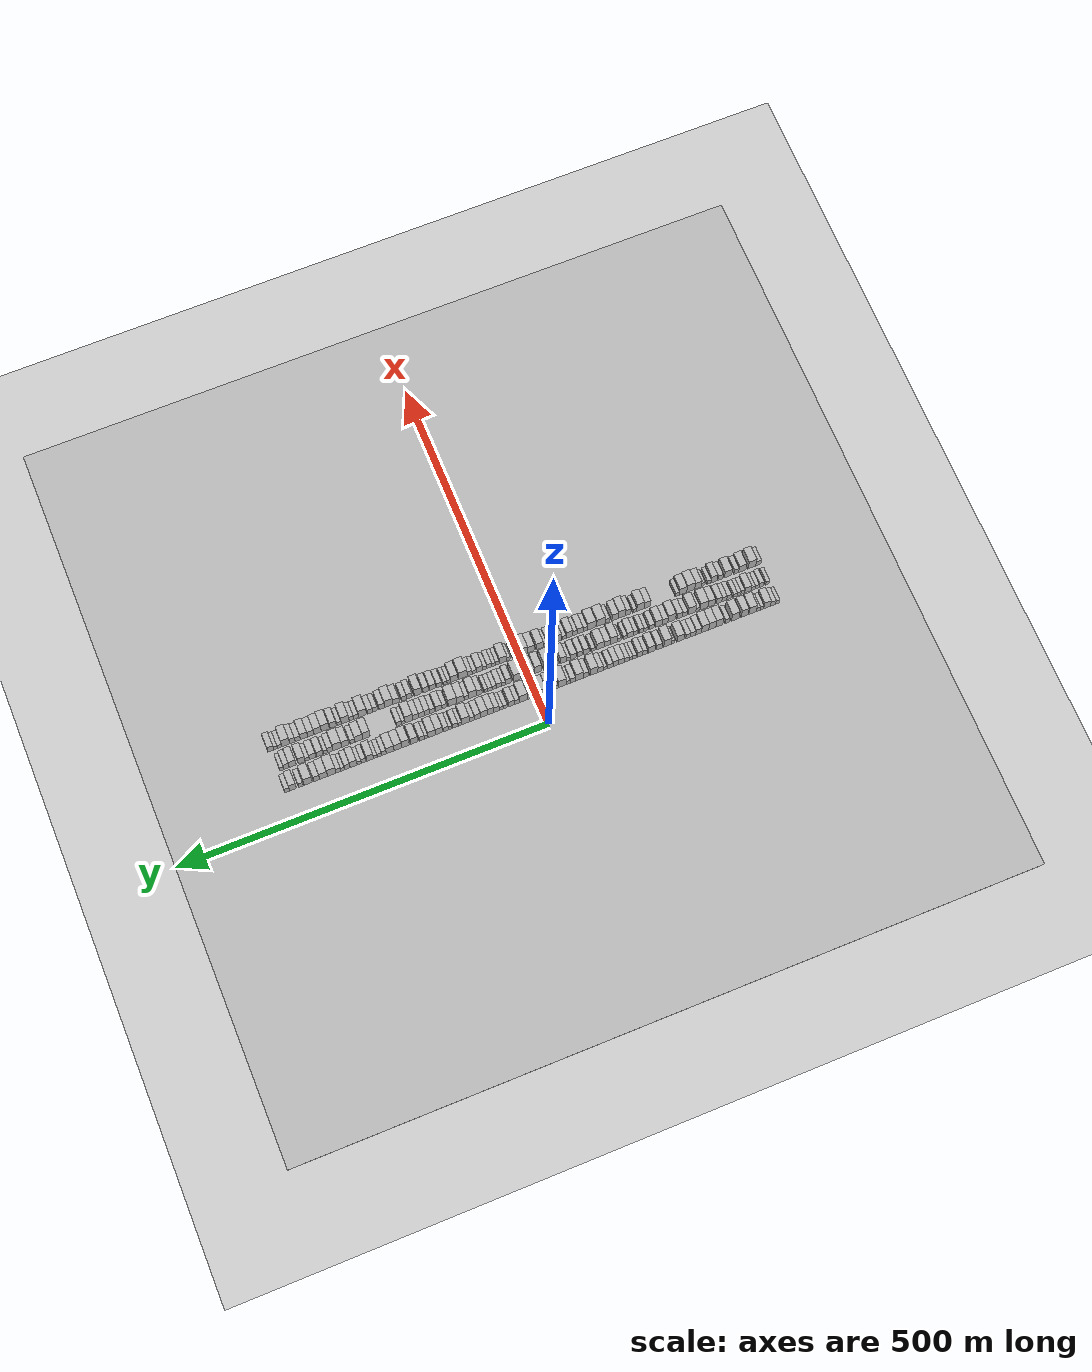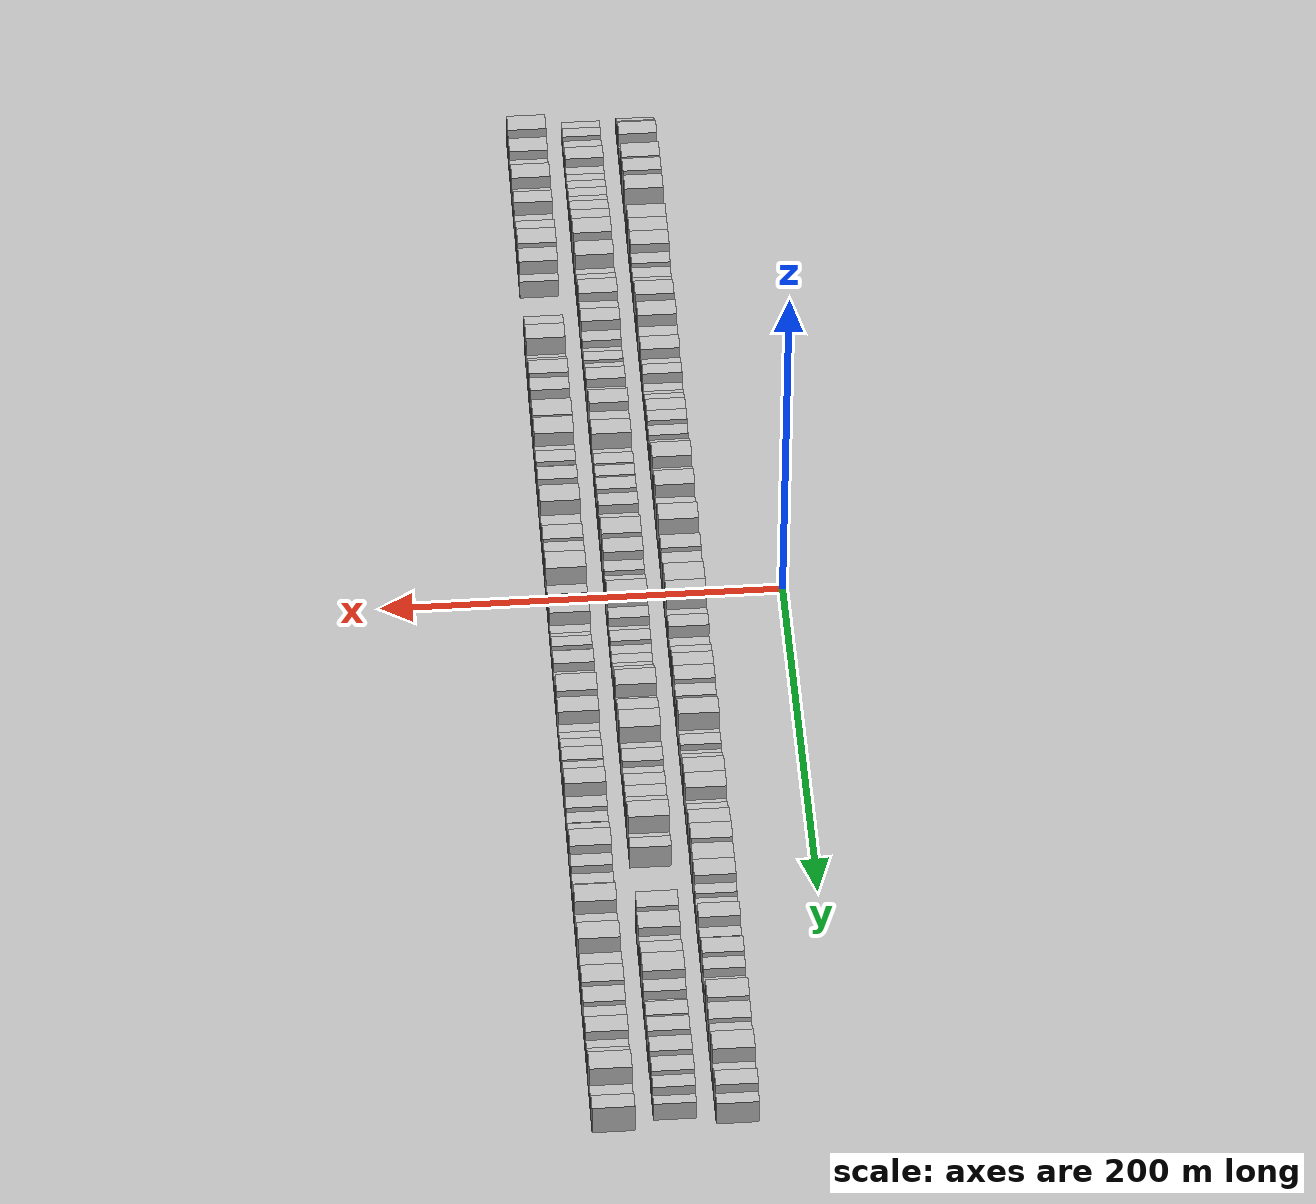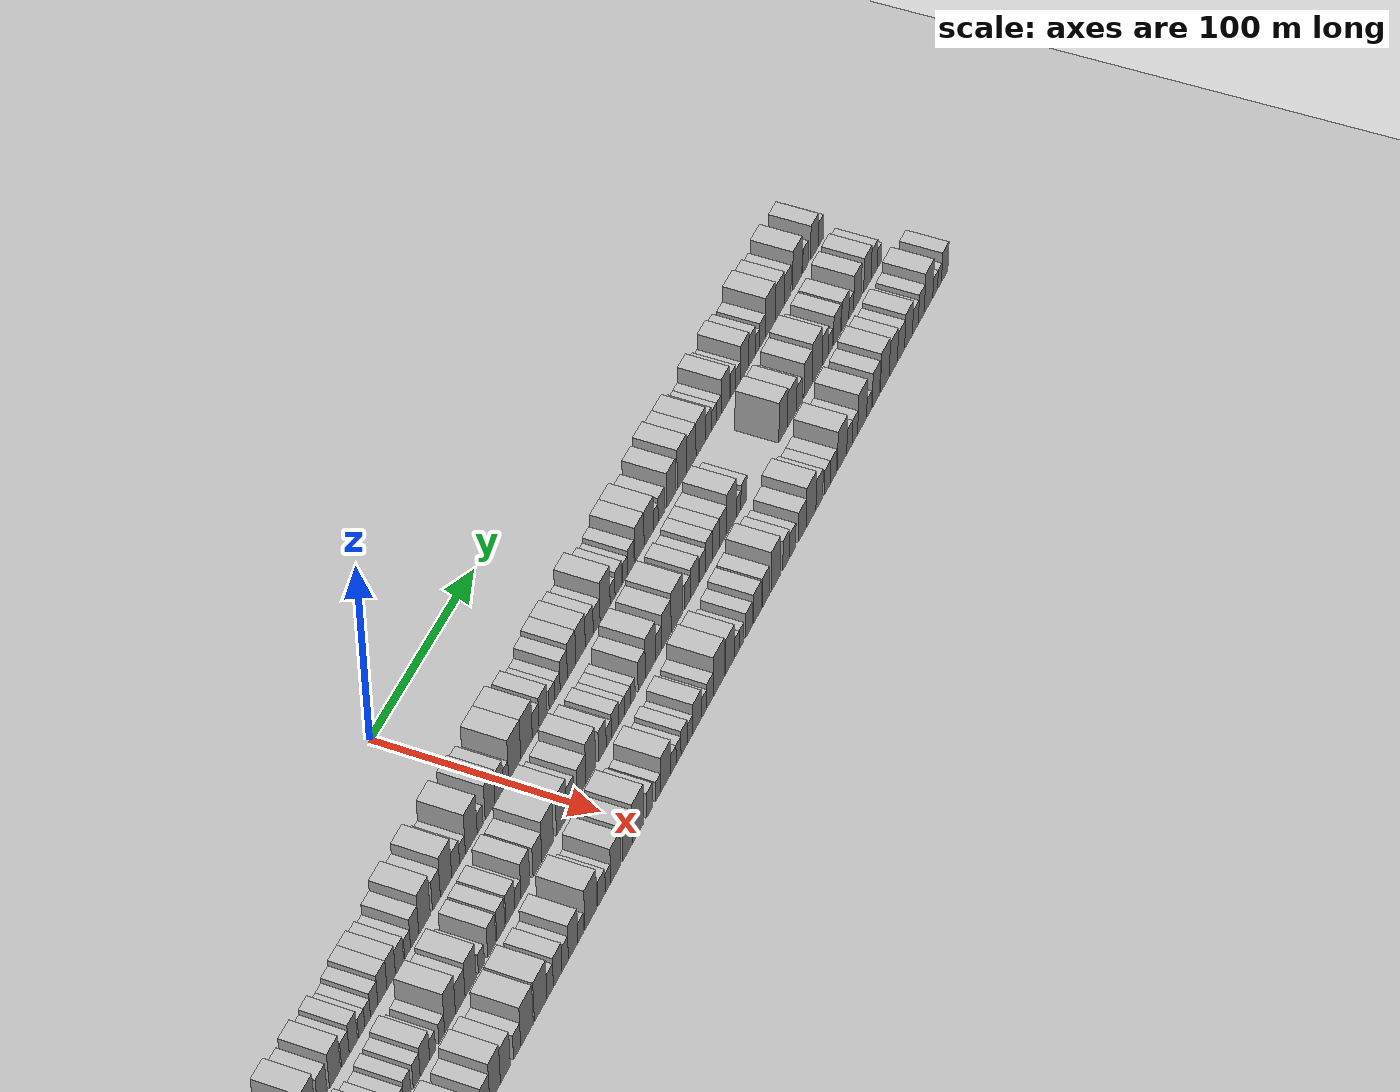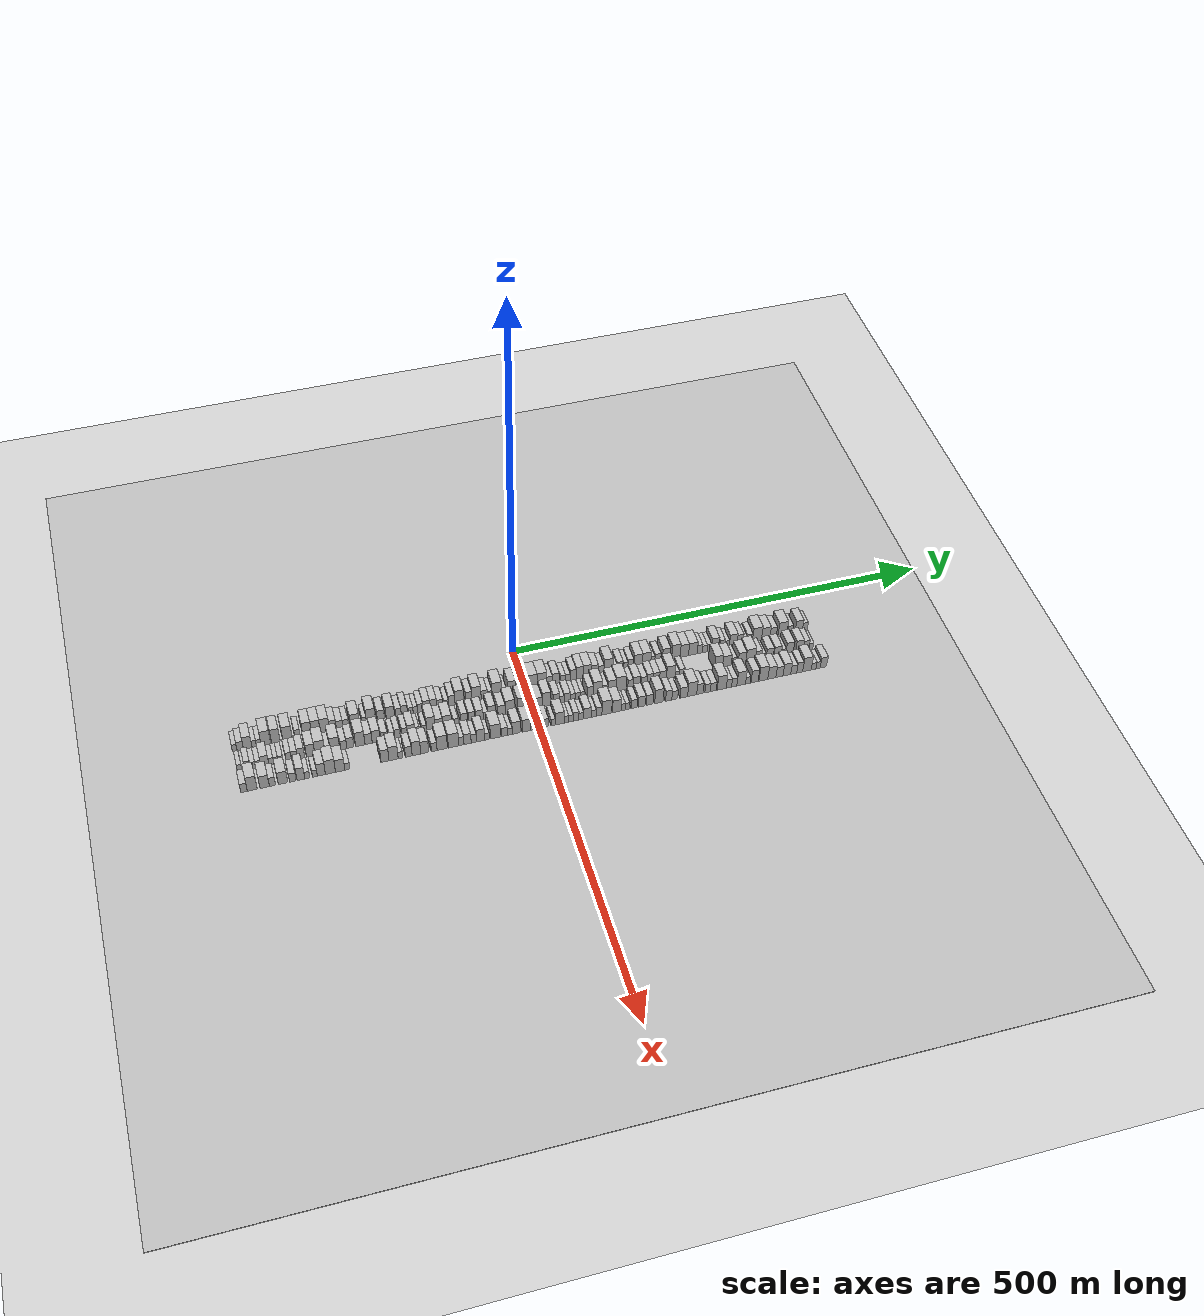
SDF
<?xml version="1.0" encoding="utf-8"?>

<sdf version="1.6">

   <world name="default">

      <gui fullscreen="0">

         <camera name="user_camera">

            <pose>-15 0 4.57585 0 0 0</pose>

            <view_controller>orbit</view_controller>

         </camera>

      </gui>

      <scene>

         <sky>

           <clouds>

             <speed>12</speed>

           </clouds>

         </sky>

         <ambient>0.4 0.4 0.4 1</ambient>

         <background>0.7 0.7 0.7 1</background>

         <shadows>1</shadows>

      </scene>

      <gravity>0 0 -9.8066</gravity>

      <magnetic_field>6e-06 2.3e-05 -4.2e-05</magnetic_field>

      <physics default="0" name="default_physics" type="ode">

         <ode>

            <solver>

               <type>quick</type>

               <iters>10</iters>

               <sor>1.0</sor>

               <use_dynamic_moi_rescaling>0</use_dynamic_moi_rescaling>

            </solver>

            <constraints>

               <cfm>0</cfm>

               <erp>0.2</erp>

               <contact_max_correcting_vel>100</contact_max_correcting_vel>

               <contact_surface_layer>0.001</contact_surface_layer>

            </constraints>

         </ode>

         <max_step_size>0.004</max_step_size>

         <real_time_factor>1</real_time_factor>

         <real_time_update_rate>250</real_time_update_rate>

      </physics>

      <light name="sun" type="directional">

         <cast_shadows>1</cast_shadows>

         <pose>0 0 10 0 0 0</pose>

         <diffuse>0.8 0.8 0.8 1</diffuse>

         <specular>0.2 0.2 0.2 1</specular>

         <attenuation>

            <range>1000</range>

            <constant>0.9</constant>

            <linear>0.01</linear>

            <quadratic>0.001</quadratic>

         </attenuation>

         <direction>-0.5 0.1 -0.9</direction>

      </light>

      <include>

         <name>ground_plane_1</name>

         <uri>model://HANNAS_ground_plane</uri>

         <pose>0 0 0  0 0 0</pose>

      </include>

      <include>

         <name>ground_plane_2</name>

         <uri>model://HANNAS_ground_plane</uri>

         <pose>100 0 0  0 0 0</pose>

      </include>

      <model name="building_1">

         <static>1</static>

         <pose frame="">50.0000 -333.4136 0 0.000000 0.000000 0.000000</pose>

         <link name="link">

            <pose frame="">0 0 6.00 0 0 0</pose>

            <collision name="collision">

               <geometry>

                  <box>

                     <size>20.0000 5.1729 12.0000</size>

                  </box>

               </geometry>

               <max_contacts>10</max_contacts>

               <surface>

                  <contact>

                     <ode/>

                  </contact>

                  <bounce/>

                  <friction>

                     <torsional>

                        <ode/>

                     </torsional>

                     <ode/>

                  </friction>

               </surface>

            </collision>

            <visual name="visual">

               <cast_shadows>0</cast_shadows>

               <geometry>

                  <box>

                     <size>20.0000 5.1729 12.0000</size>

                  </box>

               </geometry>

               <material>

                  <script>

                     <uri>model://HANNAS_wall/materials/scripts</uri>

                     <uri>model://HANNAS_wall/materials/textures</uri>

                     <name>vrc/HANNAS_wall</name>

                  </script>

               </material>

            </visual>

            <self_collide>0</self_collide>

            <enable_wind>0</enable_wind>

            <kinematic>0</kinematic>

         </link>

      </model>

      <model name="building_2">

         <static>1</static>

         <pose frame="">50.0000 -327.2435 0 0.000000 0.000000 0.000000</pose>

         <link name="link">

            <pose frame="">0 0 7.50 0 0 0</pose>

            <collision name="collision">

               <geometry>

                  <box>

                     <size>20.0000 7.1673 15.0000</size>

                  </box>

               </geometry>

               <max_contacts>10</max_contacts>

               <surface>

                  <contact>

                     <ode/>

                  </contact>

                  <bounce/>

                  <friction>

                     <torsional>

                        <ode/>

                     </torsional>

                     <ode/>

                  </friction>

               </surface>

            </collision>

            <visual name="visual">

               <cast_shadows>0</cast_shadows>

               <geometry>

                  <box>

                     <size>20.0000 7.1673 15.0000</size>

                  </box>

               </geometry>

               <material>

                  <script>

                     <uri>model://HANNAS_wall/materials/scripts</uri>

                     <uri>model://HANNAS_wall/materials/textures</uri>

                     <name>vrc/HANNAS_wall</name>

                  </script>

               </material>

            </visual>

            <self_collide>0</self_collide>

            <enable_wind>0</enable_wind>

            <kinematic>0</kinematic>

         </link>

      </model>

      <model name="building_3">

         <static>1</static>

         <pose frame="">50.0000 -318.9171 0 0.000000 0.000000 0.000000</pose>

         <link name="link">

            <pose frame="">0 0 10.50 0 0 0</pose>

            <collision name="collision">

               <geometry>

                  <box>

                     <size>20.0000 9.4854 21.0000</size>

                  </box>

               </geometry>

               <max_contacts>10</max_contacts>

               <surface>

                  <contact>

                     <ode/>

                  </contact>

                  <bounce/>

                  <friction>

                     <torsional>

                        <ode/>

                     </torsional>

                     <ode/>

                  </friction>

               </surface>

            </collision>

            <visual name="visual">

               <cast_shadows>0</cast_shadows>

               <geometry>

                  <box>

                     <size>20.0000 9.4854 21.0000</size>

                  </box>

               </geometry>

               <material>

                  <script>

                     <uri>model://HANNAS_wall/materials/scripts</uri>

                     <uri>model://HANNAS_wall/materials/textures</uri>

                     <name>vrc/HANNAS_wall</name>

                  </script>

               </material>

            </visual>

            <self_collide>0</self_collide>

            <enable_wind>0</enable_wind>

            <kinematic>0</kinematic>

         </link>

      </model>

      <model name="building_4">

         <static>1</static>

         <pose frame="">50.0000 -311.6888 0 0.000000 0.000000 0.000000</pose>

         <link name="link">

            <pose frame="">0 0 6.00 0 0 0</pose>

            <collision name="collision">

               <geometry>

                  <box>

                     <size>20.0000 4.9712 12.0000</size>

                  </box>

               </geometry>

               <max_contacts>10</max_contacts>

               <surface>

                  <contact>

                     <ode/>

                  </contact>

                  <bounce/>

                  <friction>

                     <torsional>

                        <ode/>

                     </torsional>

                     <ode/>

                  </friction>

               </surface>

            </collision>

            <visual name="visual">

               <cast_shadows>0</cast_shadows>

               <geometry>

                  <box>

                     <size>20.0000 4.9712 12.0000</size>

                  </box>

               </geometry>

               <material>

                  <script>

                     <uri>model://HANNAS_wall/materials/scripts</uri>

                     <uri>model://HANNAS_wall/materials/textures</uri>

                     <name>vrc/HANNAS_wall</name>

                  </script>

               </material>

            </visual>

            <self_collide>0</self_collide>

            <enable_wind>0</enable_wind>

            <kinematic>0</kinematic>

         </link>

      </model>

      <model name="building_5">

         <static>1</static>

         <pose frame="">50.0000 -306.6014 0 0.000000 0.000000 0.000000</pose>

         <link name="link">

            <pose frame="">0 0 6.00 0 0 0</pose>

            <collision name="collision">

               <geometry>

                  <box>

                     <size>20.0000 5.2036 12.0000</size>

                  </box>

               </geometry>

               <max_contacts>10</max_contacts>

               <surface>

                  <contact>

                     <ode/>

                  </contact>

                  <bounce/>

                  <friction>

                     <torsional>

                        <ode/>

                     </torsional>

                     <ode/>

                  </friction>

               </surface>

            </collision>

            <visual name="visual">

               <cast_shadows>0</cast_shadows>

               <geometry>

                  <box>

                     <size>20.0000 5.2036 12.0000</size>

                  </box>

               </geometry>

               <material>

                  <script>

                     <uri>model://HANNAS_wall/materials/scripts</uri>

                     <uri>model://HANNAS_wall/materials/textures</uri>

                     <name>vrc/HANNAS_wall</name>

                  </script>

               </material>

            </visual>

            <self_collide>0</self_collide>

            <enable_wind>0</enable_wind>

            <kinematic>0</kinematic>

         </link>

      </model>

      <model name="building_6">

         <static>1</static>

         <pose frame="">50.0000 -298.6888 0 0.000000 0.000000 0.000000</pose>

         <link name="link">

            <pose frame="">0 0 12.00 0 0 0</pose>

            <collision name="collision">

               <geometry>

                  <box>

                     <size>20.0000 10.6217 24.0000</size>

                  </box>

               </geometry>

               <max_contacts>10</max_contacts>

               <surface>

                  <contact>

                     <ode/>

                  </contact>

                  <bounce/>

                  <friction>

                     <torsional>

                        <ode/>

                     </torsional>

                     <ode/>

                  </friction>

               </surface>

            </collision>

            <visual name="visual">

               <cast_shadows>0</cast_shadows>

               <geometry>

                  <box>

                     <size>20.0000 10.6217 24.0000</size>

                  </box>

               </geometry>

               <material>

                  <script>

                     <uri>model://HANNAS_wall/materials/scripts</uri>

                     <uri>model://HANNAS_wall/materials/textures</uri>

                     <name>vrc/HANNAS_wall</name>

                  </script>

               </material>

            </visual>

            <self_collide>0</self_collide>

            <enable_wind>0</enable_wind>

            <kinematic>0</kinematic>

         </link>

      </model>

      <model name="building_7">

         <static>1</static>

         <pose frame="">50.0000 -287.5518 0 0.000000 0.000000 0.000000</pose>

         <link name="link">

            <pose frame="">0 0 12.00 0 0 0</pose>

            <collision name="collision">

               <geometry>

                  <box>

                     <size>20.0000 9.6523 24.0000</size>

                  </box>

               </geometry>

               <max_contacts>10</max_contacts>

               <surface>

                  <contact>

                     <ode/>

                  </contact>

                  <bounce/>

                  <friction>

                     <torsional>

                        <ode/>

                     </torsional>

                     <ode/>

                  </friction>

               </surface>

            </collision>

            <visual name="visual">

               <cast_shadows>0</cast_shadows>

               <geometry>

                  <box>

                     <size>20.0000 9.6523 24.0000</size>

                  </box>

               </geometry>

               <material>

                  <script>

                     <uri>model://HANNAS_wall/materials/scripts</uri>

                     <uri>model://HANNAS_wall/materials/textures</uri>

                     <name>vrc/HANNAS_wall</name>

                  </script>

               </material>

            </visual>

            <self_collide>0</self_collide>

            <enable_wind>0</enable_wind>

            <kinematic>0</kinematic>

         </link>

      </model>

      <model name="building_8">

         <static>1</static>

         <pose frame="">50.0000 -274.4158 0 0.000000 0.000000 0.000000</pose>

         <link name="link">

            <pose frame="">0 0 12.00 0 0 0</pose>

            <collision name="collision">

               <geometry>

                  <box>

                     <size>20.0000 10.6198 24.0000</size>

                  </box>

               </geometry>

               <max_contacts>10</max_contacts>

               <surface>

                  <contact>

                     <ode/>

                  </contact>

                  <bounce/>

                  <friction>

                     <torsional>

                        <ode/>

                     </torsional>

                     <ode/>

                  </friction>

               </surface>

            </collision>

            <visual name="visual">

               <cast_shadows>0</cast_shadows>

               <geometry>

                  <box>

                     <size>20.0000 10.6198 24.0000</size>

                  </box>

               </geometry>

               <material>

                  <script>

                     <uri>model://HANNAS_wall/materials/scripts</uri>

                     <uri>model://HANNAS_wall/materials/textures</uri>

                     <name>vrc/HANNAS_wall</name>

                  </script>

               </material>

            </visual>

            <self_collide>0</self_collide>

            <enable_wind>0</enable_wind>

            <kinematic>0</kinematic>

         </link>

      </model>

      <model name="building_9">

         <static>1</static>

         <pose frame="">50.0000 -263.1055 0 0.000000 0.000000 0.000000</pose>

         <link name="link">

            <pose frame="">0 0 7.50 0 0 0</pose>

            <collision name="collision">

               <geometry>

                  <box>

                     <size>20.0000 6.0008 15.0000</size>

                  </box>

               </geometry>

               <max_contacts>10</max_contacts>

               <surface>

                  <contact>

                     <ode/>

                  </contact>

                  <bounce/>

                  <friction>

                     <torsional>

                        <ode/>

                     </torsional>

                     <ode/>

                  </friction>

               </surface>

            </collision>

            <visual name="visual">

               <cast_shadows>0</cast_shadows>

               <geometry>

                  <box>

                     <size>20.0000 6.0008 15.0000</size>

                  </box>

               </geometry>

               <material>

                  <script>

                     <uri>model://HANNAS_wall/materials/scripts</uri>

                     <uri>model://HANNAS_wall/materials/textures</uri>

                     <name>vrc/HANNAS_wall</name>

                  </script>

               </material>

            </visual>

            <self_collide>0</self_collide>

            <enable_wind>0</enable_wind>

            <kinematic>0</kinematic>

         </link>

      </model>

      <model name="building_10">

         <static>1</static>

         <pose frame="">50.0000 -252.2052 0 0.000000 0.000000 0.000000</pose>

         <link name="link">

            <pose frame="">0 0 12.00 0 0 0</pose>

            <collision name="collision">

               <geometry>

                  <box>

                     <size>20.0000 9.7998 24.0000</size>

                  </box>

               </geometry>

               <max_contacts>10</max_contacts>

               <surface>

                  <contact>

                     <ode/>

                  </contact>

                  <bounce/>

                  <friction>

                     <torsional>

                        <ode/>

                     </torsional>

                     <ode/>

                  </friction>

               </surface>

            </collision>

            <visual name="visual">

               <cast_shadows>0</cast_shadows>

               <geometry>

                  <box>

                     <size>20.0000 9.7998 24.0000</size>

                  </box>

               </geometry>

               <material>

                  <script>

                     <uri>model://HANNAS_wall/materials/scripts</uri>

                     <uri>model://HANNAS_wall/materials/textures</uri>

                     <name>vrc/HANNAS_wall</name>

                  </script>

               </material>

            </visual>

            <self_collide>0</self_collide>

            <enable_wind>0</enable_wind>

            <kinematic>0</kinematic>

         </link>

      </model>

      <model name="building_11">

         <static>1</static>

         <pose frame="">50.0000 -242.3475 0 0.000000 0.000000 0.000000</pose>

         <link name="link">

            <pose frame="">0 0 12.00 0 0 0</pose>

            <collision name="collision">

               <geometry>

                  <box>

                     <size>20.0000 9.9154 24.0000</size>

                  </box>

               </geometry>

               <max_contacts>10</max_contacts>

               <surface>

                  <contact>

                     <ode/>

                  </contact>

                  <bounce/>

                  <friction>

                     <torsional>

                        <ode/>

                     </torsional>

                     <ode/>

                  </friction>

               </surface>

            </collision>

            <visual name="visual">

               <cast_shadows>0</cast_shadows>

               <geometry>

                  <box>

                     <size>20.0000 9.9154 24.0000</size>

                  </box>

               </geometry>

               <material>

                  <script>

                     <uri>model://HANNAS_wall/materials/scripts</uri>

                     <uri>model://HANNAS_wall/materials/textures</uri>

                     <name>vrc/HANNAS_wall</name>

                  </script>

               </material>

            </visual>

            <self_collide>0</self_collide>

            <enable_wind>0</enable_wind>

            <kinematic>0</kinematic>

         </link>

      </model>

      <model name="building_12">

         <static>1</static>

         <pose frame="">50.0000 -232.2173 0 0.000000 0.000000 0.000000</pose>

         <link name="link">

            <pose frame="">0 0 12.00 0 0 0</pose>

            <collision name="collision">

               <geometry>

                  <box>

                     <size>20.0000 10.3451 24.0000</size>

                  </box>

               </geometry>

               <max_contacts>10</max_contacts>

               <surface>

                  <contact>

                     <ode/>

                  </contact>

                  <bounce/>

                  <friction>

                     <torsional>

                        <ode/>

                     </torsional>

                     <ode/>

                  </friction>

               </surface>

            </collision>

            <visual name="visual">

               <cast_shadows>0</cast_shadows>

               <geometry>

                  <box>

                     <size>20.0000 10.3451 24.0000</size>

                  </box>

               </geometry>

               <material>

                  <script>

                     <uri>model://HANNAS_wall/materials/scripts</uri>

                     <uri>model://HANNAS_wall/materials/textures</uri>

                     <name>vrc/HANNAS_wall</name>

                  </script>

               </material>

            </visual>

            <self_collide>0</self_collide>

            <enable_wind>0</enable_wind>

            <kinematic>0</kinematic>

         </link>

      </model>

      <model name="building_13">

         <static>1</static>

         <pose frame="">50.0000 -223.1650 0 0.000000 0.000000 0.000000</pose>

         <link name="link">

            <pose frame="">0 0 9.00 0 0 0</pose>

            <collision name="collision">

               <geometry>

                  <box>

                     <size>20.0000 7.7595 18.0000</size>

                  </box>

               </geometry>

               <max_contacts>10</max_contacts>

               <surface>

                  <contact>

                     <ode/>

                  </contact>

                  <bounce/>

                  <friction>

                     <torsional>

                        <ode/>

                     </torsional>

                     <ode/>

                  </friction>

               </surface>

            </collision>

            <visual name="visual">

               <cast_shadows>0</cast_shadows>

               <geometry>

                  <box>

                     <size>20.0000 7.7595 18.0000</size>

                  </box>

               </geometry>

               <material>

                  <script>

                     <uri>model://HANNAS_wall/materials/scripts</uri>

                     <uri>model://HANNAS_wall/materials/textures</uri>

                     <name>vrc/HANNAS_wall</name>

                  </script>

               </material>

            </visual>

            <self_collide>0</self_collide>

            <enable_wind>0</enable_wind>

            <kinematic>0</kinematic>

         </link>

      </model>

      <model name="building_14">

         <static>1</static>

         <pose frame="">50.0000 -215.5926 0 0.000000 0.000000 0.000000</pose>

         <link name="link">

            <pose frame="">0 0 7.50 0 0 0</pose>

            <collision name="collision">

               <geometry>

                  <box>

                     <size>20.0000 7.3854 15.0000</size>

                  </box>

               </geometry>

               <max_contacts>10</max_contacts>

               <surface>

                  <contact>

                     <ode/>

                  </contact>

                  <bounce/>

                  <friction>

                     <torsional>

                        <ode/>

                     </torsional>

                     <ode/>

                  </friction>

               </surface>

            </collision>

            <visual name="visual">

               <cast_shadows>0</cast_shadows>

               <geometry>

                  <box>

                     <size>20.0000 7.3854 15.0000</size>

                  </box>

               </geometry>

               <material>

                  <script>

                     <uri>model://HANNAS_wall/materials/scripts</uri>

                     <uri>model://HANNAS_wall/materials/textures</uri>

                     <name>vrc/HANNAS_wall</name>

                  </script>

               </material>

            </visual>

            <self_collide>0</self_collide>

            <enable_wind>0</enable_wind>

            <kinematic>0</kinematic>

         </link>

      </model>

      <model name="building_15">

         <static>1</static>

         <pose frame="">50.0000 -208.5987 0 0.000000 0.000000 0.000000</pose>

         <link name="link">

            <pose frame="">0 0 7.50 0 0 0</pose>

            <collision name="collision">

               <geometry>

                  <box>

                     <size>20.0000 6.6022 15.0000</size>

                  </box>

               </geometry>

               <max_contacts>10</max_contacts>

               <surface>

                  <contact>

                     <ode/>

                  </contact>

                  <bounce/>

                  <friction>

                     <torsional>

                        <ode/>

                     </torsional>

                     <ode/>

                  </friction>

               </surface>

            </collision>

            <visual name="visual">

               <cast_shadows>0</cast_shadows>

               <geometry>

                  <box>

                     <size>20.0000 6.6022 15.0000</size>

                  </box>

               </geometry>

               <material>

                  <script>

                     <uri>model://HANNAS_wall/materials/scripts</uri>

                     <uri>model://HANNAS_wall/materials/textures</uri>

                     <name>vrc/HANNAS_wall</name>

                  </script>

               </material>

            </visual>

            <self_collide>0</self_collide>

            <enable_wind>0</enable_wind>

            <kinematic>0</kinematic>

         </link>

      </model>

      <model name="building_16">

         <static>1</static>

         <pose frame="">50.0000 -198.1302 0 0.000000 0.000000 0.000000</pose>

         <link name="link">

            <pose frame="">0 0 10.50 0 0 0</pose>

            <collision name="collision">

               <geometry>

                  <box>

                     <size>20.0000 10.3349 21.0000</size>

                  </box>

               </geometry>

               <max_contacts>10</max_contacts>

               <surface>

                  <contact>

                     <ode/>

                  </contact>

                  <bounce/>

                  <friction>

                     <torsional>

                        <ode/>

                     </torsional>

                     <ode/>

                  </friction>

               </surface>

            </collision>

            <visual name="visual">

               <cast_shadows>0</cast_shadows>

               <geometry>

                  <box>

                     <size>20.0000 10.3349 21.0000</size>

                  </box>

               </geometry>

               <material>

                  <script>

                     <uri>model://HANNAS_wall/materials/scripts</uri>

                     <uri>model://HANNAS_wall/materials/textures</uri>

                     <name>vrc/HANNAS_wall</name>

                  </script>

               </material>

            </visual>

            <self_collide>0</self_collide>

            <enable_wind>0</enable_wind>

            <kinematic>0</kinematic>

         </link>

      </model>

      <model name="building_17">

         <static>1</static>

         <pose frame="">50.0000 -187.5528 0 0.000000 0.000000 0.000000</pose>

         <link name="link">

            <pose frame="">0 0 6.00 0 0 0</pose>

            <collision name="collision">

               <geometry>

                  <box>

                     <size>20.0000 4.8197 12.0000</size>

                  </box>

               </geometry>

               <max_contacts>10</max_contacts>

               <surface>

                  <contact>

                     <ode/>

                  </contact>

                  <bounce/>

                  <friction>

                     <torsional>

                        <ode/>

                     </torsional>

                     <ode/>

                  </friction>

               </surface>

            </collision>

            <visual name="visual">

               <cast_shadows>0</cast_shadows>

               <geometry>

                  <box>

                     <size>20.0000 4.8197 12.0000</size>

                  </box>

               </geometry>

               <material>

                  <script>

                     <uri>model://HANNAS_wall/materials/scripts</uri>

                     <uri>model://HANNAS_wall/materials/textures</uri>

                     <name>vrc/HANNAS_wall</name>

                  </script>

               </material>

            </visual>

            <self_collide>0</self_collide>

            <enable_wind>0</enable_wind>

            <kinematic>0</kinematic>

         </link>

      </model>

      <model name="building_18">

         <static>1</static>

         <pose frame="">50.0000 -179.8980 0 0.000000 0.000000 0.000000</pose>

         <link name="link">

            <pose frame="">0 0 12.00 0 0 0</pose>

            <collision name="collision">

               <geometry>

                  <box>

                     <size>20.0000 10.4900 24.0000</size>

                  </box>

               </geometry>

               <max_contacts>10</max_contacts>

               <surface>

                  <contact>

                     <ode/>

                  </contact>

                  <bounce/>

                  <friction>

                     <torsional>

                        <ode/>

                     </torsional>

                     <ode/>

                  </friction>

               </surface>

            </collision>

            <visual name="visual">

               <cast_shadows>0</cast_shadows>

               <geometry>

                  <box>

                     <size>20.0000 10.4900 24.0000</size>

                  </box>

               </geometry>

               <material>

                  <script>

                     <uri>model://HANNAS_wall/materials/scripts</uri>

                     <uri>model://HANNAS_wall/materials/textures</uri>

                     <name>vrc/HANNAS_wall</name>

                  </script>

               </material>

            </visual>

            <self_collide>0</self_collide>

            <enable_wind>0</enable_wind>

            <kinematic>0</kinematic>

         </link>

      </model>

      <model name="building_19">

         <static>1</static>

         <pose frame="">50.0000 -168.5905 0 0.000000 0.000000 0.000000</pose>

         <link name="link">

            <pose frame="">0 0 9.00 0 0 0</pose>

            <collision name="collision">

               <geometry>

                  <box>

                     <size>20.0000 8.1248 18.0000</size>

                  </box>

               </geometry>

               <max_contacts>10</max_contacts>

               <surface>

                  <contact>

                     <ode/>

                  </contact>

                  <bounce/>

                  <friction>

                     <torsional>

                        <ode/>

                     </torsional>

                     <ode/>

                  </friction>

               </surface>

            </collision>

            <visual name="visual">

               <cast_shadows>0</cast_shadows>

               <geometry>

                  <box>

                     <size>20.0000 8.1248 18.0000</size>

                  </box>

               </geometry>

               <material>

                  <script>

                     <uri>model://HANNAS_wall/materials/scripts</uri>

                     <uri>model://HANNAS_wall/materials/textures</uri>

                     <name>vrc/HANNAS_wall</name>

                  </script>

               </material>

            </visual>

            <self_collide>0</self_collide>

            <enable_wind>0</enable_wind>

            <kinematic>0</kinematic>

         </link>

      </model>

      <model name="building_20">

         <static>1</static>

         <pose frame="">50.0000 -157.7509 0 0.000000 0.000000 0.000000</pose>

         <link name="link">

            <pose frame="">0 0 10.50 0 0 0</pose>

            <collision name="collision">

               <geometry>

                  <box>

                     <size>20.0000 9.5544 21.0000</size>

                  </box>

               </geometry>

               <max_contacts>10</max_contacts>

               <surface>

                  <contact>

                     <ode/>

                  </contact>

                  <bounce/>

                  <friction>

                     <torsional>

                        <ode/>

                     </torsional>

                     <ode/>

                  </friction>

               </surface>

            </collision>

            <visual name="visual">

               <cast_shadows>0</cast_shadows>

               <geometry>

                  <box>

                     <size>20.0000 9.5544 21.0000</size>

                  </box>

               </geometry>

               <material>

                  <script>

                     <uri>model://HANNAS_wall/materials/scripts</uri>

                     <uri>model://HANNAS_wall/materials/textures</uri>

                     <name>vrc/HANNAS_wall</name>

                  </script>

               </material>

            </visual>

            <self_collide>0</self_collide>

            <enable_wind>0</enable_wind>

            <kinematic>0</kinematic>

         </link>

      </model>

      <model name="building_21">

         <static>1</static>

         <pose frame="">50.0000 -148.6712 0 0.000000 0.000000 0.000000</pose>

         <link name="link">

            <pose frame="">0 0 7.50 0 0 0</pose>

            <collision name="collision">

               <geometry>

                  <box>

                     <size>20.0000 6.6050 15.0000</size>

                  </box>

               </geometry>

               <max_contacts>10</max_contacts>

               <surface>

                  <contact>

                     <ode/>

                  </contact>

                  <bounce/>

                  <friction>

                     <torsional>

                        <ode/>

                     </torsional>

                     <ode/>

                  </friction>

               </surface>

            </collision>

            <visual name="visual">

               <cast_shadows>0</cast_shadows>

               <geometry>

                  <box>

                     <size>20.0000 6.6050 15.0000</size>

                  </box>

               </geometry>

               <material>

                  <script>

                     <uri>model://HANNAS_wall/materials/scripts</uri>

                     <uri>model://HANNAS_wall/materials/textures</uri>

                     <name>vrc/HANNAS_wall</name>

                  </script>

               </material>

            </visual>

            <self_collide>0</self_collide>

            <enable_wind>0</enable_wind>

            <kinematic>0</kinematic>

         </link>

      </model>

      <model name="building_22">

         <static>1</static>

         <pose frame="">50.0000 -141.7651 0 0.000000 0.000000 0.000000</pose>

         <link name="link">

            <pose frame="">0 0 9.00 0 0 0</pose>

            <collision name="collision">

               <geometry>

                  <box>

                     <size>20.0000 7.2073 18.0000</size>

                  </box>

               </geometry>

               <max_contacts>10</max_contacts>

               <surface>

                  <contact>

                     <ode/>

                  </contact>

                  <bounce/>

                  <friction>

                     <torsional>

                        <ode/>

                     </torsional>

                     <ode/>

                  </friction>

               </surface>

            </collision>

            <visual name="visual">

               <cast_shadows>0</cast_shadows>

               <geometry>

                  <box>

                     <size>20.0000 7.2073 18.0000</size>

                  </box>

               </geometry>

               <material>

                  <script>

                     <uri>model://HANNAS_wall/materials/scripts</uri>

                     <uri>model://HANNAS_wall/materials/textures</uri>

                     <name>vrc/HANNAS_wall</name>

                  </script>

               </material>

            </visual>

            <self_collide>0</self_collide>

            <enable_wind>0</enable_wind>

            <kinematic>0</kinematic>

         </link>

      </model>

      <model name="building_23">

         <static>1</static>

         <pose frame="">50.0000 -134.4319 0 0.000000 0.000000 0.000000</pose>

         <link name="link">

            <pose frame="">0 0 6.00 0 0 0</pose>

            <collision name="collision">

               <geometry>

                  <box>

                     <size>20.0000 5.4589 12.0000</size>

                  </box>

               </geometry>

               <max_contacts>10</max_contacts>

               <surface>

                  <contact>

                     <ode/>

                  </contact>

                  <bounce/>

                  <friction>

                     <torsional>

                        <ode/>

                     </torsional>

                     <ode/>

                  </friction>

               </surface>

            </collision>

            <visual name="visual">

               <cast_shadows>0</cast_shadows>

               <geometry>

                  <box>

                     <size>20.0000 5.4589 12.0000</size>

                  </box>

               </geometry>

               <material>

                  <script>

                     <uri>model://HANNAS_wall/materials/scripts</uri>

                     <uri>model://HANNAS_wall/materials/textures</uri>

                     <name>vrc/HANNAS_wall</name>

                  </script>

               </material>

            </visual>

            <self_collide>0</self_collide>

            <enable_wind>0</enable_wind>

            <kinematic>0</kinematic>

         </link>

      </model>

      <model name="building_24">

         <static>1</static>

         <pose frame="">50.0000 -129.1912 0 0.000000 0.000000 0.000000</pose>

         <link name="link">

            <pose frame="">0 0 6.00 0 0 0</pose>

            <collision name="collision">

               <geometry>

                  <box>

                     <size>20.0000 5.0226 12.0000</size>

                  </box>

               </geometry>

               <max_contacts>10</max_contacts>

               <surface>

                  <contact>

                     <ode/>

                  </contact>

                  <bounce/>

                  <friction>

                     <torsional>

                        <ode/>

                     </torsional>

                     <ode/>

                  </friction>

               </surface>

            </collision>

            <visual name="visual">

               <cast_shadows>0</cast_shadows>

               <geometry>

                  <box>

                     <size>20.0000 5.0226 12.0000</size>

                  </box>

               </geometry>

               <material>

                  <script>

                     <uri>model://HANNAS_wall/materials/scripts</uri>

                     <uri>model://HANNAS_wall/materials/textures</uri>

                     <name>vrc/HANNAS_wall</name>

                  </script>

               </material>

            </visual>

            <self_collide>0</self_collide>

            <enable_wind>0</enable_wind>

            <kinematic>0</kinematic>

         </link>

      </model>

      <model name="building_25">

         <static>1</static>

         <pose frame="">50.0000 -123.4154 0 0.000000 0.000000 0.000000</pose>

         <link name="link">

            <pose frame="">0 0 7.50 0 0 0</pose>

            <collision name="collision">

               <geometry>

                  <box>

                     <size>20.0000 6.5289 15.0000</size>

                  </box>

               </geometry>

               <max_contacts>10</max_contacts>

               <surface>

                  <contact>

                     <ode/>

                  </contact>

                  <bounce/>

                  <friction>

                     <torsional>

                        <ode/>

                     </torsional>

                     <ode/>

                  </friction>

               </surface>

            </collision>

            <visual name="visual">

               <cast_shadows>0</cast_shadows>

               <geometry>

                  <box>

                     <size>20.0000 6.5289 15.0000</size>

                  </box>

               </geometry>

               <material>

                  <script>

                     <uri>model://HANNAS_wall/materials/scripts</uri>

                     <uri>model://HANNAS_wall/materials/textures</uri>

                     <name>vrc/HANNAS_wall</name>

                  </script>

               </material>

            </visual>

            <self_collide>0</self_collide>

            <enable_wind>0</enable_wind>

            <kinematic>0</kinematic>

         </link>

      </model>

      <model name="building_26">

         <static>1</static>

         <pose frame="">50.0000 -116.1085 0 0.000000 0.000000 0.000000</pose>

         <link name="link">

            <pose frame="">0 0 9.00 0 0 0</pose>

            <collision name="collision">

               <geometry>

                  <box>

                     <size>20.0000 8.0849 18.0000</size>

                  </box>

               </geometry>

               <max_contacts>10</max_contacts>

               <surface>

                  <contact>

                     <ode/>

                  </contact>

                  <bounce/>

                  <friction>

                     <torsional>

                        <ode/>

                     </torsional>

                     <ode/>

                  </friction>

               </surface>

            </collision>

            <visual name="visual">

               <cast_shadows>0</cast_shadows>

               <geometry>

                  <box>

                     <size>20.0000 8.0849 18.0000</size>

                  </box>

               </geometry>

               <material>

                  <script>

                     <uri>model://HANNAS_wall/materials/scripts</uri>

                     <uri>model://HANNAS_wall/materials/textures</uri>

                     <name>vrc/HANNAS_wall</name>

                  </script>

               </material>

            </visual>

            <self_collide>0</self_collide>

            <enable_wind>0</enable_wind>

            <kinematic>0</kinematic>

         </link>

      </model>

      <model name="building_27">

         <static>1</static>

         <pose frame="">50.0000 -108.2516 0 0.000000 0.000000 0.000000</pose>

         <link name="link">

            <pose frame="">0 0 9.00 0 0 0</pose>

            <collision name="collision">

               <geometry>

                  <box>

                     <size>20.0000 7.6288 18.0000</size>

                  </box>

               </geometry>

               <max_contacts>10</max_contacts>

               <surface>

                  <contact>

                     <ode/>

                  </contact>

                  <bounce/>

                  <friction>

                     <torsional>

                        <ode/>

                     </torsional>

                     <ode/>

                  </friction>

               </surface>

            </collision>

            <visual name="visual">

               <cast_shadows>0</cast_shadows>

               <geometry>

                  <box>

                     <size>20.0000 7.6288 18.0000</size>

                  </box>

               </geometry>

               <material>

                  <script>

                     <uri>model://HANNAS_wall/materials/scripts</uri>

                     <uri>model://HANNAS_wall/materials/textures</uri>

                     <name>vrc/HANNAS_wall</name>

                  </script>

               </material>

            </visual>

            <self_collide>0</self_collide>

            <enable_wind>0</enable_wind>

            <kinematic>0</kinematic>

         </link>

      </model>

      <model name="building_28">

         <static>1</static>

         <pose frame="">50.0000 -100.7759 0 0.000000 0.000000 0.000000</pose>

         <link name="link">

            <pose frame="">0 0 7.50 0 0 0</pose>

            <collision name="collision">

               <geometry>

                  <box>

                     <size>20.0000 7.3226 15.0000</size>

                  </box>

               </geometry>

               <max_contacts>10</max_contacts>

               <surface>

                  <contact>

                     <ode/>

                  </contact>

                  <bounce/>

                  <friction>

                     <torsional>

                        <ode/>

                     </torsional>

                     <ode/>

                  </friction>

               </surface>

            </collision>

            <visual name="visual">

               <cast_shadows>0</cast_shadows>

               <geometry>

                  <box>

                     <size>20.0000 7.3226 15.0000</size>

                  </box>

               </geometry>

               <material>

                  <script>

                     <uri>model://HANNAS_wall/materials/scripts</uri>

                     <uri>model://HANNAS_wall/materials/textures</uri>

                     <name>vrc/HANNAS_wall</name>

                  </script>

               </material>

            </visual>

            <self_collide>0</self_collide>

            <enable_wind>0</enable_wind>

            <kinematic>0</kinematic>

         </link>

      </model>

      <model name="building_29">

         <static>1</static>

         <pose frame="">50.0000 -93.4547 0 0.000000 0.000000 0.000000</pose>

         <link name="link">

            <pose frame="">0 0 6.00 0 0 0</pose>

            <collision name="collision">

               <geometry>

                  <box>

                     <size>20.0000 5.3197 12.0000</size>

                  </box>

               </geometry>

               <max_contacts>10</max_contacts>

               <surface>

                  <contact>

                     <ode/>

                  </contact>

                  <bounce/>

                  <friction>

                     <torsional>

                        <ode/>

                     </torsional>

                     <ode/>

                  </friction>

               </surface>

            </collision>

            <visual name="visual">

               <cast_shadows>0</cast_shadows>

               <geometry>

                  <box>

                     <size>20.0000 5.3197 12.0000</size>

                  </box>

               </geometry>

               <material>

                  <script>

                     <uri>model://HANNAS_wall/materials/scripts</uri>

                     <uri>model://HANNAS_wall/materials/textures</uri>

                     <name>vrc/HANNAS_wall</name>

                  </script>

               </material>

            </visual>

            <self_collide>0</self_collide>

            <enable_wind>0</enable_wind>

            <kinematic>0</kinematic>

         </link>

      </model>

      <model name="building_30">

         <static>1</static>

         <pose frame="">50.0000 -87.0762 0 0.000000 0.000000 0.000000</pose>

         <link name="link">

            <pose frame="">0 0 9.00 0 0 0</pose>

            <collision name="collision">

               <geometry>

                  <box>

                     <size>20.0000 7.4373 18.0000</size>

                  </box>

               </geometry>

               <max_contacts>10</max_contacts>

               <surface>

                  <contact>

                     <ode/>

                  </contact>

                  <bounce/>

                  <friction>

                     <torsional>

                        <ode/>

                     </torsional>

                     <ode/>

                  </friction>

               </surface>

            </collision>

            <visual name="visual">

               <cast_shadows>0</cast_shadows>

               <geometry>

                  <box>

                     <size>20.0000 7.4373 18.0000</size>

                  </box>

               </geometry>

               <material>

                  <script>

                     <uri>model://HANNAS_wall/materials/scripts</uri>

                     <uri>model://HANNAS_wall/materials/textures</uri>

                     <name>vrc/HANNAS_wall</name>

                  </script>

               </material>

            </visual>

            <self_collide>0</self_collide>

            <enable_wind>0</enable_wind>

            <kinematic>0</kinematic>

         </link>

      </model>

      <model name="building_31">

         <static>1</static>

         <pose frame="">50.0000 -78.0999 0 0.000000 0.000000 0.000000</pose>

         <link name="link">

            <pose frame="">0 0 12.00 0 0 0</pose>

            <collision name="collision">

               <geometry>

                  <box>

                     <size>20.0000 10.5155 24.0000</size>

                  </box>

               </geometry>

               <max_contacts>10</max_contacts>

               <surface>

                  <contact>

                     <ode/>

                  </contact>

                  <bounce/>

                  <friction>

                     <torsional>

                        <ode/>

                     </torsional>

                     <ode/>

                  </friction>

               </surface>

            </collision>

            <visual name="visual">

               <cast_shadows>0</cast_shadows>

               <geometry>

                  <box>

                     <size>20.0000 10.5155 24.0000</size>

                  </box>

               </geometry>

               <material>

                  <script>

                     <uri>model://HANNAS_wall/materials/scripts</uri>

                     <uri>model://HANNAS_wall/materials/textures</uri>

                     <name>vrc/HANNAS_wall</name>

                  </script>

               </material>

            </visual>

            <self_collide>0</self_collide>

            <enable_wind>0</enable_wind>

            <kinematic>0</kinematic>

         </link>

      </model>

      <model name="building_32">

         <static>1</static>

         <pose frame="">50.0000 -67.1724 0 0.000000 0.000000 0.000000</pose>

         <link name="link">

            <pose frame="">0 0 9.00 0 0 0</pose>

            <collision name="collision">

               <geometry>

                  <box>

                     <size>20.0000 7.3393 18.0000</size>

                  </box>

               </geometry>

               <max_contacts>10</max_contacts>

               <surface>

                  <contact>

                     <ode/>

                  </contact>

                  <bounce/>

                  <friction>

                     <torsional>

                        <ode/>

                     </torsional>

                     <ode/>

                  </friction>

               </surface>

            </collision>

            <visual name="visual">

               <cast_shadows>0</cast_shadows>

               <geometry>

                  <box>

                     <size>20.0000 7.3393 18.0000</size>

                  </box>

               </geometry>

               <material>

                  <script>

                     <uri>model://HANNAS_wall/materials/scripts</uri>

                     <uri>model://HANNAS_wall/materials/textures</uri>

                     <name>vrc/HANNAS_wall</name>

                  </script>

               </material>

            </visual>

            <self_collide>0</self_collide>

            <enable_wind>0</enable_wind>

            <kinematic>0</kinematic>

         </link>

      </model>

      <model name="building_33">

         <static>1</static>

         <pose frame="">50.0000 -58.2505 0 0.000000 0.000000 0.000000</pose>

         <link name="link">

            <pose frame="">0 0 12.00 0 0 0</pose>

            <collision name="collision">

               <geometry>

                  <box>

                     <size>20.0000 10.5045 24.0000</size>

                  </box>

               </geometry>

               <max_contacts>10</max_contacts>

               <surface>

                  <contact>

                     <ode/>

                  </contact>

                  <bounce/>

                  <friction>

                     <torsional>

                        <ode/>

                     </torsional>

                     <ode/>

                  </friction>

               </surface>

            </collision>

            <visual name="visual">

               <cast_shadows>0</cast_shadows>

               <geometry>

                  <box>

                     <size>20.0000 10.5045 24.0000</size>

                  </box>

               </geometry>

               <material>

                  <script>

                     <uri>model://HANNAS_wall/materials/scripts</uri>

                     <uri>model://HANNAS_wall/materials/textures</uri>

                     <name>vrc/HANNAS_wall</name>

                  </script>

               </material>

            </visual>

            <self_collide>0</self_collide>

            <enable_wind>0</enable_wind>

            <kinematic>0</kinematic>

         </link>

      </model>

      <model name="building_34">

         <static>1</static>

         <pose frame="">50.0000 -49.3112 0 0.000000 0.000000 0.000000</pose>

         <link name="link">

            <pose frame="">0 0 7.50 0 0 0</pose>

            <collision name="collision">

               <geometry>

                  <box>

                     <size>20.0000 7.3740 15.0000</size>

                  </box>

               </geometry>

               <max_contacts>10</max_contacts>

               <surface>

                  <contact>

                     <ode/>

                  </contact>

                  <bounce/>

                  <friction>

                     <torsional>

                        <ode/>

                     </torsional>

                     <ode/>

                  </friction>

               </surface>

            </collision>

            <visual name="visual">

               <cast_shadows>0</cast_shadows>

               <geometry>

                  <box>

                     <size>20.0000 7.3740 15.0000</size>

                  </box>

               </geometry>

               <material>

                  <script>

                     <uri>model://HANNAS_wall/materials/scripts</uri>

                     <uri>model://HANNAS_wall/materials/textures</uri>

                     <name>vrc/HANNAS_wall</name>

                  </script>

               </material>

            </visual>

            <self_collide>0</self_collide>

            <enable_wind>0</enable_wind>

            <kinematic>0</kinematic>

         </link>

      </model>

      <model name="building_35">

         <static>1</static>

         <pose frame="">50.0000 -42.8820 0 0.000000 0.000000 0.000000</pose>

         <link name="link">

            <pose frame="">0 0 6.00 0 0 0</pose>

            <collision name="collision">

               <geometry>

                  <box>

                     <size>20.0000 5.4845 12.0000</size>

                  </box>

               </geometry>

               <max_contacts>10</max_contacts>

               <surface>

                  <contact>

                     <ode/>

                  </contact>

                  <bounce/>

                  <friction>

                     <torsional>

                        <ode/>

                     </torsional>

                     <ode/>

                  </friction>

               </surface>

            </collision>

            <visual name="visual">

               <cast_shadows>0</cast_shadows>

               <geometry>

                  <box>

                     <size>20.0000 5.4845 12.0000</size>

                  </box>

               </geometry>

               <material>

                  <script>

                     <uri>model://HANNAS_wall/materials/scripts</uri>

                     <uri>model://HANNAS_wall/materials/textures</uri>

                     <name>vrc/HANNAS_wall</name>

                  </script>

               </material>

            </visual>

            <self_collide>0</self_collide>

            <enable_wind>0</enable_wind>

            <kinematic>0</kinematic>

         </link>

      </model>

      <model name="building_36">

         <static>1</static>

         <pose frame="">50.0000 -34.5786 0 0.000000 0.000000 0.000000</pose>

         <link name="link">

            <pose frame="">0 0 12.00 0 0 0</pose>

            <collision name="collision">

               <geometry>

                  <box>

                     <size>20.0000 11.1223 24.0000</size>

                  </box>

               </geometry>

               <max_contacts>10</max_contacts>

               <surface>

                  <contact>

                     <ode/>

                  </contact>

                  <bounce/>

                  <friction>

                     <torsional>

                        <ode/>

                     </torsional>

                     <ode/>

                  </friction>

               </surface>

            </collision>

            <visual name="visual">

               <cast_shadows>0</cast_shadows>

               <geometry>

                  <box>

                     <size>20.0000 11.1223 24.0000</size>

                  </box>

               </geometry>

               <material>

                  <script>

                     <uri>model://HANNAS_wall/materials/scripts</uri>

                     <uri>model://HANNAS_wall/materials/textures</uri>

                     <name>vrc/HANNAS_wall</name>

                  </script>

               </material>

            </visual>

            <self_collide>0</self_collide>

            <enable_wind>0</enable_wind>

            <kinematic>0</kinematic>

         </link>

      </model>

      <model name="building_37">

         <static>1</static>

         <pose frame="">50.0000 -26.2614 0 0.000000 0.000000 0.000000</pose>

         <link name="link">

            <pose frame="">0 0 6.00 0 0 0</pose>

            <collision name="collision">

               <geometry>

                  <box>

                     <size>20.0000 5.5120 12.0000</size>

                  </box>

               </geometry>

               <max_contacts>10</max_contacts>

               <surface>

                  <contact>

                     <ode/>

                  </contact>

                  <bounce/>

                  <friction>

                     <torsional>

                        <ode/>

                     </torsional>

                     <ode/>

                  </friction>

               </surface>

            </collision>

            <visual name="visual">

               <cast_shadows>0</cast_shadows>

               <geometry>

                  <box>

                     <size>20.0000 5.5120 12.0000</size>

                  </box>

               </geometry>

               <material>

                  <script>

                     <uri>model://HANNAS_wall/materials/scripts</uri>

                     <uri>model://HANNAS_wall/materials/textures</uri>

                     <name>vrc/HANNAS_wall</name>

                  </script>

               </material>

            </visual>

            <self_collide>0</self_collide>

            <enable_wind>0</enable_wind>

            <kinematic>0</kinematic>

         </link>

      </model>

      <model name="building_38">

         <static>1</static>

         <pose frame="">50.0000 -16.8164 0 0.000000 0.000000 0.000000</pose>

         <link name="link">

            <pose frame="">0 0 10.50 0 0 0</pose>

            <collision name="collision">

               <geometry>

                  <box>

                     <size>20.0000 9.3781 21.0000</size>

                  </box>

               </geometry>

               <max_contacts>10</max_contacts>

               <surface>

                  <contact>

                     <ode/>

                  </contact>

                  <bounce/>

                  <friction>

                     <torsional>

                        <ode/>

                     </torsional>

                     <ode/>

                  </friction>

               </surface>

            </collision>

            <visual name="visual">

               <cast_shadows>0</cast_shadows>

               <geometry>

                  <box>

                     <size>20.0000 9.3781 21.0000</size>

                  </box>

               </geometry>

               <material>

                  <script>

                     <uri>model://HANNAS_wall/materials/scripts</uri>

                     <uri>model://HANNAS_wall/materials/textures</uri>

                     <name>vrc/HANNAS_wall</name>

                  </script>

               </material>

            </visual>

            <self_collide>0</self_collide>

            <enable_wind>0</enable_wind>

            <kinematic>0</kinematic>

         </link>

      </model>

      <model name="building_39">

         <static>1</static>

         <pose frame="">50.0000 -8.2030 0 0.000000 0.000000 0.000000</pose>

         <link name="link">

            <pose frame="">0 0 9.00 0 0 0</pose>

            <collision name="collision">

               <geometry>

                  <box>

                     <size>20.0000 7.8488 18.0000</size>

                  </box>

               </geometry>

               <max_contacts>10</max_contacts>

               <surface>

                  <contact>

                     <ode/>

                  </contact>

                  <bounce/>

                  <friction>

                     <torsional>

                        <ode/>

                     </torsional>

                     <ode/>

                  </friction>

               </surface>

            </collision>

            <visual name="visual">

               <cast_shadows>0</cast_shadows>

               <geometry>

                  <box>

                     <size>20.0000 7.8488 18.0000</size>

                  </box>

               </geometry>

               <material>

                  <script>

                     <uri>model://HANNAS_wall/materials/scripts</uri>

                     <uri>model://HANNAS_wall/materials/textures</uri>

                     <name>vrc/HANNAS_wall</name>

                  </script>

               </material>

            </visual>

            <self_collide>0</self_collide>

            <enable_wind>0</enable_wind>

            <kinematic>0</kinematic>

         </link>

      </model>

      <model name="building_40">

         <static>1</static>

         <pose frame="">50.0000 -1.6284 0 0.000000 0.000000 0.000000</pose>

         <link name="link">

            <pose frame="">0 0 6.00 0 0 0</pose>

            <collision name="collision">

               <geometry>

                  <box>

                     <size>20.0000 5.3003 12.0000</size>

                  </box>

               </geometry>

               <max_contacts>10</max_contacts>

               <surface>

                  <contact>

                     <ode/>

                  </contact>

                  <bounce/>

                  <friction>

                     <torsional>

                        <ode/>

                     </torsional>

                     <ode/>

                  </friction>

               </surface>

            </collision>

            <visual name="visual">

               <cast_shadows>0</cast_shadows>

               <geometry>

                  <box>

                     <size>20.0000 5.3003 12.0000</size>

                  </box>

               </geometry>

               <material>

                  <script>

                     <uri>model://HANNAS_wall/materials/scripts</uri>

                     <uri>model://HANNAS_wall/materials/textures</uri>

                     <name>vrc/HANNAS_wall</name>

                  </script>

               </material>

            </visual>

            <self_collide>0</self_collide>

            <enable_wind>0</enable_wind>

            <kinematic>0</kinematic>

         </link>

      </model>

      <model name="building_41">

         <static>1</static>

         <pose frame="">50.0000 6.9310 0 0.000000 0.000000 0.000000</pose>

         <link name="link">

            <pose frame="">0 0 12.00 0 0 0</pose>

            <collision name="collision">

               <geometry>

                  <box>

                     <size>20.0000 11.8186 24.0000</size>

                  </box>

               </geometry>

               <max_contacts>10</max_contacts>

               <surface>

                  <contact>

                     <ode/>

                  </contact>

                  <bounce/>

                  <friction>

                     <torsional>

                        <ode/>

                     </torsional>

                     <ode/>

                  </friction>

               </surface>

            </collision>

            <visual name="visual">

               <cast_shadows>0</cast_shadows>

               <geometry>

                  <box>

                     <size>20.0000 11.8186 24.0000</size>

                  </box>

               </geometry>

               <material>

                  <script>

                     <uri>model://HANNAS_wall/materials/scripts</uri>

                     <uri>model://HANNAS_wall/materials/textures</uri>

                     <name>vrc/HANNAS_wall</name>

                  </script>

               </material>

            </visual>

            <self_collide>0</self_collide>

            <enable_wind>0</enable_wind>

            <kinematic>0</kinematic>

         </link>

      </model>

      <model name="building_42">

         <static>1</static>

         <pose frame="">50.0000 18.5101 0 0.000000 0.000000 0.000000</pose>

         <link name="link">

            <pose frame="">0 0 12.00 0 0 0</pose>

            <collision name="collision">

               <geometry>

                  <box>

                     <size>20.0000 11.3396 24.0000</size>

                  </box>

               </geometry>

               <max_contacts>10</max_contacts>

               <surface>

                  <contact>

                     <ode/>

                  </contact>

                  <bounce/>

                  <friction>

                     <torsional>

                        <ode/>

                     </torsional>

                     <ode/>

                  </friction>

               </surface>

            </collision>

            <visual name="visual">

               <cast_shadows>0</cast_shadows>

               <geometry>

                  <box>

                     <size>20.0000 11.3396 24.0000</size>

                  </box>

               </geometry>

               <material>

                  <script>

                     <uri>model://HANNAS_wall/materials/scripts</uri>

                     <uri>model://HANNAS_wall/materials/textures</uri>

                     <name>vrc/HANNAS_wall</name>

                  </script>

               </material>

            </visual>

            <self_collide>0</self_collide>

            <enable_wind>0</enable_wind>

            <kinematic>0</kinematic>

         </link>

      </model>

      <model name="building_43">

         <static>1</static>

         <pose frame="">50.0000 27.4540 0 0.000000 0.000000 0.000000</pose>

         <link name="link">

            <pose frame="">0 0 7.50 0 0 0</pose>

            <collision name="collision">

               <geometry>

                  <box>

                     <size>20.0000 6.5480 15.0000</size>

                  </box>

               </geometry>

               <max_contacts>10</max_contacts>

               <surface>

                  <contact>

                     <ode/>

                  </contact>

                  <bounce/>

                  <friction>

                     <torsional>

                        <ode/>

                     </torsional>

                     <ode/>

                  </friction>

               </surface>

            </collision>

            <visual name="visual">

               <cast_shadows>0</cast_shadows>

               <geometry>

                  <box>

                     <size>20.0000 6.5480 15.0000</size>

                  </box>

               </geometry>

               <material>

                  <script>

                     <uri>model://HANNAS_wall/materials/scripts</uri>

                     <uri>model://HANNAS_wall/materials/textures</uri>

                     <name>vrc/HANNAS_wall</name>

                  </script>

               </material>

            </visual>

            <self_collide>0</self_collide>

            <enable_wind>0</enable_wind>

            <kinematic>0</kinematic>

         </link>

      </model>

      <model name="building_44">

         <static>1</static>

         <pose frame="">50.0000 34.7189 0 0.000000 0.000000 0.000000</pose>

         <link name="link">

            <pose frame="">0 0 9.00 0 0 0</pose>

            <collision name="collision">

               <geometry>

                  <box>

                     <size>20.0000 7.9819 18.0000</size>

                  </box>

               </geometry>

               <max_contacts>10</max_contacts>

               <surface>

                  <contact>

                     <ode/>

                  </contact>

                  <bounce/>

                  <friction>

                     <torsional>

                        <ode/>

                     </torsional>

                     <ode/>

                  </friction>

               </surface>

            </collision>

            <visual name="visual">

               <cast_shadows>0</cast_shadows>

               <geometry>

                  <box>

                     <size>20.0000 7.9819 18.0000</size>

                  </box>

               </geometry>

               <material>

                  <script>

                     <uri>model://HANNAS_wall/materials/scripts</uri>

                     <uri>model://HANNAS_wall/materials/textures</uri>

                     <name>vrc/HANNAS_wall</name>

                  </script>

               </material>

            </visual>

            <self_collide>0</self_collide>

            <enable_wind>0</enable_wind>

            <kinematic>0</kinematic>

         </link>

      </model>

      <model name="building_45">

         <static>1</static>

         <pose frame="">50.0000 43.5649 0 0.000000 0.000000 0.000000</pose>

         <link name="link">

            <pose frame="">0 0 6.00 0 0 0</pose>

            <collision name="collision">

               <geometry>

                  <box>

                     <size>20.0000 5.7101 12.0000</size>

                  </box>

               </geometry>

               <max_contacts>10</max_contacts>

               <surface>

                  <contact>

                     <ode/>

                  </contact>

                  <bounce/>

                  <friction>

                     <torsional>

                        <ode/>

                     </torsional>

                     <ode/>

                  </friction>

               </surface>

            </collision>

            <visual name="visual">

               <cast_shadows>0</cast_shadows>

               <geometry>

                  <box>

                     <size>20.0000 5.7101 12.0000</size>

                  </box>

               </geometry>

               <material>

                  <script>

                     <uri>model://HANNAS_wall/materials/scripts</uri>

                     <uri>model://HANNAS_wall/materials/textures</uri>

                     <name>vrc/HANNAS_wall</name>

                  </script>

               </material>

            </visual>

            <self_collide>0</self_collide>

            <enable_wind>0</enable_wind>

            <kinematic>0</kinematic>

         </link>

      </model>

      <model name="building_46">

         <static>1</static>

         <pose frame="">50.0000 49.1078 0 0.000000 0.000000 0.000000</pose>

         <link name="link">

            <pose frame="">0 0 6.00 0 0 0</pose>

            <collision name="collision">

               <geometry>

                  <box>

                     <size>20.0000 5.3757 12.0000</size>

                  </box>

               </geometry>

               <max_contacts>10</max_contacts>

               <surface>

                  <contact>

                     <ode/>

                  </contact>

                  <bounce/>

                  <friction>

                     <torsional>

                        <ode/>

                     </torsional>

                     <ode/>

                  </friction>

               </surface>

            </collision>

            <visual name="visual">

               <cast_shadows>0</cast_shadows>

               <geometry>

                  <box>

                     <size>20.0000 5.3757 12.0000</size>

                  </box>

               </geometry>

               <material>

                  <script>

                     <uri>model://HANNAS_wall/materials/scripts</uri>

                     <uri>model://HANNAS_wall/materials/textures</uri>

                     <name>vrc/HANNAS_wall</name>

                  </script>

               </material>

            </visual>

            <self_collide>0</self_collide>

            <enable_wind>0</enable_wind>

            <kinematic>0</kinematic>

         </link>

      </model>

      <model name="building_47">

         <static>1</static>

         <pose frame="">50.0000 55.4277 0 0.000000 0.000000 0.000000</pose>

         <link name="link">

            <pose frame="">0 0 9.00 0 0 0</pose>

            <collision name="collision">

               <geometry>

                  <box>

                     <size>20.0000 7.2643 18.0000</size>

                  </box>

               </geometry>

               <max_contacts>10</max_contacts>

               <surface>

                  <contact>

                     <ode/>

                  </contact>

                  <bounce/>

                  <friction>

                     <torsional>

                        <ode/>

                     </torsional>

                     <ode/>

                  </friction>

               </surface>

            </collision>

            <visual name="visual">

               <cast_shadows>0</cast_shadows>

               <geometry>

                  <box>

                     <size>20.0000 7.2643 18.0000</size>

                  </box>

               </geometry>

               <material>

                  <script>

                     <uri>model://HANNAS_wall/materials/scripts</uri>

                     <uri>model://HANNAS_wall/materials/textures</uri>

                     <name>vrc/HANNAS_wall</name>

                  </script>

               </material>

            </visual>

            <self_collide>0</self_collide>

            <enable_wind>0</enable_wind>

            <kinematic>0</kinematic>

         </link>

      </model>

      <model name="building_48">

         <static>1</static>

         <pose frame="">50.0000 63.3043 0 0.000000 0.000000 0.000000</pose>

         <link name="link">

            <pose frame="">0 0 10.50 0 0 0</pose>

            <collision name="collision">

               <geometry>

                  <box>

                     <size>20.0000 8.4889 21.0000</size>

                  </box>

               </geometry>

               <max_contacts>10</max_contacts>

               <surface>

                  <contact>

                     <ode/>

                  </contact>

                  <bounce/>

                  <friction>

                     <torsional>

                        <ode/>

                     </torsional>

                     <ode/>

                  </friction>

               </surface>

            </collision>

            <visual name="visual">

               <cast_shadows>0</cast_shadows>

               <geometry>

                  <box>

                     <size>20.0000 8.4889 21.0000</size>

                  </box>

               </geometry>

               <material>

                  <script>

                     <uri>model://HANNAS_wall/materials/scripts</uri>

                     <uri>model://HANNAS_wall/materials/textures</uri>

                     <name>vrc/HANNAS_wall</name>

                  </script>

               </material>

            </visual>

            <self_collide>0</self_collide>

            <enable_wind>0</enable_wind>

            <kinematic>0</kinematic>

         </link>

      </model>

      <model name="building_49">

         <static>1</static>

         <pose frame="">50.0000 72.3543 0 0.000000 0.000000 0.000000</pose>

         <link name="link">

            <pose frame="">0 0 10.50 0 0 0</pose>

            <collision name="collision">

               <geometry>

                  <box>

                     <size>20.0000 9.6111 21.0000</size>

                  </box>

               </geometry>

               <max_contacts>10</max_contacts>

               <surface>

                  <contact>

                     <ode/>

                  </contact>

                  <bounce/>

                  <friction>

                     <torsional>

                        <ode/>

                     </torsional>

                     <ode/>

                  </friction>

               </surface>

            </collision>

            <visual name="visual">

               <cast_shadows>0</cast_shadows>

               <geometry>

                  <box>

                     <size>20.0000 9.6111 21.0000</size>

                  </box>

               </geometry>

               <material>

                  <script>

                     <uri>model://HANNAS_wall/materials/scripts</uri>

                     <uri>model://HANNAS_wall/materials/textures</uri>

                     <name>vrc/HANNAS_wall</name>

                  </script>

               </material>

            </visual>

            <self_collide>0</self_collide>

            <enable_wind>0</enable_wind>

            <kinematic>0</kinematic>

         </link>

      </model>

      <model name="building_50">

         <static>1</static>

         <pose frame="">50.0000 81.2418 0 0.000000 0.000000 0.000000</pose>

         <link name="link">

            <pose frame="">0 0 9.00 0 0 0</pose>

            <collision name="collision">

               <geometry>

                  <box>

                     <size>20.0000 8.1640 18.0000</size>

                  </box>

               </geometry>

               <max_contacts>10</max_contacts>

               <surface>

                  <contact>

                     <ode/>

                  </contact>

                  <bounce/>

                  <friction>

                     <torsional>

                        <ode/>

                     </torsional>

                     <ode/>

                  </friction>

               </surface>

            </collision>

            <visual name="visual">

               <cast_shadows>0</cast_shadows>

               <geometry>

                  <box>

                     <size>20.0000 8.1640 18.0000</size>

                  </box>

               </geometry>

               <material>

                  <script>

                     <uri>model://HANNAS_wall/materials/scripts</uri>

                     <uri>model://HANNAS_wall/materials/textures</uri>

                     <name>vrc/HANNAS_wall</name>

                  </script>

               </material>

            </visual>

            <self_collide>0</self_collide>

            <enable_wind>0</enable_wind>

            <kinematic>0</kinematic>

         </link>

      </model>

      <model name="building_51">

         <static>1</static>

         <pose frame="">50.0000 88.7758 0 0.000000 0.000000 0.000000</pose>

         <link name="link">

            <pose frame="">0 0 7.50 0 0 0</pose>

            <collision name="collision">

               <geometry>

                  <box>

                     <size>20.0000 6.9040 15.0000</size>

                  </box>

               </geometry>

               <max_contacts>10</max_contacts>

               <surface>

                  <contact>

                     <ode/>

                  </contact>

                  <bounce/>

                  <friction>

                     <torsional>

                        <ode/>

                     </torsional>

                     <ode/>

                  </friction>

               </surface>

            </collision>

            <visual name="visual">

               <cast_shadows>0</cast_shadows>

               <geometry>

                  <box>

                     <size>20.0000 6.9040 15.0000</size>

                  </box>

               </geometry>

               <material>

                  <script>

                     <uri>model://HANNAS_wall/materials/scripts</uri>

                     <uri>model://HANNAS_wall/materials/textures</uri>

                     <name>vrc/HANNAS_wall</name>

                  </script>

               </material>

            </visual>

            <self_collide>0</self_collide>

            <enable_wind>0</enable_wind>

            <kinematic>0</kinematic>

         </link>

      </model>

      <model name="building_52">

         <static>1</static>

         <pose frame="">50.0000 97.4379 0 0.000000 0.000000 0.000000</pose>

         <link name="link">

            <pose frame="">0 0 12.00 0 0 0</pose>

            <collision name="collision">

               <geometry>

                  <box>

                     <size>20.0000 10.4201 24.0000</size>

                  </box>

               </geometry>

               <max_contacts>10</max_contacts>

               <surface>

                  <contact>

                     <ode/>

                  </contact>

                  <bounce/>

                  <friction>

                     <torsional>

                        <ode/>

                     </torsional>

                     <ode/>

                  </friction>

               </surface>

            </collision>

            <visual name="visual">

               <cast_shadows>0</cast_shadows>

               <geometry>

                  <box>

                     <size>20.0000 10.4201 24.0000</size>

                  </box>

               </geometry>

               <material>

                  <script>

                     <uri>model://HANNAS_wall/materials/scripts</uri>

                     <uri>model://HANNAS_wall/materials/textures</uri>

                     <name>vrc/HANNAS_wall</name>

                  </script>

               </material>

            </visual>

            <self_collide>0</self_collide>

            <enable_wind>0</enable_wind>

            <kinematic>0</kinematic>

         </link>

      </model>

      <model name="building_53">

         <static>1</static>

         <pose frame="">50.0000 105.1796 0 0.000000 0.000000 0.000000</pose>

         <link name="link">

            <pose frame="">0 0 6.00 0 0 0</pose>

            <collision name="collision">

               <geometry>

                  <box>

                     <size>20.0000 5.0632 12.0000</size>

                  </box>

               </geometry>

               <max_contacts>10</max_contacts>

               <surface>

                  <contact>

                     <ode/>

                  </contact>

                  <bounce/>

                  <friction>

                     <torsional>

                        <ode/>

                     </torsional>

                     <ode/>

                  </friction>

               </surface>

            </collision>

            <visual name="visual">

               <cast_shadows>0</cast_shadows>

               <geometry>

                  <box>

                     <size>20.0000 5.0632 12.0000</size>

                  </box>

               </geometry>

               <material>

                  <script>

                     <uri>model://HANNAS_wall/materials/scripts</uri>

                     <uri>model://HANNAS_wall/materials/textures</uri>

                     <name>vrc/HANNAS_wall</name>

                  </script>

               </material>

            </visual>

            <self_collide>0</self_collide>

            <enable_wind>0</enable_wind>

            <kinematic>0</kinematic>

         </link>

      </model>

      <model name="building_54">

         <static>1</static>

         <pose frame="">50.0000 111.3044 0 0.000000 0.000000 0.000000</pose>

         <link name="link">

            <pose frame="">0 0 7.50 0 0 0</pose>

            <collision name="collision">

               <geometry>

                  <box>

                     <size>20.0000 7.1864 15.0000</size>

                  </box>

               </geometry>

               <max_contacts>10</max_contacts>

               <surface>

                  <contact>

                     <ode/>

                  </contact>

                  <bounce/>

                  <friction>

                     <torsional>

                        <ode/>

                     </torsional>

                     <ode/>

                  </friction>

               </surface>

            </collision>

            <visual name="visual">

               <cast_shadows>0</cast_shadows>

               <geometry>

                  <box>

                     <size>20.0000 7.1864 15.0000</size>

                  </box>

               </geometry>

               <material>

                  <script>

                     <uri>model://HANNAS_wall/materials/scripts</uri>

                     <uri>model://HANNAS_wall/materials/textures</uri>

                     <name>vrc/HANNAS_wall</name>

                  </script>

               </material>

            </visual>

            <self_collide>0</self_collide>

            <enable_wind>0</enable_wind>

            <kinematic>0</kinematic>

         </link>

      </model>

      <model name="building_55">

         <static>1</static>

         <pose frame="">50.0000 118.3106 0 0.000000 0.000000 0.000000</pose>

         <link name="link">

            <pose frame="">0 0 6.00 0 0 0</pose>

            <collision name="collision">

               <geometry>

                  <box>

                     <size>20.0000 4.8260 12.0000</size>

                  </box>

               </geometry>

               <max_contacts>10</max_contacts>

               <surface>

                  <contact>

                     <ode/>

                  </contact>

                  <bounce/>

                  <friction>

                     <torsional>

                        <ode/>

                     </torsional>

                     <ode/>

                  </friction>

               </surface>

            </collision>

            <visual name="visual">

               <cast_shadows>0</cast_shadows>

               <geometry>

                  <box>

                     <size>20.0000 4.8260 12.0000</size>

                  </box>

               </geometry>

               <material>

                  <script>

                     <uri>model://HANNAS_wall/materials/scripts</uri>

                     <uri>model://HANNAS_wall/materials/textures</uri>

                     <name>vrc/HANNAS_wall</name>

                  </script>

               </material>

            </visual>

            <self_collide>0</self_collide>

            <enable_wind>0</enable_wind>

            <kinematic>0</kinematic>

         </link>

      </model>

      <model name="building_56">

         <static>1</static>

         <pose frame="">50.0000 124.1659 0 0.000000 0.000000 0.000000</pose>

         <link name="link">

            <pose frame="">0 0 7.50 0 0 0</pose>

            <collision name="collision">

               <geometry>

                  <box>

                     <size>20.0000 6.8845 15.0000</size>

                  </box>

               </geometry>

               <max_contacts>10</max_contacts>

               <surface>

                  <contact>

                     <ode/>

                  </contact>

                  <bounce/>

                  <friction>

                     <torsional>

                        <ode/>

                     </torsional>

                     <ode/>

                  </friction>

               </surface>

            </collision>

            <visual name="visual">

               <cast_shadows>0</cast_shadows>

               <geometry>

                  <box>

                     <size>20.0000 6.8845 15.0000</size>

                  </box>

               </geometry>

               <material>

                  <script>

                     <uri>model://HANNAS_wall/materials/scripts</uri>

                     <uri>model://HANNAS_wall/materials/textures</uri>

                     <name>vrc/HANNAS_wall</name>

                  </script>

               </material>

            </visual>

            <self_collide>0</self_collide>

            <enable_wind>0</enable_wind>

            <kinematic>0</kinematic>

         </link>

      </model>

      <model name="building_57">

         <static>1</static>

         <pose frame="">50.0000 133.4270 0 0.000000 0.000000 0.000000</pose>

         <link name="link">

            <pose frame="">0 0 10.50 0 0 0</pose>

            <collision name="collision">

               <geometry>

                  <box>

                     <size>20.0000 9.6377 21.0000</size>

                  </box>

               </geometry>

               <max_contacts>10</max_contacts>

               <surface>

                  <contact>

                     <ode/>

                  </contact>

                  <bounce/>

                  <friction>

                     <torsional>

                        <ode/>

                     </torsional>

                     <ode/>

                  </friction>

               </surface>

            </collision>

            <visual name="visual">

               <cast_shadows>0</cast_shadows>

               <geometry>

                  <box>

                     <size>20.0000 9.6377 21.0000</size>

                  </box>

               </geometry>

               <material>

                  <script>

                     <uri>model://HANNAS_wall/materials/scripts</uri>

                     <uri>model://HANNAS_wall/materials/textures</uri>

                     <name>vrc/HANNAS_wall</name>

                  </script>

               </material>

            </visual>

            <self_collide>0</self_collide>

            <enable_wind>0</enable_wind>

            <kinematic>0</kinematic>

         </link>

      </model>

      <model name="building_58">

         <static>1</static>

         <pose frame="">50.0000 143.2968 0 0.000000 0.000000 0.000000</pose>

         <link name="link">

            <pose frame="">0 0 10.50 0 0 0</pose>

            <collision name="collision">

               <geometry>

                  <box>

                     <size>20.0000 10.1019 21.0000</size>

                  </box>

               </geometry>

               <max_contacts>10</max_contacts>

               <surface>

                  <contact>

                     <ode/>

                  </contact>

                  <bounce/>

                  <friction>

                     <torsional>

                        <ode/>

                     </torsional>

                     <ode/>

                  </friction>

               </surface>

            </collision>

            <visual name="visual">

               <cast_shadows>0</cast_shadows>

               <geometry>

                  <box>

                     <size>20.0000 10.1019 21.0000</size>

                  </box>

               </geometry>

               <material>

                  <script>

                     <uri>model://HANNAS_wall/materials/scripts</uri>

                     <uri>model://HANNAS_wall/materials/textures</uri>

                     <name>vrc/HANNAS_wall</name>

                  </script>

               </material>

            </visual>

            <self_collide>0</self_collide>

            <enable_wind>0</enable_wind>

            <kinematic>0</kinematic>

         </link>

      </model>

      <model name="building_59">

         <static>1</static>

         <pose frame="">50.0000 150.7551 0 0.000000 0.000000 0.000000</pose>

         <link name="link">

            <pose frame="">0 0 6.00 0 0 0</pose>

            <collision name="collision">

               <geometry>

                  <box>

                     <size>20.0000 4.8148 12.0000</size>

                  </box>

               </geometry>

               <max_contacts>10</max_contacts>

               <surface>

                  <contact>

                     <ode/>

                  </contact>

                  <bounce/>

                  <friction>

                     <torsional>

                        <ode/>

                     </torsional>

                     <ode/>

                  </friction>

               </surface>

            </collision>

            <visual name="visual">

               <cast_shadows>0</cast_shadows>

               <geometry>

                  <box>

                     <size>20.0000 4.8148 12.0000</size>

                  </box>

               </geometry>

               <material>

                  <script>

                     <uri>model://HANNAS_wall/materials/scripts</uri>

                     <uri>model://HANNAS_wall/materials/textures</uri>

                     <name>vrc/HANNAS_wall</name>

                  </script>

               </material>

            </visual>

            <self_collide>0</self_collide>

            <enable_wind>0</enable_wind>

            <kinematic>0</kinematic>

         </link>

      </model>

      <model name="building_60">

         <static>1</static>

         <pose frame="">50.0000 156.7391 0 0.000000 0.000000 0.000000</pose>

         <link name="link">

            <pose frame="">0 0 7.50 0 0 0</pose>

            <collision name="collision">

               <geometry>

                  <box>

                     <size>20.0000 7.1532 15.0000</size>

                  </box>

               </geometry>

               <max_contacts>10</max_contacts>

               <surface>

                  <contact>

                     <ode/>

                  </contact>

                  <bounce/>

                  <friction>

                     <torsional>

                        <ode/>

                     </torsional>

                     <ode/>

                  </friction>

               </surface>

            </collision>

            <visual name="visual">

               <cast_shadows>0</cast_shadows>

               <geometry>

                  <box>

                     <size>20.0000 7.1532 15.0000</size>

                  </box>

               </geometry>

               <material>

                  <script>

                     <uri>model://HANNAS_wall/materials/scripts</uri>

                     <uri>model://HANNAS_wall/materials/textures</uri>

                     <name>vrc/HANNAS_wall</name>

                  </script>

               </material>

            </visual>

            <self_collide>0</self_collide>

            <enable_wind>0</enable_wind>

            <kinematic>0</kinematic>

         </link>

      </model>

      <model name="building_61">

         <static>1</static>

         <pose frame="">50.0000 167.0110 0 0.000000 0.000000 0.000000</pose>

         <link name="link">

            <pose frame="">0 0 10.50 0 0 0</pose>

            <collision name="collision">

               <geometry>

                  <box>

                     <size>20.0000 9.3905 21.0000</size>

                  </box>

               </geometry>

               <max_contacts>10</max_contacts>

               <surface>

                  <contact>

                     <ode/>

                  </contact>

                  <bounce/>

                  <friction>

                     <torsional>

                        <ode/>

                     </torsional>

                     <ode/>

                  </friction>

               </surface>

            </collision>

            <visual name="visual">

               <cast_shadows>0</cast_shadows>

               <geometry>

                  <box>

                     <size>20.0000 9.3905 21.0000</size>

                  </box>

               </geometry>

               <material>

                  <script>

                     <uri>model://HANNAS_wall/materials/scripts</uri>

                     <uri>model://HANNAS_wall/materials/textures</uri>

                     <name>vrc/HANNAS_wall</name>

                  </script>

               </material>

            </visual>

            <self_collide>0</self_collide>

            <enable_wind>0</enable_wind>

            <kinematic>0</kinematic>

         </link>

      </model>

      <model name="building_62">

         <static>1</static>

         <pose frame="">50.0000 178.8048 0 0.000000 0.000000 0.000000</pose>

         <link name="link">

            <pose frame="">0 0 12.00 0 0 0</pose>

            <collision name="collision">

               <geometry>

                  <box>

                     <size>20.0000 10.1971 24.0000</size>

                  </box>

               </geometry>

               <max_contacts>10</max_contacts>

               <surface>

                  <contact>

                     <ode/>

                  </contact>

                  <bounce/>

                  <friction>

                     <torsional>

                        <ode/>

                     </torsional>

                     <ode/>

                  </friction>

               </surface>

            </collision>

            <visual name="visual">

               <cast_shadows>0</cast_shadows>

               <geometry>

                  <box>

                     <size>20.0000 10.1971 24.0000</size>

                  </box>

               </geometry>

               <material>

                  <script>

                     <uri>model://HANNAS_wall/materials/scripts</uri>

                     <uri>model://HANNAS_wall/materials/textures</uri>

                     <name>vrc/HANNAS_wall</name>

                  </script>

               </material>

            </visual>

            <self_collide>0</self_collide>

            <enable_wind>0</enable_wind>

            <kinematic>0</kinematic>

         </link>

      </model>

      <model name="building_63">

         <static>1</static>

         <pose frame="">50.0000 189.0639 0 0.000000 0.000000 0.000000</pose>

         <link name="link">

            <pose frame="">0 0 10.50 0 0 0</pose>

            <collision name="collision">

               <geometry>

                  <box>

                     <size>20.0000 10.3211 21.0000</size>

                  </box>

               </geometry>

               <max_contacts>10</max_contacts>

               <surface>

                  <contact>

                     <ode/>

                  </contact>

                  <bounce/>

                  <friction>

                     <torsional>

                        <ode/>

                     </torsional>

                     <ode/>

                  </friction>

               </surface>

            </collision>

            <visual name="visual">

               <cast_shadows>0</cast_shadows>

               <geometry>

                  <box>

                     <size>20.0000 10.3211 21.0000</size>

                  </box>

               </geometry>

               <material>

                  <script>

                     <uri>model://HANNAS_wall/materials/scripts</uri>

                     <uri>model://HANNAS_wall/materials/textures</uri>

                     <name>vrc/HANNAS_wall</name>

                  </script>

               </material>

            </visual>

            <self_collide>0</self_collide>

            <enable_wind>0</enable_wind>

            <kinematic>0</kinematic>

         </link>

      </model>

      <model name="building_64">

         <static>1</static>

         <pose frame="">50.0000 199.4508 0 0.000000 0.000000 0.000000</pose>

         <link name="link">

            <pose frame="">0 0 10.50 0 0 0</pose>

            <collision name="collision">

               <geometry>

                  <box>

                     <size>20.0000 10.4528 21.0000</size>

                  </box>

               </geometry>

               <max_contacts>10</max_contacts>

               <surface>

                  <contact>

                     <ode/>

                  </contact>

                  <bounce/>

                  <friction>

                     <torsional>

                        <ode/>

                     </torsional>

                     <ode/>

                  </friction>

               </surface>

            </collision>

            <visual name="visual">

               <cast_shadows>0</cast_shadows>

               <geometry>

                  <box>

                     <size>20.0000 10.4528 21.0000</size>

                  </box>

               </geometry>

               <material>

                  <script>

                     <uri>model://HANNAS_wall/materials/scripts</uri>

                     <uri>model://HANNAS_wall/materials/textures</uri>

                     <name>vrc/HANNAS_wall</name>

                  </script>

               </material>

            </visual>

            <self_collide>0</self_collide>

            <enable_wind>0</enable_wind>

            <kinematic>0</kinematic>

         </link>

      </model>

      <model name="building_65">

         <static>1</static>

         <pose frame="">50.0000 207.8298 0 0.000000 0.000000 0.000000</pose>

         <link name="link">

            <pose frame="">0 0 7.50 0 0 0</pose>

            <collision name="collision">

               <geometry>

                  <box>

                     <size>20.0000 6.3052 15.0000</size>

                  </box>

               </geometry>

               <max_contacts>10</max_contacts>

               <surface>

                  <contact>

                     <ode/>

                  </contact>

                  <bounce/>

                  <friction>

                     <torsional>

                        <ode/>

                     </torsional>

                     <ode/>

                  </friction>

               </surface>

            </collision>

            <visual name="visual">

               <cast_shadows>0</cast_shadows>

               <geometry>

                  <box>

                     <size>20.0000 6.3052 15.0000</size>

                  </box>

               </geometry>

               <material>

                  <script>

                     <uri>model://HANNAS_wall/materials/scripts</uri>

                     <uri>model://HANNAS_wall/materials/textures</uri>

                     <name>vrc/HANNAS_wall</name>

                  </script>

               </material>

            </visual>

            <self_collide>0</self_collide>

            <enable_wind>0</enable_wind>

            <kinematic>0</kinematic>

         </link>

      </model>

      <model name="building_66">

         <static>1</static>

         <pose frame="">50.0000 213.9702 0 0.000000 0.000000 0.000000</pose>

         <link name="link">

            <pose frame="">0 0 6.00 0 0 0</pose>

            <collision name="collision">

               <geometry>

                  <box>

                     <size>20.0000 5.9756 12.0000</size>

                  </box>

               </geometry>

               <max_contacts>10</max_contacts>

               <surface>

                  <contact>

                     <ode/>

                  </contact>

                  <bounce/>

                  <friction>

                     <torsional>

                        <ode/>

                     </torsional>

                     <ode/>

                  </friction>

               </surface>

            </collision>

            <visual name="visual">

               <cast_shadows>0</cast_shadows>

               <geometry>

                  <box>

                     <size>20.0000 5.9756 12.0000</size>

                  </box>

               </geometry>

               <material>

                  <script>

                     <uri>model://HANNAS_wall/materials/scripts</uri>

                     <uri>model://HANNAS_wall/materials/textures</uri>

                     <name>vrc/HANNAS_wall</name>

                  </script>

               </material>

            </visual>

            <self_collide>0</self_collide>

            <enable_wind>0</enable_wind>

            <kinematic>0</kinematic>

         </link>

      </model>

      <model name="building_67">

         <static>1</static>

         <pose frame="">50.0000 219.5075 0 0.000000 0.000000 0.000000</pose>

         <link name="link">

            <pose frame="">0 0 6.00 0 0 0</pose>

            <collision name="collision">

               <geometry>

                  <box>

                     <size>20.0000 5.0991 12.0000</size>

                  </box>

               </geometry>

               <max_contacts>10</max_contacts>

               <surface>

                  <contact>

                     <ode/>

                  </contact>

                  <bounce/>

                  <friction>

                     <torsional>

                        <ode/>

                     </torsional>

                     <ode/>

                  </friction>

               </surface>

            </collision>

            <visual name="visual">

               <cast_shadows>0</cast_shadows>

               <geometry>

                  <box>

                     <size>20.0000 5.0991 12.0000</size>

                  </box>

               </geometry>

               <material>

                  <script>

                     <uri>model://HANNAS_wall/materials/scripts</uri>

                     <uri>model://HANNAS_wall/materials/textures</uri>

                     <name>vrc/HANNAS_wall</name>

                  </script>

               </material>

            </visual>

            <self_collide>0</self_collide>

            <enable_wind>0</enable_wind>

            <kinematic>0</kinematic>

         </link>

      </model>

      <model name="building_68">

         <static>1</static>

         <pose frame="">50.0000 226.5894 0 0.000000 0.000000 0.000000</pose>

         <link name="link">

            <pose frame="">0 0 10.50 0 0 0</pose>

            <collision name="collision">

               <geometry>

                  <box>

                     <size>20.0000 9.0648 21.0000</size>

                  </box>

               </geometry>

               <max_contacts>10</max_contacts>

               <surface>

                  <contact>

                     <ode/>

                  </contact>

                  <bounce/>

                  <friction>

                     <torsional>

                        <ode/>

                     </torsional>

                     <ode/>

                  </friction>

               </surface>

            </collision>

            <visual name="visual">

               <cast_shadows>0</cast_shadows>

               <geometry>

                  <box>

                     <size>20.0000 9.0648 21.0000</size>

                  </box>

               </geometry>

               <material>

                  <script>

                     <uri>model://HANNAS_wall/materials/scripts</uri>

                     <uri>model://HANNAS_wall/materials/textures</uri>

                     <name>vrc/HANNAS_wall</name>

                  </script>

               </material>

            </visual>

            <self_collide>0</self_collide>

            <enable_wind>0</enable_wind>

            <kinematic>0</kinematic>

         </link>

      </model>

      <model name="building_69">

         <static>1</static>

         <pose frame="">50.0000 235.3108 0 0.000000 0.000000 0.000000</pose>

         <link name="link">

            <pose frame="">0 0 7.50 0 0 0</pose>

            <collision name="collision">

               <geometry>

                  <box>

                     <size>20.0000 6.3780 15.0000</size>

                  </box>

               </geometry>

               <max_contacts>10</max_contacts>

               <surface>

                  <contact>

                     <ode/>

                  </contact>

                  <bounce/>

                  <friction>

                     <torsional>

                        <ode/>

                     </torsional>

                     <ode/>

                  </friction>

               </surface>

            </collision>

            <visual name="visual">

               <cast_shadows>0</cast_shadows>

               <geometry>

                  <box>

                     <size>20.0000 6.3780 15.0000</size>

                  </box>

               </geometry>

               <material>

                  <script>

                     <uri>model://HANNAS_wall/materials/scripts</uri>

                     <uri>model://HANNAS_wall/materials/textures</uri>

                     <name>vrc/HANNAS_wall</name>

                  </script>

               </material>

            </visual>

            <self_collide>0</self_collide>

            <enable_wind>0</enable_wind>

            <kinematic>0</kinematic>

         </link>

      </model>

      <model name="building_70">

         <static>1</static>

         <pose frame="">50.0000 241.2170 0 0.000000 0.000000 0.000000</pose>

         <link name="link">

            <pose frame="">0 0 6.00 0 0 0</pose>

            <collision name="collision">

               <geometry>

                  <box>

                     <size>20.0000 5.4345 12.0000</size>

                  </box>

               </geometry>

               <max_contacts>10</max_contacts>

               <surface>

                  <contact>

                     <ode/>

                  </contact>

                  <bounce/>

                  <friction>

                     <torsional>

                        <ode/>

                     </torsional>

                     <ode/>

                  </friction>

               </surface>

            </collision>

            <visual name="visual">

               <cast_shadows>0</cast_shadows>

               <geometry>

                  <box>

                     <size>20.0000 5.4345 12.0000</size>

                  </box>

               </geometry>

               <material>

                  <script>

                     <uri>model://HANNAS_wall/materials/scripts</uri>

                     <uri>model://HANNAS_wall/materials/textures</uri>

                     <name>vrc/HANNAS_wall</name>

                  </script>

               </material>

            </visual>

            <self_collide>0</self_collide>

            <enable_wind>0</enable_wind>

            <kinematic>0</kinematic>

         </link>

      </model>

      <model name="building_71">

         <static>1</static>

         <pose frame="">50.0000 248.6540 0 0.000000 0.000000 0.000000</pose>

         <link name="link">

            <pose frame="">0 0 10.50 0 0 0</pose>

            <collision name="collision">

               <geometry>

                  <box>

                     <size>20.0000 9.4393 21.0000</size>

                  </box>

               </geometry>

               <max_contacts>10</max_contacts>

               <surface>

                  <contact>

                     <ode/>

                  </contact>

                  <bounce/>

                  <friction>

                     <torsional>

                        <ode/>

                     </torsional>

                     <ode/>

                  </friction>

               </surface>

            </collision>

            <visual name="visual">

               <cast_shadows>0</cast_shadows>

               <geometry>

                  <box>

                     <size>20.0000 9.4393 21.0000</size>

                  </box>

               </geometry>

               <material>

                  <script>

                     <uri>model://HANNAS_wall/materials/scripts</uri>

                     <uri>model://HANNAS_wall/materials/textures</uri>

                     <name>vrc/HANNAS_wall</name>

                  </script>

               </material>

            </visual>

            <self_collide>0</self_collide>

            <enable_wind>0</enable_wind>

            <kinematic>0</kinematic>

         </link>

      </model>

      <model name="building_72">

         <static>1</static>

         <pose frame="">50.0000 257.1199 0 0.000000 0.000000 0.000000</pose>

         <link name="link">

            <pose frame="">0 0 9.00 0 0 0</pose>

            <collision name="collision">

               <geometry>

                  <box>

                     <size>20.0000 7.4927 18.0000</size>

                  </box>

               </geometry>

               <max_contacts>10</max_contacts>

               <surface>

                  <contact>

                     <ode/>

                  </contact>

                  <bounce/>

                  <friction>

                     <torsional>

                        <ode/>

                     </torsional>

                     <ode/>

                  </friction>

               </surface>

            </collision>

            <visual name="visual">

               <cast_shadows>0</cast_shadows>

               <geometry>

                  <box>

                     <size>20.0000 7.4927 18.0000</size>

                  </box>

               </geometry>

               <material>

                  <script>

                     <uri>model://HANNAS_wall/materials/scripts</uri>

                     <uri>model://HANNAS_wall/materials/textures</uri>

                     <name>vrc/HANNAS_wall</name>

                  </script>

               </material>

            </visual>

            <self_collide>0</self_collide>

            <enable_wind>0</enable_wind>

            <kinematic>0</kinematic>

         </link>

      </model>

      <model name="building_73">

         <static>1</static>

         <pose frame="">50.0000 263.3026 0 0.000000 0.000000 0.000000</pose>

         <link name="link">

            <pose frame="">0 0 6.00 0 0 0</pose>

            <collision name="collision">

               <geometry>

                  <box>

                     <size>20.0000 4.8727 12.0000</size>

                  </box>

               </geometry>

               <max_contacts>10</max_contacts>

               <surface>

                  <contact>

                     <ode/>

                  </contact>

                  <bounce/>

                  <friction>

                     <torsional>

                        <ode/>

                     </torsional>

                     <ode/>

                  </friction>

               </surface>

            </collision>

            <visual name="visual">

               <cast_shadows>0</cast_shadows>

               <geometry>

                  <box>

                     <size>20.0000 4.8727 12.0000</size>

                  </box>

               </geometry>

               <material>

                  <script>

                     <uri>model://HANNAS_wall/materials/scripts</uri>

                     <uri>model://HANNAS_wall/materials/textures</uri>

                     <name>vrc/HANNAS_wall</name>

                  </script>

               </material>

            </visual>

            <self_collide>0</self_collide>

            <enable_wind>0</enable_wind>

            <kinematic>0</kinematic>

         </link>

      </model>

      <model name="building_74">

         <static>1</static>

         <pose frame="">50.0000 269.0806 0 0.000000 0.000000 0.000000</pose>

         <link name="link">

            <pose frame="">0 0 7.50 0 0 0</pose>

            <collision name="collision">

               <geometry>

                  <box>

                     <size>20.0000 6.6832 15.0000</size>

                  </box>

               </geometry>

               <max_contacts>10</max_contacts>

               <surface>

                  <contact>

                     <ode/>

                  </contact>

                  <bounce/>

                  <friction>

                     <torsional>

                        <ode/>

                     </torsional>

                     <ode/>

                  </friction>

               </surface>

            </collision>

            <visual name="visual">

               <cast_shadows>0</cast_shadows>

               <geometry>

                  <box>

                     <size>20.0000 6.6832 15.0000</size>

                  </box>

               </geometry>

               <material>

                  <script>

                     <uri>model://HANNAS_wall/materials/scripts</uri>

                     <uri>model://HANNAS_wall/materials/textures</uri>

                     <name>vrc/HANNAS_wall</name>

                  </script>

               </material>

            </visual>

            <self_collide>0</self_collide>

            <enable_wind>0</enable_wind>

            <kinematic>0</kinematic>

         </link>

      </model>

      <model name="building_75">

         <static>1</static>

         <pose frame="">50.0000 278.0674 0 0.000000 0.000000 0.000000</pose>

         <link name="link">

            <pose frame="">0 0 12.00 0 0 0</pose>

            <collision name="collision">

               <geometry>

                  <box>

                     <size>20.0000 11.2905 24.0000</size>

                  </box>

               </geometry>

               <max_contacts>10</max_contacts>

               <surface>

                  <contact>

                     <ode/>

                  </contact>

                  <bounce/>

                  <friction>

                     <torsional>

                        <ode/>

                     </torsional>

                     <ode/>

                  </friction>

               </surface>

            </collision>

            <visual name="visual">

               <cast_shadows>0</cast_shadows>

               <geometry>

                  <box>

                     <size>20.0000 11.2905 24.0000</size>

                  </box>

               </geometry>

               <material>

                  <script>

                     <uri>model://HANNAS_wall/materials/scripts</uri>

                     <uri>model://HANNAS_wall/materials/textures</uri>

                     <name>vrc/HANNAS_wall</name>

                  </script>

               </material>

            </visual>

            <self_collide>0</self_collide>

            <enable_wind>0</enable_wind>

            <kinematic>0</kinematic>

         </link>

      </model>

      <model name="building_76">

         <static>1</static>

         <pose frame="">50.0000 288.9605 0 0.000000 0.000000 0.000000</pose>

         <link name="link">

            <pose frame="">0 0 10.50 0 0 0</pose>

            <collision name="collision">

               <geometry>

                  <box>

                     <size>20.0000 10.4956 21.0000</size>

                  </box>

               </geometry>

               <max_contacts>10</max_contacts>

               <surface>

                  <contact>

                     <ode/>

                  </contact>

                  <bounce/>

                  <friction>

                     <torsional>

                        <ode/>

                     </torsional>

                     <ode/>

                  </friction>

               </surface>

            </collision>

            <visual name="visual">

               <cast_shadows>0</cast_shadows>

               <geometry>

                  <box>

                     <size>20.0000 10.4956 21.0000</size>

                  </box>

               </geometry>

               <material>

                  <script>

                     <uri>model://HANNAS_wall/materials/scripts</uri>

                     <uri>model://HANNAS_wall/materials/textures</uri>

                     <name>vrc/HANNAS_wall</name>

                  </script>

               </material>

            </visual>

            <self_collide>0</self_collide>

            <enable_wind>0</enable_wind>

            <kinematic>0</kinematic>

         </link>

      </model>

      <model name="building_77">

         <static>1</static>

         <pose frame="">50.0000 298.1465 0 0.000000 0.000000 0.000000</pose>

         <link name="link">

            <pose frame="">0 0 9.00 0 0 0</pose>

            <collision name="collision">

               <geometry>

                  <box>

                     <size>20.0000 7.8765 18.0000</size>

                  </box>

               </geometry>

               <max_contacts>10</max_contacts>

               <surface>

                  <contact>

                     <ode/>

                  </contact>

                  <bounce/>

                  <friction>

                     <torsional>

                        <ode/>

                     </torsional>

                     <ode/>

                  </friction>

               </surface>

            </collision>

            <visual name="visual">

               <cast_shadows>0</cast_shadows>

               <geometry>

                  <box>

                     <size>20.0000 7.8765 18.0000</size>

                  </box>

               </geometry>

               <material>

                  <script>

                     <uri>model://HANNAS_wall/materials/scripts</uri>

                     <uri>model://HANNAS_wall/materials/textures</uri>

                     <name>vrc/HANNAS_wall</name>

                  </script>

               </material>

            </visual>

            <self_collide>0</self_collide>

            <enable_wind>0</enable_wind>

            <kinematic>0</kinematic>

         </link>

      </model>

      <model name="building_78">

         <static>1</static>

         <pose frame="">50.0000 309.5738 0 0.000000 0.000000 0.000000</pose>

         <link name="link">

            <pose frame="">0 0 12.00 0 0 0</pose>

            <collision name="collision">

               <geometry>

                  <box>

                     <size>20.0000 10.9780 24.0000</size>

                  </box>

               </geometry>

               <max_contacts>10</max_contacts>

               <surface>

                  <contact>

                     <ode/>

                  </contact>

                  <bounce/>

                  <friction>

                     <torsional>

                        <ode/>

                     </torsional>

                     <ode/>

                  </friction>

               </surface>

            </collision>

            <visual name="visual">

               <cast_shadows>0</cast_shadows>

               <geometry>

                  <box>

                     <size>20.0000 10.9780 24.0000</size>

                  </box>

               </geometry>

               <material>

                  <script>

                     <uri>model://HANNAS_wall/materials/scripts</uri>

                     <uri>model://HANNAS_wall/materials/textures</uri>

                     <name>vrc/HANNAS_wall</name>

                  </script>

               </material>

            </visual>

            <self_collide>0</self_collide>

            <enable_wind>0</enable_wind>

            <kinematic>0</kinematic>

         </link>

      </model>

      <model name="building_79">

         <static>1</static>

         <pose frame="">50.0000 319.2050 0 0.000000 0.000000 0.000000</pose>

         <link name="link">

            <pose frame="">0 0 7.50 0 0 0</pose>

            <collision name="collision">

               <geometry>

                  <box>

                     <size>20.0000 6.2843 15.0000</size>

                  </box>

               </geometry>

               <max_contacts>10</max_contacts>

               <surface>

                  <contact>

                     <ode/>

                  </contact>

                  <bounce/>

                  <friction>

                     <torsional>

                        <ode/>

                     </torsional>

                     <ode/>

                  </friction>

               </surface>

            </collision>

            <visual name="visual">

               <cast_shadows>0</cast_shadows>

               <geometry>

                  <box>

                     <size>20.0000 6.2843 15.0000</size>

                  </box>

               </geometry>

               <material>

                  <script>

                     <uri>model://HANNAS_wall/materials/scripts</uri>

                     <uri>model://HANNAS_wall/materials/textures</uri>

                     <name>vrc/HANNAS_wall</name>

                  </script>

               </material>

            </visual>

            <self_collide>0</self_collide>

            <enable_wind>0</enable_wind>

            <kinematic>0</kinematic>

         </link>

      </model>

      <model name="building_80">

         <static>1</static>

         <pose frame="">50.0000 329.8440 0 0.000000 0.000000 0.000000</pose>

         <link name="link">

            <pose frame="">0 0 10.50 0 0 0</pose>

            <collision name="collision">

               <geometry>

                  <box>

                     <size>20.0000 8.9937 21.0000</size>

                  </box>

               </geometry>

               <max_contacts>10</max_contacts>

               <surface>

                  <contact>

                     <ode/>

                  </contact>

                  <bounce/>

                  <friction>

                     <torsional>

                        <ode/>

                     </torsional>

                     <ode/>

                  </friction>

               </surface>

            </collision>

            <visual name="visual">

               <cast_shadows>0</cast_shadows>

               <geometry>

                  <box>

                     <size>20.0000 8.9937 21.0000</size>

                  </box>

               </geometry>

               <material>

                  <script>

                     <uri>model://HANNAS_wall/materials/scripts</uri>

                     <uri>model://HANNAS_wall/materials/textures</uri>

                     <name>vrc/HANNAS_wall</name>

                  </script>

               </material>

            </visual>

            <self_collide>0</self_collide>

            <enable_wind>0</enable_wind>

            <kinematic>0</kinematic>

         </link>

      </model>

      <model name="building_81">

         <static>1</static>

         <pose frame="">50.0000 337.4816 0 0.000000 0.000000 0.000000</pose>

         <link name="link">

            <pose frame="">0 0 7.50 0 0 0</pose>

            <collision name="collision">

               <geometry>

                  <box>

                     <size>20.0000 6.2815 15.0000</size>

                  </box>

               </geometry>

               <max_contacts>10</max_contacts>

               <surface>

                  <contact>

                     <ode/>

                  </contact>

                  <bounce/>

                  <friction>

                     <torsional>

                        <ode/>

                     </torsional>

                     <ode/>

                  </friction>

               </surface>

            </collision>

            <visual name="visual">

               <cast_shadows>0</cast_shadows>

               <geometry>

                  <box>

                     <size>20.0000 6.2815 15.0000</size>

                  </box>

               </geometry>

               <material>

                  <script>

                     <uri>model://HANNAS_wall/materials/scripts</uri>

                     <uri>model://HANNAS_wall/materials/textures</uri>

                     <name>vrc/HANNAS_wall</name>

                  </script>

               </material>

            </visual>

            <self_collide>0</self_collide>

            <enable_wind>0</enable_wind>

            <kinematic>0</kinematic>

         </link>

      </model>

      <model name="building_82">

         <static>1</static>

         <pose frame="">79.0000 -332.4911 0 0.000000 0.000000 0.000000</pose>

         <link name="link">

            <pose frame="">0 0 6.00 0 0 0</pose>

            <collision name="collision">

               <geometry>

                  <box>

                     <size>20.0000 5.0178 12.0000</size>

                  </box>

               </geometry>

               <max_contacts>10</max_contacts>

               <surface>

                  <contact>

                     <ode/>

                  </contact>

                  <bounce/>

                  <friction>

                     <torsional>

                        <ode/>

                     </torsional>

                     <ode/>

                  </friction>

               </surface>

            </collision>

            <visual name="visual">

               <cast_shadows>0</cast_shadows>

               <geometry>

                  <box>

                     <size>20.0000 5.0178 12.0000</size>

                  </box>

               </geometry>

               <material>

                  <script>

                     <uri>model://HANNAS_wall/materials/scripts</uri>

                     <uri>model://HANNAS_wall/materials/textures</uri>

                     <name>vrc/HANNAS_wall</name>

                  </script>

               </material>

            </visual>

            <self_collide>0</self_collide>

            <enable_wind>0</enable_wind>

            <kinematic>0</kinematic>

         </link>

      </model>

      <model name="building_83">

         <static>1</static>

         <pose frame="">79.0000 -323.7530 0 0.000000 0.000000 0.000000</pose>

         <link name="link">

            <pose frame="">0 0 7.50 0 0 0</pose>

            <collision name="collision">

               <geometry>

                  <box>

                     <size>20.0000 6.4584 15.0000</size>

                  </box>

               </geometry>

               <max_contacts>10</max_contacts>

               <surface>

                  <contact>

                     <ode/>

                  </contact>

                  <bounce/>

                  <friction>

                     <torsional>

                        <ode/>

                     </torsional>

                     <ode/>

                  </friction>

               </surface>

            </collision>

            <visual name="visual">

               <cast_shadows>0</cast_shadows>

               <geometry>

                  <box>

                     <size>20.0000 6.4584 15.0000</size>

                  </box>

               </geometry>

               <material>

                  <script>

                     <uri>model://HANNAS_wall/materials/scripts</uri>

                     <uri>model://HANNAS_wall/materials/textures</uri>

                     <name>vrc/HANNAS_wall</name>

                  </script>

               </material>

            </visual>

            <self_collide>0</self_collide>

            <enable_wind>0</enable_wind>

            <kinematic>0</kinematic>

         </link>

      </model>

      <model name="building_84">

         <static>1</static>

         <pose frame="">79.0000 -317.7445 0 0.000000 0.000000 0.000000</pose>

         <link name="link">

            <pose frame="">0 0 6.00 0 0 0</pose>

            <collision name="collision">

               <geometry>

                  <box>

                     <size>20.0000 5.5586 12.0000</size>

                  </box>

               </geometry>

               <max_contacts>10</max_contacts>

               <surface>

                  <contact>

                     <ode/>

                  </contact>

                  <bounce/>

                  <friction>

                     <torsional>

                        <ode/>

                     </torsional>

                     <ode/>

                  </friction>

               </surface>

            </collision>

            <visual name="visual">

               <cast_shadows>0</cast_shadows>

               <geometry>

                  <box>

                     <size>20.0000 5.5586 12.0000</size>

                  </box>

               </geometry>

               <material>

                  <script>

                     <uri>model://HANNAS_wall/materials/scripts</uri>

                     <uri>model://HANNAS_wall/materials/textures</uri>

                     <name>vrc/HANNAS_wall</name>

                  </script>

               </material>

            </visual>

            <self_collide>0</self_collide>

            <enable_wind>0</enable_wind>

            <kinematic>0</kinematic>

         </link>

      </model>

      <model name="building_85">

         <static>1</static>

         <pose frame="">79.0000 -312.1146 0 0.000000 0.000000 0.000000</pose>

         <link name="link">

            <pose frame="">0 0 6.00 0 0 0</pose>

            <collision name="collision">

               <geometry>

                  <box>

                     <size>20.0000 5.7012 12.0000</size>

                  </box>

               </geometry>

               <max_contacts>10</max_contacts>

               <surface>

                  <contact>

                     <ode/>

                  </contact>

                  <bounce/>

                  <friction>

                     <torsional>

                        <ode/>

                     </torsional>

                     <ode/>

                  </friction>

               </surface>

            </collision>

            <visual name="visual">

               <cast_shadows>0</cast_shadows>

               <geometry>

                  <box>

                     <size>20.0000 5.7012 12.0000</size>

                  </box>

               </geometry>

               <material>

                  <script>

                     <uri>model://HANNAS_wall/materials/scripts</uri>

                     <uri>model://HANNAS_wall/materials/textures</uri>

                     <name>vrc/HANNAS_wall</name>

                  </script>

               </material>

            </visual>

            <self_collide>0</self_collide>

            <enable_wind>0</enable_wind>

            <kinematic>0</kinematic>

         </link>

      </model>

      <model name="building_86">

         <static>1</static>

         <pose frame="">79.0000 -304.7775 0 0.000000 0.000000 0.000000</pose>

         <link name="link">

            <pose frame="">0 0 9.00 0 0 0</pose>

            <collision name="collision">

               <geometry>

                  <box>

                     <size>20.0000 8.9731 18.0000</size>

                  </box>

               </geometry>

               <max_contacts>10</max_contacts>

               <surface>

                  <contact>

                     <ode/>

                  </contact>

                  <bounce/>

                  <friction>

                     <torsional>

                        <ode/>

                     </torsional>

                     <ode/>

                  </friction>

               </surface>

            </collision>

            <visual name="visual">

               <cast_shadows>0</cast_shadows>

               <geometry>

                  <box>

                     <size>20.0000 8.9731 18.0000</size>

                  </box>

               </geometry>

               <material>

                  <script>

                     <uri>model://HANNAS_wall/materials/scripts</uri>

                     <uri>model://HANNAS_wall/materials/textures</uri>

                     <name>vrc/HANNAS_wall</name>

                  </script>

               </material>

            </visual>

            <self_collide>0</self_collide>

            <enable_wind>0</enable_wind>

            <kinematic>0</kinematic>

         </link>

      </model>

      <model name="building_87">

         <static>1</static>

         <pose frame="">79.0000 -297.5444 0 0.000000 0.000000 0.000000</pose>

         <link name="link">

            <pose frame="">0 0 6.00 0 0 0</pose>

            <collision name="collision">

               <geometry>

                  <box>

                     <size>20.0000 5.4931 12.0000</size>

                  </box>

               </geometry>

               <max_contacts>10</max_contacts>

               <surface>

                  <contact>

                     <ode/>

                  </contact>

                  <bounce/>

                  <friction>

                     <torsional>

                        <ode/>

                     </torsional>

                     <ode/>

                  </friction>

               </surface>

            </collision>

            <visual name="visual">

               <cast_shadows>0</cast_shadows>

               <geometry>

                  <box>

                     <size>20.0000 5.4931 12.0000</size>

                  </box>

               </geometry>

               <material>

                  <script>

                     <uri>model://HANNAS_wall/materials/scripts</uri>

                     <uri>model://HANNAS_wall/materials/textures</uri>

                     <name>vrc/HANNAS_wall</name>

                  </script>

               </material>

            </visual>

            <self_collide>0</self_collide>

            <enable_wind>0</enable_wind>

            <kinematic>0</kinematic>

         </link>

      </model>

      <model name="building_88">

         <static>1</static>

         <pose frame="">79.0000 -292.3454 0 0.000000 0.000000 0.000000</pose>

         <link name="link">

            <pose frame="">0 0 6.00 0 0 0</pose>

            <collision name="collision">

               <geometry>

                  <box>

                     <size>20.0000 4.9049 12.0000</size>

                  </box>

               </geometry>

               <max_contacts>10</max_contacts>

               <surface>

                  <contact>

                     <ode/>

                  </contact>

                  <bounce/>

                  <friction>

                     <torsional>

                        <ode/>

                     </torsional>

                     <ode/>

                  </friction>

               </surface>

            </collision>

            <visual name="visual">

               <cast_shadows>0</cast_shadows>

               <geometry>

                  <box>

                     <size>20.0000 4.9049 12.0000</size>

                  </box>

               </geometry>

               <material>

                  <script>

                     <uri>model://HANNAS_wall/materials/scripts</uri>

                     <uri>model://HANNAS_wall/materials/textures</uri>

                     <name>vrc/HANNAS_wall</name>

                  </script>

               </material>

            </visual>

            <self_collide>0</self_collide>

            <enable_wind>0</enable_wind>

            <kinematic>0</kinematic>

         </link>

      </model>

      <model name="building_89">

         <static>1</static>

         <pose frame="">79.0000 -287.0665 0 0.000000 0.000000 0.000000</pose>

         <link name="link">

            <pose frame="">0 0 6.00 0 0 0</pose>

            <collision name="collision">

               <geometry>

                  <box>

                     <size>20.0000 5.6531 12.0000</size>

                  </box>

               </geometry>

               <max_contacts>10</max_contacts>

               <surface>

                  <contact>

                     <ode/>

                  </contact>

                  <bounce/>

                  <friction>

                     <torsional>

                        <ode/>

                     </torsional>

                     <ode/>

                  </friction>

               </surface>

            </collision>

            <visual name="visual">

               <cast_shadows>0</cast_shadows>

               <geometry>

                  <box>

                     <size>20.0000 5.6531 12.0000</size>

                  </box>

               </geometry>

               <material>

                  <script>

                     <uri>model://HANNAS_wall/materials/scripts</uri>

                     <uri>model://HANNAS_wall/materials/textures</uri>

                     <name>vrc/HANNAS_wall</name>

                  </script>

               </material>

            </visual>

            <self_collide>0</self_collide>

            <enable_wind>0</enable_wind>

            <kinematic>0</kinematic>

         </link>

      </model>

      <model name="building_90">

         <static>1</static>

         <pose frame="">79.0000 -278.1561 0 0.000000 0.000000 0.000000</pose>

         <link name="link">

            <pose frame="">0 0 7.50 0 0 0</pose>

            <collision name="collision">

               <geometry>

                  <box>

                     <size>20.0000 6.1675 15.0000</size>

                  </box>

               </geometry>

               <max_contacts>10</max_contacts>

               <surface>

                  <contact>

                     <ode/>

                  </contact>

                  <bounce/>

                  <friction>

                     <torsional>

                        <ode/>

                     </torsional>

                     <ode/>

                  </friction>

               </surface>

            </collision>

            <visual name="visual">

               <cast_shadows>0</cast_shadows>

               <geometry>

                  <box>

                     <size>20.0000 6.1675 15.0000</size>

                  </box>

               </geometry>

               <material>

                  <script>

                     <uri>model://HANNAS_wall/materials/scripts</uri>

                     <uri>model://HANNAS_wall/materials/textures</uri>

                     <name>vrc/HANNAS_wall</name>

                  </script>

               </material>

            </visual>

            <self_collide>0</self_collide>

            <enable_wind>0</enable_wind>

            <kinematic>0</kinematic>

         </link>

      </model>

      <model name="building_91">

         <static>1</static>

         <pose frame="">79.0000 -271.7118 0 0.000000 0.000000 0.000000</pose>

         <link name="link">

            <pose frame="">0 0 7.50 0 0 0</pose>

            <collision name="collision">

               <geometry>

                  <box>

                     <size>20.0000 6.7212 15.0000</size>

                  </box>

               </geometry>

               <max_contacts>10</max_contacts>

               <surface>

                  <contact>

                     <ode/>

                  </contact>

                  <bounce/>

                  <friction>

                     <torsional>

                        <ode/>

                     </torsional>

                     <ode/>

                  </friction>

               </surface>

            </collision>

            <visual name="visual">

               <cast_shadows>0</cast_shadows>

               <geometry>

                  <box>

                     <size>20.0000 6.7212 15.0000</size>

                  </box>

               </geometry>

               <material>

                  <script>

                     <uri>model://HANNAS_wall/materials/scripts</uri>

                     <uri>model://HANNAS_wall/materials/textures</uri>

                     <name>vrc/HANNAS_wall</name>

                  </script>

               </material>

            </visual>

            <self_collide>0</self_collide>

            <enable_wind>0</enable_wind>

            <kinematic>0</kinematic>

         </link>

      </model>

      <model name="building_92">

         <static>1</static>

         <pose frame="">79.0000 -264.4161 0 0.000000 0.000000 0.000000</pose>

         <link name="link">

            <pose frame="">0 0 9.00 0 0 0</pose>

            <collision name="collision">

               <geometry>

                  <box>

                     <size>20.0000 7.8703 18.0000</size>

                  </box>

               </geometry>

               <max_contacts>10</max_contacts>

               <surface>

                  <contact>

                     <ode/>

                  </contact>

                  <bounce/>

                  <friction>

                     <torsional>

                        <ode/>

                     </torsional>

                     <ode/>

                  </friction>

               </surface>

            </collision>

            <visual name="visual">

               <cast_shadows>0</cast_shadows>

               <geometry>

                  <box>

                     <size>20.0000 7.8703 18.0000</size>

                  </box>

               </geometry>

               <material>

                  <script>

                     <uri>model://HANNAS_wall/materials/scripts</uri>

                     <uri>model://HANNAS_wall/materials/textures</uri>

                     <name>vrc/HANNAS_wall</name>

                  </script>

               </material>

            </visual>

            <self_collide>0</self_collide>

            <enable_wind>0</enable_wind>

            <kinematic>0</kinematic>

         </link>

      </model>

      <model name="building_93">

         <static>1</static>

         <pose frame="">79.0000 -253.7114 0 0.000000 0.000000 0.000000</pose>

         <link name="link">

            <pose frame="">0 0 10.50 0 0 0</pose>

            <collision name="collision">

               <geometry>

                  <box>

                     <size>20.0000 9.5390 21.0000</size>

                  </box>

               </geometry>

               <max_contacts>10</max_contacts>

               <surface>

                  <contact>

                     <ode/>

                  </contact>

                  <bounce/>

                  <friction>

                     <torsional>

                        <ode/>

                     </torsional>

                     <ode/>

                  </friction>

               </surface>

            </collision>

            <visual name="visual">

               <cast_shadows>0</cast_shadows>

               <geometry>

                  <box>

                     <size>20.0000 9.5390 21.0000</size>

                  </box>

               </geometry>

               <material>

                  <script>

                     <uri>model://HANNAS_wall/materials/scripts</uri>

                     <uri>model://HANNAS_wall/materials/textures</uri>

                     <name>vrc/HANNAS_wall</name>

                  </script>

               </material>

            </visual>

            <self_collide>0</self_collide>

            <enable_wind>0</enable_wind>

            <kinematic>0</kinematic>

         </link>

      </model>

      <model name="building_94">

         <static>1</static>

         <pose frame="">79.0000 -243.3423 0 0.000000 0.000000 0.000000</pose>

         <link name="link">

            <pose frame="">0 0 12.00 0 0 0</pose>

            <collision name="collision">

               <geometry>

                  <box>

                     <size>20.0000 11.1994 24.0000</size>

                  </box>

               </geometry>

               <max_contacts>10</max_contacts>

               <surface>

                  <contact>

                     <ode/>

                  </contact>

                  <bounce/>

                  <friction>

                     <torsional>

                        <ode/>

                     </torsional>

                     <ode/>

                  </friction>

               </surface>

            </collision>

            <visual name="visual">

               <cast_shadows>0</cast_shadows>

               <geometry>

                  <box>

                     <size>20.0000 11.1994 24.0000</size>

                  </box>

               </geometry>

               <material>

                  <script>

                     <uri>model://HANNAS_wall/materials/scripts</uri>

                     <uri>model://HANNAS_wall/materials/textures</uri>

                     <name>vrc/HANNAS_wall</name>

                  </script>

               </material>

            </visual>

            <self_collide>0</self_collide>

            <enable_wind>0</enable_wind>

            <kinematic>0</kinematic>

         </link>

      </model>

      <model name="building_95">

         <static>1</static>

         <pose frame="">79.0000 -234.7925 0 0.000000 0.000000 0.000000</pose>

         <link name="link">

            <pose frame="">0 0 6.00 0 0 0</pose>

            <collision name="collision">

               <geometry>

                  <box>

                     <size>20.0000 5.9002 12.0000</size>

                  </box>

               </geometry>

               <max_contacts>10</max_contacts>

               <surface>

                  <contact>

                     <ode/>

                  </contact>

                  <bounce/>

                  <friction>

                     <torsional>

                        <ode/>

                     </torsional>

                     <ode/>

                  </friction>

               </surface>

            </collision>

            <visual name="visual">

               <cast_shadows>0</cast_shadows>

               <geometry>

                  <box>

                     <size>20.0000 5.9002 12.0000</size>

                  </box>

               </geometry>

               <material>

                  <script>

                     <uri>model://HANNAS_wall/materials/scripts</uri>

                     <uri>model://HANNAS_wall/materials/textures</uri>

                     <name>vrc/HANNAS_wall</name>

                  </script>

               </material>

            </visual>

            <self_collide>0</self_collide>

            <enable_wind>0</enable_wind>

            <kinematic>0</kinematic>

         </link>

      </model>

      <model name="building_96">

         <static>1</static>

         <pose frame="">79.0000 -226.5008 0 0.000000 0.000000 0.000000</pose>

         <link name="link">

            <pose frame="">0 0 12.00 0 0 0</pose>

            <collision name="collision">

               <geometry>

                  <box>

                     <size>20.0000 10.6832 24.0000</size>

                  </box>

               </geometry>

               <max_contacts>10</max_contacts>

               <surface>

                  <contact>

                     <ode/>

                  </contact>

                  <bounce/>

                  <friction>

                     <torsional>

                        <ode/>

                     </torsional>

                     <ode/>

                  </friction>

               </surface>

            </collision>

            <visual name="visual">

               <cast_shadows>0</cast_shadows>

               <geometry>

                  <box>

                     <size>20.0000 10.6832 24.0000</size>

                  </box>

               </geometry>

               <material>

                  <script>

                     <uri>model://HANNAS_wall/materials/scripts</uri>

                     <uri>model://HANNAS_wall/materials/textures</uri>

                     <name>vrc/HANNAS_wall</name>

                  </script>

               </material>

            </visual>

            <self_collide>0</self_collide>

            <enable_wind>0</enable_wind>

            <kinematic>0</kinematic>

         </link>

      </model>

      <model name="building_97">

         <static>1</static>

         <pose frame="">79.0000 -216.7145 0 0.000000 0.000000 0.000000</pose>

         <link name="link">

            <pose frame="">0 0 7.50 0 0 0</pose>

            <collision name="collision">

               <geometry>

                  <box>

                     <size>20.0000 6.8894 15.0000</size>

                  </box>

               </geometry>

               <max_contacts>10</max_contacts>

               <surface>

                  <contact>

                     <ode/>

                  </contact>

                  <bounce/>

                  <friction>

                     <torsional>

                        <ode/>

                     </torsional>

                     <ode/>

                  </friction>

               </surface>

            </collision>

            <visual name="visual">

               <cast_shadows>0</cast_shadows>

               <geometry>

                  <box>

                     <size>20.0000 6.8894 15.0000</size>

                  </box>

               </geometry>

               <material>

                  <script>

                     <uri>model://HANNAS_wall/materials/scripts</uri>

                     <uri>model://HANNAS_wall/materials/textures</uri>

                     <name>vrc/HANNAS_wall</name>

                  </script>

               </material>

            </visual>

            <self_collide>0</self_collide>

            <enable_wind>0</enable_wind>

            <kinematic>0</kinematic>

         </link>

      </model>

      <model name="building_98">

         <static>1</static>

         <pose frame="">79.0000 -209.3616 0 0.000000 0.000000 0.000000</pose>

         <link name="link">

            <pose frame="">0 0 9.00 0 0 0</pose>

            <collision name="collision">

               <geometry>

                  <box>

                     <size>20.0000 7.8166 18.0000</size>

                  </box>

               </geometry>

               <max_contacts>10</max_contacts>

               <surface>

                  <contact>

                     <ode/>

                  </contact>

                  <bounce/>

                  <friction>

                     <torsional>

                        <ode/>

                     </torsional>

                     <ode/>

                  </friction>

               </surface>

            </collision>

            <visual name="visual">

               <cast_shadows>0</cast_shadows>

               <geometry>

                  <box>

                     <size>20.0000 7.8166 18.0000</size>

                  </box>

               </geometry>

               <material>

                  <script>

                     <uri>model://HANNAS_wall/materials/scripts</uri>

                     <uri>model://HANNAS_wall/materials/textures</uri>

                     <name>vrc/HANNAS_wall</name>

                  </script>

               </material>

            </visual>

            <self_collide>0</self_collide>

            <enable_wind>0</enable_wind>

            <kinematic>0</kinematic>

         </link>

      </model>

      <model name="building_99">

         <static>1</static>

         <pose frame="">79.0000 -198.1830 0 0.000000 0.000000 0.000000</pose>

         <link name="link">

            <pose frame="">0 0 12.00 0 0 0</pose>

            <collision name="collision">

               <geometry>

                  <box>

                     <size>20.0000 10.5406 24.0000</size>

                  </box>

               </geometry>

               <max_contacts>10</max_contacts>

               <surface>

                  <contact>

                     <ode/>

                  </contact>

                  <bounce/>

                  <friction>

                     <torsional>

                        <ode/>

                     </torsional>

                     <ode/>

                  </friction>

               </surface>

            </collision>

            <visual name="visual">

               <cast_shadows>0</cast_shadows>

               <geometry>

                  <box>

                     <size>20.0000 10.5406 24.0000</size>

                  </box>

               </geometry>

               <material>

                  <script>

                     <uri>model://HANNAS_wall/materials/scripts</uri>

                     <uri>model://HANNAS_wall/materials/textures</uri>

                     <name>vrc/HANNAS_wall</name>

                  </script>

               </material>

            </visual>

            <self_collide>0</self_collide>

            <enable_wind>0</enable_wind>

            <kinematic>0</kinematic>

         </link>

      </model>

      <model name="building_100">

         <static>1</static>

         <pose frame="">79.0000 -188.8706 0 0.000000 0.000000 0.000000</pose>

         <link name="link">

            <pose frame="">0 0 9.00 0 0 0</pose>

            <collision name="collision">

               <geometry>

                  <box>

                     <size>20.0000 8.0841 18.0000</size>

                  </box>

               </geometry>

               <max_contacts>10</max_contacts>

               <surface>

                  <contact>

                     <ode/>

                  </contact>

                  <bounce/>

                  <friction>

                     <torsional>

                        <ode/>

                     </torsional>

                     <ode/>

                  </friction>

               </surface>

            </collision>

            <visual name="visual">

               <cast_shadows>0</cast_shadows>

               <geometry>

                  <box>

                     <size>20.0000 8.0841 18.0000</size>

                  </box>

               </geometry>

               <material>

                  <script>

                     <uri>model://HANNAS_wall/materials/scripts</uri>

                     <uri>model://HANNAS_wall/materials/textures</uri>

                     <name>vrc/HANNAS_wall</name>

                  </script>

               </material>

            </visual>

            <self_collide>0</self_collide>

            <enable_wind>0</enable_wind>

            <kinematic>0</kinematic>

         </link>

      </model>

      <model name="building_101">

         <static>1</static>

         <pose frame="">79.0000 -180.1511 0 0.000000 0.000000 0.000000</pose>

         <link name="link">

            <pose frame="">0 0 10.50 0 0 0</pose>

            <collision name="collision">

               <geometry>

                  <box>

                     <size>20.0000 9.3549 21.0000</size>

                  </box>

               </geometry>

               <max_contacts>10</max_contacts>

               <surface>

                  <contact>

                     <ode/>

                  </contact>

                  <bounce/>

                  <friction>

                     <torsional>

                        <ode/>

                     </torsional>

                     <ode/>

                  </friction>

               </surface>

            </collision>

            <visual name="visual">

               <cast_shadows>0</cast_shadows>

               <geometry>

                  <box>

                     <size>20.0000 9.3549 21.0000</size>

                  </box>

               </geometry>

               <material>

                  <script>

                     <uri>model://HANNAS_wall/materials/scripts</uri>

                     <uri>model://HANNAS_wall/materials/textures</uri>

                     <name>vrc/HANNAS_wall</name>

                  </script>

               </material>

            </visual>

            <self_collide>0</self_collide>

            <enable_wind>0</enable_wind>

            <kinematic>0</kinematic>

         </link>

      </model>

      <model name="building_102">

         <static>1</static>

         <pose frame="">79.0000 -170.7710 0 0.000000 0.000000 0.000000</pose>

         <link name="link">

            <pose frame="">0 0 7.50 0 0 0</pose>

            <collision name="collision">

               <geometry>

                  <box>

                     <size>20.0000 7.4053 15.0000</size>

                  </box>

               </geometry>

               <max_contacts>10</max_contacts>

               <surface>

                  <contact>

                     <ode/>

                  </contact>

                  <bounce/>

                  <friction>

                     <torsional>

                        <ode/>

                     </torsional>

                     <ode/>

                  </friction>

               </surface>

            </collision>

            <visual name="visual">

               <cast_shadows>0</cast_shadows>

               <geometry>

                  <box>

                     <size>20.0000 7.4053 15.0000</size>

                  </box>

               </geometry>

               <material>

                  <script>

                     <uri>model://HANNAS_wall/materials/scripts</uri>

                     <uri>model://HANNAS_wall/materials/textures</uri>

                     <name>vrc/HANNAS_wall</name>

                  </script>

               </material>

            </visual>

            <self_collide>0</self_collide>

            <enable_wind>0</enable_wind>

            <kinematic>0</kinematic>

         </link>

      </model>

      <model name="building_103">

         <static>1</static>

         <pose frame="">79.0000 -162.2058 0 0.000000 0.000000 0.000000</pose>

         <link name="link">

            <pose frame="">0 0 6.00 0 0 0</pose>

            <collision name="collision">

               <geometry>

                  <box>

                     <size>20.0000 5.7250 12.0000</size>

                  </box>

               </geometry>

               <max_contacts>10</max_contacts>

               <surface>

                  <contact>

                     <ode/>

                  </contact>

                  <bounce/>

                  <friction>

                     <torsional>

                        <ode/>

                     </torsional>

                     <ode/>

                  </friction>

               </surface>

            </collision>

            <visual name="visual">

               <cast_shadows>0</cast_shadows>

               <geometry>

                  <box>

                     <size>20.0000 5.7250 12.0000</size>

                  </box>

               </geometry>

               <material>

                  <script>

                     <uri>model://HANNAS_wall/materials/scripts</uri>

                     <uri>model://HANNAS_wall/materials/textures</uri>

                     <name>vrc/HANNAS_wall</name>

                  </script>

               </material>

            </visual>

            <self_collide>0</self_collide>

            <enable_wind>0</enable_wind>

            <kinematic>0</kinematic>

         </link>

      </model>

      <model name="building_104">

         <static>1</static>

         <pose frame="">79.0000 -156.1672 0 0.000000 0.000000 0.000000</pose>

         <link name="link">

            <pose frame="">0 0 7.50 0 0 0</pose>

            <collision name="collision">

               <geometry>

                  <box>

                     <size>20.0000 6.3523 15.0000</size>

                  </box>

               </geometry>

               <max_contacts>10</max_contacts>

               <surface>

                  <contact>

                     <ode/>

                  </contact>

                  <bounce/>

                  <friction>

                     <torsional>

                        <ode/>

                     </torsional>

                     <ode/>

                  </friction>

               </surface>

            </collision>

            <visual name="visual">

               <cast_shadows>0</cast_shadows>

               <geometry>

                  <box>

                     <size>20.0000 6.3523 15.0000</size>

                  </box>

               </geometry>

               <material>

                  <script>

                     <uri>model://HANNAS_wall/materials/scripts</uri>

                     <uri>model://HANNAS_wall/materials/textures</uri>

                     <name>vrc/HANNAS_wall</name>

                  </script>

               </material>

            </visual>

            <self_collide>0</self_collide>

            <enable_wind>0</enable_wind>

            <kinematic>0</kinematic>

         </link>

      </model>

      <model name="building_105">

         <static>1</static>

         <pose frame="">79.0000 -147.9154 0 0.000000 0.000000 0.000000</pose>

         <link name="link">

            <pose frame="">0 0 7.50 0 0 0</pose>

            <collision name="collision">

               <geometry>

                  <box>

                     <size>20.0000 6.1512 15.0000</size>

                  </box>

               </geometry>

               <max_contacts>10</max_contacts>

               <surface>

                  <contact>

                     <ode/>

                  </contact>

                  <bounce/>

                  <friction>

                     <torsional>

                        <ode/>

                     </torsional>

                     <ode/>

                  </friction>

               </surface>

            </collision>

            <visual name="visual">

               <cast_shadows>0</cast_shadows>

               <geometry>

                  <box>

                     <size>20.0000 6.1512 15.0000</size>

                  </box>

               </geometry>

               <material>

                  <script>

                     <uri>model://HANNAS_wall/materials/scripts</uri>

                     <uri>model://HANNAS_wall/materials/textures</uri>

                     <name>vrc/HANNAS_wall</name>

                  </script>

               </material>

            </visual>

            <self_collide>0</self_collide>

            <enable_wind>0</enable_wind>

            <kinematic>0</kinematic>

         </link>

      </model>

      <model name="building_106">

         <static>1</static>

         <pose frame="">79.0000 -140.5722 0 0.000000 0.000000 0.000000</pose>

         <link name="link">

            <pose frame="">0 0 9.00 0 0 0</pose>

            <collision name="collision">

               <geometry>

                  <box>

                     <size>20.0000 8.5352 18.0000</size>

                  </box>

               </geometry>

               <max_contacts>10</max_contacts>

               <surface>

                  <contact>

                     <ode/>

                  </contact>

                  <bounce/>

                  <friction>

                     <torsional>

                        <ode/>

                     </torsional>

                     <ode/>

                  </friction>

               </surface>

            </collision>

            <visual name="visual">

               <cast_shadows>0</cast_shadows>

               <geometry>

                  <box>

                     <size>20.0000 8.5352 18.0000</size>

                  </box>

               </geometry>

               <material>

                  <script>

                     <uri>model://HANNAS_wall/materials/scripts</uri>

                     <uri>model://HANNAS_wall/materials/textures</uri>

                     <name>vrc/HANNAS_wall</name>

                  </script>

               </material>

            </visual>

            <self_collide>0</self_collide>

            <enable_wind>0</enable_wind>

            <kinematic>0</kinematic>

         </link>

      </model>

      <model name="building_107">

         <static>1</static>

         <pose frame="">79.0000 -133.6643 0 0.000000 0.000000 0.000000</pose>

         <link name="link">

            <pose frame="">0 0 6.00 0 0 0</pose>

            <collision name="collision">

               <geometry>

                  <box>

                     <size>20.0000 5.2806 12.0000</size>

                  </box>

               </geometry>

               <max_contacts>10</max_contacts>

               <surface>

                  <contact>

                     <ode/>

                  </contact>

                  <bounce/>

                  <friction>

                     <torsional>

                        <ode/>

                     </torsional>

                     <ode/>

                  </friction>

               </surface>

            </collision>

            <visual name="visual">

               <cast_shadows>0</cast_shadows>

               <geometry>

                  <box>

                     <size>20.0000 5.2806 12.0000</size>

                  </box>

               </geometry>

               <material>

                  <script>

                     <uri>model://HANNAS_wall/materials/scripts</uri>

                     <uri>model://HANNAS_wall/materials/textures</uri>

                     <name>vrc/HANNAS_wall</name>

                  </script>

               </material>

            </visual>

            <self_collide>0</self_collide>

            <enable_wind>0</enable_wind>

            <kinematic>0</kinematic>

         </link>

      </model>

      <model name="building_108">

         <static>1</static>

         <pose frame="">79.0000 -125.4299 0 0.000000 0.000000 0.000000</pose>

         <link name="link">

            <pose frame="">0 0 6.00 0 0 0</pose>

            <collision name="collision">

               <geometry>

                  <box>

                     <size>20.0000 5.1881 12.0000</size>

                  </box>

               </geometry>

               <max_contacts>10</max_contacts>

               <surface>

                  <contact>

                     <ode/>

                  </contact>

                  <bounce/>

                  <friction>

                     <torsional>

                        <ode/>

                     </torsional>

                     <ode/>

                  </friction>

               </surface>

            </collision>

            <visual name="visual">

               <cast_shadows>0</cast_shadows>

               <geometry>

                  <box>

                     <size>20.0000 5.1881 12.0000</size>

                  </box>

               </geometry>

               <material>

                  <script>

                     <uri>model://HANNAS_wall/materials/scripts</uri>

                     <uri>model://HANNAS_wall/materials/textures</uri>

                     <name>vrc/HANNAS_wall</name>

                  </script>

               </material>

            </visual>

            <self_collide>0</self_collide>

            <enable_wind>0</enable_wind>

            <kinematic>0</kinematic>

         </link>

      </model>

      <model name="building_109">

         <static>1</static>

         <pose frame="">79.0000 -117.9590 0 0.000000 0.000000 0.000000</pose>

         <link name="link">

            <pose frame="">0 0 12.00 0 0 0</pose>

            <collision name="collision">

               <geometry>

                  <box>

                     <size>20.0000 9.7539 24.0000</size>

                  </box>

               </geometry>

               <max_contacts>10</max_contacts>

               <surface>

                  <contact>

                     <ode/>

                  </contact>

                  <bounce/>

                  <friction>

                     <torsional>

                        <ode/>

                     </torsional>

                     <ode/>

                  </friction>

               </surface>

            </collision>

            <visual name="visual">

               <cast_shadows>0</cast_shadows>

               <geometry>

                  <box>

                     <size>20.0000 9.7539 24.0000</size>

                  </box>

               </geometry>

               <material>

                  <script>

                     <uri>model://HANNAS_wall/materials/scripts</uri>

                     <uri>model://HANNAS_wall/materials/textures</uri>

                     <name>vrc/HANNAS_wall</name>

                  </script>

               </material>

            </visual>

            <self_collide>0</self_collide>

            <enable_wind>0</enable_wind>

            <kinematic>0</kinematic>

         </link>

      </model>

      <model name="building_110">

         <static>1</static>

         <pose frame="">79.0000 -108.6971 0 0.000000 0.000000 0.000000</pose>

         <link name="link">

            <pose frame="">0 0 9.00 0 0 0</pose>

            <collision name="collision">

               <geometry>

                  <box>

                     <size>20.0000 8.7699 18.0000</size>

                  </box>

               </geometry>

               <max_contacts>10</max_contacts>

               <surface>

                  <contact>

                     <ode/>

                  </contact>

                  <bounce/>

                  <friction>

                     <torsional>

                        <ode/>

                     </torsional>

                     <ode/>

                  </friction>

               </surface>

            </collision>

            <visual name="visual">

               <cast_shadows>0</cast_shadows>

               <geometry>

                  <box>

                     <size>20.0000 8.7699 18.0000</size>

                  </box>

               </geometry>

               <material>

                  <script>

                     <uri>model://HANNAS_wall/materials/scripts</uri>

                     <uri>model://HANNAS_wall/materials/textures</uri>

                     <name>vrc/HANNAS_wall</name>

                  </script>

               </material>

            </visual>

            <self_collide>0</self_collide>

            <enable_wind>0</enable_wind>

            <kinematic>0</kinematic>

         </link>

      </model>

      <model name="building_111">

         <static>1</static>

         <pose frame="">79.0000 -99.2055 0 0.000000 0.000000 0.000000</pose>

         <link name="link">

            <pose frame="">0 0 10.50 0 0 0</pose>

            <collision name="collision">

               <geometry>

                  <box>

                     <size>20.0000 10.2134 21.0000</size>

                  </box>

               </geometry>

               <max_contacts>10</max_contacts>

               <surface>

                  <contact>

                     <ode/>

                  </contact>

                  <bounce/>

                  <friction>

                     <torsional>

                        <ode/>

                     </torsional>

                     <ode/>

                  </friction>

               </surface>

            </collision>

            <visual name="visual">

               <cast_shadows>0</cast_shadows>

               <geometry>

                  <box>

                     <size>20.0000 10.2134 21.0000</size>

                  </box>

               </geometry>

               <material>

                  <script>

                     <uri>model://HANNAS_wall/materials/scripts</uri>

                     <uri>model://HANNAS_wall/materials/textures</uri>

                     <name>vrc/HANNAS_wall</name>

                  </script>

               </material>

            </visual>

            <self_collide>0</self_collide>

            <enable_wind>0</enable_wind>

            <kinematic>0</kinematic>

         </link>

      </model>

      <model name="building_112">

         <static>1</static>

         <pose frame="">79.0000 -89.2821 0 0.000000 0.000000 0.000000</pose>

         <link name="link">

            <pose frame="">0 0 6.00 0 0 0</pose>

            <collision name="collision">

               <geometry>

                  <box>

                     <size>20.0000 5.6333 12.0000</size>

                  </box>

               </geometry>

               <max_contacts>10</max_contacts>

               <surface>

                  <contact>

                     <ode/>

                  </contact>

                  <bounce/>

                  <friction>

                     <torsional>

                        <ode/>

                     </torsional>

                     <ode/>

                  </friction>

               </surface>

            </collision>

            <visual name="visual">

               <cast_shadows>0</cast_shadows>

               <geometry>

                  <box>

                     <size>20.0000 5.6333 12.0000</size>

                  </box>

               </geometry>

               <material>

                  <script>

                     <uri>model://HANNAS_wall/materials/scripts</uri>

                     <uri>model://HANNAS_wall/materials/textures</uri>

                     <name>vrc/HANNAS_wall</name>

                  </script>

               </material>

            </visual>

            <self_collide>0</self_collide>

            <enable_wind>0</enable_wind>

            <kinematic>0</kinematic>

         </link>

      </model>

      <model name="building_113">

         <static>1</static>

         <pose frame="">79.0000 -79.6805 0 0.000000 0.000000 0.000000</pose>

         <link name="link">

            <pose frame="">0 0 9.00 0 0 0</pose>

            <collision name="collision">

               <geometry>

                  <box>

                     <size>20.0000 7.5698 18.0000</size>

                  </box>

               </geometry>

               <max_contacts>10</max_contacts>

               <surface>

                  <contact>

                     <ode/>

                  </contact>

                  <bounce/>

                  <friction>

                     <torsional>

                        <ode/>

                     </torsional>

                     <ode/>

                  </friction>

               </surface>

            </collision>

            <visual name="visual">

               <cast_shadows>0</cast_shadows>

               <geometry>

                  <box>

                     <size>20.0000 7.5698 18.0000</size>

                  </box>

               </geometry>

               <material>

                  <script>

                     <uri>model://HANNAS_wall/materials/scripts</uri>

                     <uri>model://HANNAS_wall/materials/textures</uri>

                     <name>vrc/HANNAS_wall</name>

                  </script>

               </material>

            </visual>

            <self_collide>0</self_collide>

            <enable_wind>0</enable_wind>

            <kinematic>0</kinematic>

         </link>

      </model>

      <model name="building_114">

         <static>1</static>

         <pose frame="">79.0000 -71.1362 0 0.000000 0.000000 0.000000</pose>

         <link name="link">

            <pose frame="">0 0 9.00 0 0 0</pose>

            <collision name="collision">

               <geometry>

                  <box>

                     <size>20.0000 7.5188 18.0000</size>

                  </box>

               </geometry>

               <max_contacts>10</max_contacts>

               <surface>

                  <contact>

                     <ode/>

                  </contact>

                  <bounce/>

                  <friction>

                     <torsional>

                        <ode/>

                     </torsional>

                     <ode/>

                  </friction>

               </surface>

            </collision>

            <visual name="visual">

               <cast_shadows>0</cast_shadows>

               <geometry>

                  <box>

                     <size>20.0000 7.5188 18.0000</size>

                  </box>

               </geometry>

               <material>

                  <script>

                     <uri>model://HANNAS_wall/materials/scripts</uri>

                     <uri>model://HANNAS_wall/materials/textures</uri>

                     <name>vrc/HANNAS_wall</name>

                  </script>

               </material>

            </visual>

            <self_collide>0</self_collide>

            <enable_wind>0</enable_wind>

            <kinematic>0</kinematic>

         </link>

      </model>

      <model name="building_115">

         <static>1</static>

         <pose frame="">79.0000 -62.1459 0 0.000000 0.000000 0.000000</pose>

         <link name="link">

            <pose frame="">0 0 9.00 0 0 0</pose>

            <collision name="collision">

               <geometry>

                  <box>

                     <size>20.0000 8.4619 18.0000</size>

                  </box>

               </geometry>

               <max_contacts>10</max_contacts>

               <surface>

                  <contact>

                     <ode/>

                  </contact>

                  <bounce/>

                  <friction>

                     <torsional>

                        <ode/>

                     </torsional>

                     <ode/>

                  </friction>

               </surface>

            </collision>

            <visual name="visual">

               <cast_shadows>0</cast_shadows>

               <geometry>

                  <box>

                     <size>20.0000 8.4619 18.0000</size>

                  </box>

               </geometry>

               <material>

                  <script>

                     <uri>model://HANNAS_wall/materials/scripts</uri>

                     <uri>model://HANNAS_wall/materials/textures</uri>

                     <name>vrc/HANNAS_wall</name>

                  </script>

               </material>

            </visual>

            <self_collide>0</self_collide>

            <enable_wind>0</enable_wind>

            <kinematic>0</kinematic>

         </link>

      </model>

      <model name="building_116">

         <static>1</static>

         <pose frame="">79.0000 -55.0690 0 0.000000 0.000000 0.000000</pose>

         <link name="link">

            <pose frame="">0 0 6.00 0 0 0</pose>

            <collision name="collision">

               <geometry>

                  <box>

                     <size>20.0000 5.6919 12.0000</size>

                  </box>

               </geometry>

               <max_contacts>10</max_contacts>

               <surface>

                  <contact>

                     <ode/>

                  </contact>

                  <bounce/>

                  <friction>

                     <torsional>

                        <ode/>

                     </torsional>

                     <ode/>

                  </friction>

               </surface>

            </collision>

            <visual name="visual">

               <cast_shadows>0</cast_shadows>

               <geometry>

                  <box>

                     <size>20.0000 5.6919 12.0000</size>

                  </box>

               </geometry>

               <material>

                  <script>

                     <uri>model://HANNAS_wall/materials/scripts</uri>

                     <uri>model://HANNAS_wall/materials/textures</uri>

                     <name>vrc/HANNAS_wall</name>

                  </script>

               </material>

            </visual>

            <self_collide>0</self_collide>

            <enable_wind>0</enable_wind>

            <kinematic>0</kinematic>

         </link>

      </model>

      <model name="building_117">

         <static>1</static>

         <pose frame="">79.0000 -47.9793 0 0.000000 0.000000 0.000000</pose>

         <link name="link">

            <pose frame="">0 0 10.50 0 0 0</pose>

            <collision name="collision">

               <geometry>

                  <box>

                     <size>20.0000 8.4876 21.0000</size>

                  </box>

               </geometry>

               <max_contacts>10</max_contacts>

               <surface>

                  <contact>

                     <ode/>

                  </contact>

                  <bounce/>

                  <friction>

                     <torsional>

                        <ode/>

                     </torsional>

                     <ode/>

                  </friction>

               </surface>

            </collision>

            <visual name="visual">

               <cast_shadows>0</cast_shadows>

               <geometry>

                  <box>

                     <size>20.0000 8.4876 21.0000</size>

                  </box>

               </geometry>

               <material>

                  <script>

                     <uri>model://HANNAS_wall/materials/scripts</uri>

                     <uri>model://HANNAS_wall/materials/textures</uri>

                     <name>vrc/HANNAS_wall</name>

                  </script>

               </material>

            </visual>

            <self_collide>0</self_collide>

            <enable_wind>0</enable_wind>

            <kinematic>0</kinematic>

         </link>

      </model>

      <model name="building_118">

         <static>1</static>

         <pose frame="">79.0000 -36.5077 0 0.000000 0.000000 0.000000</pose>

         <link name="link">

            <pose frame="">0 0 9.00 0 0 0</pose>

            <collision name="collision">

               <geometry>

                  <box>

                     <size>20.0000 8.4556 18.0000</size>

                  </box>

               </geometry>

               <max_contacts>10</max_contacts>

               <surface>

                  <contact>

                     <ode/>

                  </contact>

                  <bounce/>

                  <friction>

                     <torsional>

                        <ode/>

                     </torsional>

                     <ode/>

                  </friction>

               </surface>

            </collision>

            <visual name="visual">

               <cast_shadows>0</cast_shadows>

               <geometry>

                  <box>

                     <size>20.0000 8.4556 18.0000</size>

                  </box>

               </geometry>

               <material>

                  <script>

                     <uri>model://HANNAS_wall/materials/scripts</uri>

                     <uri>model://HANNAS_wall/materials/textures</uri>

                     <name>vrc/HANNAS_wall</name>

                  </script>

               </material>

            </visual>

            <self_collide>0</self_collide>

            <enable_wind>0</enable_wind>

            <kinematic>0</kinematic>

         </link>

      </model>

      <model name="building_119">

         <static>1</static>

         <pose frame="">79.0000 -26.6929 0 0.000000 0.000000 0.000000</pose>

         <link name="link">

            <pose frame="">0 0 12.00 0 0 0</pose>

            <collision name="collision">

               <geometry>

                  <box>

                     <size>20.0000 11.1740 24.0000</size>

                  </box>

               </geometry>

               <max_contacts>10</max_contacts>

               <surface>

                  <contact>

                     <ode/>

                  </contact>

                  <bounce/>

                  <friction>

                     <torsional>

                        <ode/>

                     </torsional>

                     <ode/>

                  </friction>

               </surface>

            </collision>

            <visual name="visual">

               <cast_shadows>0</cast_shadows>

               <geometry>

                  <box>

                     <size>20.0000 11.1740 24.0000</size>

                  </box>

               </geometry>

               <material>

                  <script>

                     <uri>model://HANNAS_wall/materials/scripts</uri>

                     <uri>model://HANNAS_wall/materials/textures</uri>

                     <name>vrc/HANNAS_wall</name>

                  </script>

               </material>

            </visual>

            <self_collide>0</self_collide>

            <enable_wind>0</enable_wind>

            <kinematic>0</kinematic>

         </link>

      </model>

      <model name="building_120">

         <static>1</static>

         <pose frame="">79.0000 -13.2150 0 0.000000 0.000000 0.000000</pose>

         <link name="link">

            <pose frame="">0 0 12.00 0 0 0</pose>

            <collision name="collision">

               <geometry>

                  <box>

                     <size>20.0000 9.7818 24.0000</size>

                  </box>

               </geometry>

               <max_contacts>10</max_contacts>

               <surface>

                  <contact>

                     <ode/>

                  </contact>

                  <bounce/>

                  <friction>

                     <torsional>

                        <ode/>

                     </torsional>

                     <ode/>

                  </friction>

               </surface>

            </collision>

            <visual name="visual">

               <cast_shadows>0</cast_shadows>

               <geometry>

                  <box>

                     <size>20.0000 9.7818 24.0000</size>

                  </box>

               </geometry>

               <material>

                  <script>

                     <uri>model://HANNAS_wall/materials/scripts</uri>

                     <uri>model://HANNAS_wall/materials/textures</uri>

                     <name>vrc/HANNAS_wall</name>

                  </script>

               </material>

            </visual>

            <self_collide>0</self_collide>

            <enable_wind>0</enable_wind>

            <kinematic>0</kinematic>

         </link>

      </model>

      <model name="building_121">

         <static>1</static>

         <pose frame="">79.0000 -4.6803 0 0.000000 0.000000 0.000000</pose>

         <link name="link">

            <pose frame="">0 0 9.00 0 0 0</pose>

            <collision name="collision">

               <geometry>

                  <box>

                     <size>20.0000 7.2876 18.0000</size>

                  </box>

               </geometry>

               <max_contacts>10</max_contacts>

               <surface>

                  <contact>

                     <ode/>

                  </contact>

                  <bounce/>

                  <friction>

                     <torsional>

                        <ode/>

                     </torsional>

                     <ode/>

                  </friction>

               </surface>

            </collision>

            <visual name="visual">

               <cast_shadows>0</cast_shadows>

               <geometry>

                  <box>

                     <size>20.0000 7.2876 18.0000</size>

                  </box>

               </geometry>

               <material>

                  <script>

                     <uri>model://HANNAS_wall/materials/scripts</uri>

                     <uri>model://HANNAS_wall/materials/textures</uri>

                     <name>vrc/HANNAS_wall</name>

                  </script>

               </material>

            </visual>

            <self_collide>0</self_collide>

            <enable_wind>0</enable_wind>

            <kinematic>0</kinematic>

         </link>

      </model>

      <model name="building_122">

         <static>1</static>

         <pose frame="">79.0000 6.3690 0 0.000000 0.000000 0.000000</pose>

         <link name="link">

            <pose frame="">0 0 9.00 0 0 0</pose>

            <collision name="collision">

               <geometry>

                  <box>

                     <size>20.0000 8.8111 18.0000</size>

                  </box>

               </geometry>

               <max_contacts>10</max_contacts>

               <surface>

                  <contact>

                     <ode/>

                  </contact>

                  <bounce/>

                  <friction>

                     <torsional>

                        <ode/>

                     </torsional>

                     <ode/>

                  </friction>

               </surface>

            </collision>

            <visual name="visual">

               <cast_shadows>0</cast_shadows>

               <geometry>

                  <box>

                     <size>20.0000 8.8111 18.0000</size>

                  </box>

               </geometry>

               <material>

                  <script>

                     <uri>model://HANNAS_wall/materials/scripts</uri>

                     <uri>model://HANNAS_wall/materials/textures</uri>

                     <name>vrc/HANNAS_wall</name>

                  </script>

               </material>

            </visual>

            <self_collide>0</self_collide>

            <enable_wind>0</enable_wind>

            <kinematic>0</kinematic>

         </link>

      </model>

      <model name="building_123">

         <static>1</static>

         <pose frame="">79.0000 15.6437 0 0.000000 0.000000 0.000000</pose>

         <link name="link">

            <pose frame="">0 0 12.00 0 0 0</pose>

            <collision name="collision">

               <geometry>

                  <box>

                     <size>20.0000 9.7383 24.0000</size>

                  </box>

               </geometry>

               <max_contacts>10</max_contacts>

               <surface>

                  <contact>

                     <ode/>

                  </contact>

                  <bounce/>

                  <friction>

                     <torsional>

                        <ode/>

                     </torsional>

                     <ode/>

                  </friction>

               </surface>

            </collision>

            <visual name="visual">

               <cast_shadows>0</cast_shadows>

               <geometry>

                  <box>

                     <size>20.0000 9.7383 24.0000</size>

                  </box>

               </geometry>

               <material>

                  <script>

                     <uri>model://HANNAS_wall/materials/scripts</uri>

                     <uri>model://HANNAS_wall/materials/textures</uri>

                     <name>vrc/HANNAS_wall</name>

                  </script>

               </material>

            </visual>

            <self_collide>0</self_collide>

            <enable_wind>0</enable_wind>

            <kinematic>0</kinematic>

         </link>

      </model>

      <model name="building_124">

         <static>1</static>

         <pose frame="">79.0000 27.3005 0 0.000000 0.000000 0.000000</pose>

         <link name="link">

            <pose frame="">0 0 9.00 0 0 0</pose>

            <collision name="collision">

               <geometry>

                  <box>

                     <size>20.0000 7.5753 18.0000</size>

                  </box>

               </geometry>

               <max_contacts>10</max_contacts>

               <surface>

                  <contact>

                     <ode/>

                  </contact>

                  <bounce/>

                  <friction>

                     <torsional>

                        <ode/>

                     </torsional>

                     <ode/>

                  </friction>

               </surface>

            </collision>

            <visual name="visual">

               <cast_shadows>0</cast_shadows>

               <geometry>

                  <box>

                     <size>20.0000 7.5753 18.0000</size>

                  </box>

               </geometry>

               <material>

                  <script>

                     <uri>model://HANNAS_wall/materials/scripts</uri>

                     <uri>model://HANNAS_wall/materials/textures</uri>

                     <name>vrc/HANNAS_wall</name>

                  </script>

               </material>

            </visual>

            <self_collide>0</self_collide>

            <enable_wind>0</enable_wind>

            <kinematic>0</kinematic>

         </link>

      </model>

      <model name="building_125">

         <static>1</static>

         <pose frame="">79.0000 33.7070 0 0.000000 0.000000 0.000000</pose>

         <link name="link">

            <pose frame="">0 0 6.00 0 0 0</pose>

            <collision name="collision">

               <geometry>

                  <box>

                     <size>20.0000 5.2376 12.0000</size>

                  </box>

               </geometry>

               <max_contacts>10</max_contacts>

               <surface>

                  <contact>

                     <ode/>

                  </contact>

                  <bounce/>

                  <friction>

                     <torsional>

                        <ode/>

                     </torsional>

                     <ode/>

                  </friction>

               </surface>

            </collision>

            <visual name="visual">

               <cast_shadows>0</cast_shadows>

               <geometry>

                  <box>

                     <size>20.0000 5.2376 12.0000</size>

                  </box>

               </geometry>

               <material>

                  <script>

                     <uri>model://HANNAS_wall/materials/scripts</uri>

                     <uri>model://HANNAS_wall/materials/textures</uri>

                     <name>vrc/HANNAS_wall</name>

                  </script>

               </material>

            </visual>

            <self_collide>0</self_collide>

            <enable_wind>0</enable_wind>

            <kinematic>0</kinematic>

         </link>

      </model>

      <model name="building_126">

         <static>1</static>

         <pose frame="">79.0000 40.0483 0 0.000000 0.000000 0.000000</pose>

         <link name="link">

            <pose frame="">0 0 7.50 0 0 0</pose>

            <collision name="collision">

               <geometry>

                  <box>

                     <size>20.0000 7.4451 15.0000</size>

                  </box>

               </geometry>

               <max_contacts>10</max_contacts>

               <surface>

                  <contact>

                     <ode/>

                  </contact>

                  <bounce/>

                  <friction>

                     <torsional>

                        <ode/>

                     </torsional>

                     <ode/>

                  </friction>

               </surface>

            </collision>

            <visual name="visual">

               <cast_shadows>0</cast_shadows>

               <geometry>

                  <box>

                     <size>20.0000 7.4451 15.0000</size>

                  </box>

               </geometry>

               <material>

                  <script>

                     <uri>model://HANNAS_wall/materials/scripts</uri>

                     <uri>model://HANNAS_wall/materials/textures</uri>

                     <name>vrc/HANNAS_wall</name>

                  </script>

               </material>

            </visual>

            <self_collide>0</self_collide>

            <enable_wind>0</enable_wind>

            <kinematic>0</kinematic>

         </link>

      </model>

      <model name="building_127">

         <static>1</static>

         <pose frame="">79.0000 46.6944 0 0.000000 0.000000 0.000000</pose>

         <link name="link">

            <pose frame="">0 0 6.00 0 0 0</pose>

            <collision name="collision">

               <geometry>

                  <box>

                     <size>20.0000 5.8472 12.0000</size>

                  </box>

               </geometry>

               <max_contacts>10</max_contacts>

               <surface>

                  <contact>

                     <ode/>

                  </contact>

                  <bounce/>

                  <friction>

                     <torsional>

                        <ode/>

                     </torsional>

                     <ode/>

                  </friction>

               </surface>

            </collision>

            <visual name="visual">

               <cast_shadows>0</cast_shadows>

               <geometry>

                  <box>

                     <size>20.0000 5.8472 12.0000</size>

                  </box>

               </geometry>

               <material>

                  <script>

                     <uri>model://HANNAS_wall/materials/scripts</uri>

                     <uri>model://HANNAS_wall/materials/textures</uri>

                     <name>vrc/HANNAS_wall</name>

                  </script>

               </material>

            </visual>

            <self_collide>0</self_collide>

            <enable_wind>0</enable_wind>

            <kinematic>0</kinematic>

         </link>

      </model>

      <model name="building_128">

         <static>1</static>

         <pose frame="">79.0000 52.6075 0 0.000000 0.000000 0.000000</pose>

         <link name="link">

            <pose frame="">0 0 6.00 0 0 0</pose>

            <collision name="collision">

               <geometry>

                  <box>

                     <size>20.0000 5.9790 12.0000</size>

                  </box>

               </geometry>

               <max_contacts>10</max_contacts>

               <surface>

                  <contact>

                     <ode/>

                  </contact>

                  <bounce/>

                  <friction>

                     <torsional>

                        <ode/>

                     </torsional>

                     <ode/>

                  </friction>

               </surface>

            </collision>

            <visual name="visual">

               <cast_shadows>0</cast_shadows>

               <geometry>

                  <box>

                     <size>20.0000 5.9790 12.0000</size>

                  </box>

               </geometry>

               <material>

                  <script>

                     <uri>model://HANNAS_wall/materials/scripts</uri>

                     <uri>model://HANNAS_wall/materials/textures</uri>

                     <name>vrc/HANNAS_wall</name>

                  </script>

               </material>

            </visual>

            <self_collide>0</self_collide>

            <enable_wind>0</enable_wind>

            <kinematic>0</kinematic>

         </link>

      </model>

      <model name="building_129">

         <static>1</static>

         <pose frame="">79.0000 58.0185 0 0.000000 0.000000 0.000000</pose>

         <link name="link">

            <pose frame="">0 0 6.00 0 0 0</pose>

            <collision name="collision">

               <geometry>

                  <box>

                     <size>20.0000 4.8431 12.0000</size>

                  </box>

               </geometry>

               <max_contacts>10</max_contacts>

               <surface>

                  <contact>

                     <ode/>

                  </contact>

                  <bounce/>

                  <friction>

                     <torsional>

                        <ode/>

                     </torsional>

                     <ode/>

                  </friction>

               </surface>

            </collision>

            <visual name="visual">

               <cast_shadows>0</cast_shadows>

               <geometry>

                  <box>

                     <size>20.0000 4.8431 12.0000</size>

                  </box>

               </geometry>

               <material>

                  <script>

                     <uri>model://HANNAS_wall/materials/scripts</uri>

                     <uri>model://HANNAS_wall/materials/textures</uri>

                     <name>vrc/HANNAS_wall</name>

                  </script>

               </material>

            </visual>

            <self_collide>0</self_collide>

            <enable_wind>0</enable_wind>

            <kinematic>0</kinematic>

         </link>

      </model>

      <model name="building_130">

         <static>1</static>

         <pose frame="">79.0000 67.2030 0 0.000000 0.000000 0.000000</pose>

         <link name="link">

            <pose frame="">0 0 9.00 0 0 0</pose>

            <collision name="collision">

               <geometry>

                  <box>

                     <size>20.0000 7.5258 18.0000</size>

                  </box>

               </geometry>

               <max_contacts>10</max_contacts>

               <surface>

                  <contact>

                     <ode/>

                  </contact>

                  <bounce/>

                  <friction>

                     <torsional>

                        <ode/>

                     </torsional>

                     <ode/>

                  </friction>

               </surface>

            </collision>

            <visual name="visual">

               <cast_shadows>0</cast_shadows>

               <geometry>

                  <box>

                     <size>20.0000 7.5258 18.0000</size>

                  </box>

               </geometry>

               <material>

                  <script>

                     <uri>model://HANNAS_wall/materials/scripts</uri>

                     <uri>model://HANNAS_wall/materials/textures</uri>

                     <name>vrc/HANNAS_wall</name>

                  </script>

               </material>

            </visual>

            <self_collide>0</self_collide>

            <enable_wind>0</enable_wind>

            <kinematic>0</kinematic>

         </link>

      </model>

      <model name="building_131">

         <static>1</static>

         <pose frame="">79.0000 76.2050 0 0.000000 0.000000 0.000000</pose>

         <link name="link">

            <pose frame="">0 0 12.00 0 0 0</pose>

            <collision name="collision">

               <geometry>

                  <box>

                     <size>20.0000 10.4782 24.0000</size>

                  </box>

               </geometry>

               <max_contacts>10</max_contacts>

               <surface>

                  <contact>

                     <ode/>

                  </contact>

                  <bounce/>

                  <friction>

                     <torsional>

                        <ode/>

                     </torsional>

                     <ode/>

                  </friction>

               </surface>

            </collision>

            <visual name="visual">

               <cast_shadows>0</cast_shadows>

               <geometry>

                  <box>

                     <size>20.0000 10.4782 24.0000</size>

                  </box>

               </geometry>

               <material>

                  <script>

                     <uri>model://HANNAS_wall/materials/scripts</uri>

                     <uri>model://HANNAS_wall/materials/textures</uri>

                     <name>vrc/HANNAS_wall</name>

                  </script>

               </material>

            </visual>

            <self_collide>0</self_collide>

            <enable_wind>0</enable_wind>

            <kinematic>0</kinematic>

         </link>

      </model>

      <model name="building_132">

         <static>1</static>

         <pose frame="">79.0000 84.6854 0 0.000000 0.000000 0.000000</pose>

         <link name="link">

            <pose frame="">0 0 7.50 0 0 0</pose>

            <collision name="collision">

               <geometry>

                  <box>

                     <size>20.0000 6.4825 15.0000</size>

                  </box>

               </geometry>

               <max_contacts>10</max_contacts>

               <surface>

                  <contact>

                     <ode/>

                  </contact>

                  <bounce/>

                  <friction>

                     <torsional>

                        <ode/>

                     </torsional>

                     <ode/>

                  </friction>

               </surface>

            </collision>

            <visual name="visual">

               <cast_shadows>0</cast_shadows>

               <geometry>

                  <box>

                     <size>20.0000 6.4825 15.0000</size>

                  </box>

               </geometry>

               <material>

                  <script>

                     <uri>model://HANNAS_wall/materials/scripts</uri>

                     <uri>model://HANNAS_wall/materials/textures</uri>

                     <name>vrc/HANNAS_wall</name>

                  </script>

               </material>

            </visual>

            <self_collide>0</self_collide>

            <enable_wind>0</enable_wind>

            <kinematic>0</kinematic>

         </link>

      </model>

      <model name="building_133">

         <static>1</static>

         <pose frame="">79.0000 92.8751 0 0.000000 0.000000 0.000000</pose>

         <link name="link">

            <pose frame="">0 0 10.50 0 0 0</pose>

            <collision name="collision">

               <geometry>

                  <box>

                     <size>20.0000 9.8969 21.0000</size>

                  </box>

               </geometry>

               <max_contacts>10</max_contacts>

               <surface>

                  <contact>

                     <ode/>

                  </contact>

                  <bounce/>

                  <friction>

                     <torsional>

                        <ode/>

                     </torsional>

                     <ode/>

                  </friction>

               </surface>

            </collision>

            <visual name="visual">

               <cast_shadows>0</cast_shadows>

               <geometry>

                  <box>

                     <size>20.0000 9.8969 21.0000</size>

                  </box>

               </geometry>

               <material>

                  <script>

                     <uri>model://HANNAS_wall/materials/scripts</uri>

                     <uri>model://HANNAS_wall/materials/textures</uri>

                     <name>vrc/HANNAS_wall</name>

                  </script>

               </material>

            </visual>

            <self_collide>0</self_collide>

            <enable_wind>0</enable_wind>

            <kinematic>0</kinematic>

         </link>

      </model>

      <model name="building_134">

         <static>1</static>

         <pose frame="">79.0000 103.7422 0 0.000000 0.000000 0.000000</pose>

         <link name="link">

            <pose frame="">0 0 12.00 0 0 0</pose>

            <collision name="collision">

               <geometry>

                  <box>

                     <size>20.0000 11.8374 24.0000</size>

                  </box>

               </geometry>

               <max_contacts>10</max_contacts>

               <surface>

                  <contact>

                     <ode/>

                  </contact>

                  <bounce/>

                  <friction>

                     <torsional>

                        <ode/>

                     </torsional>

                     <ode/>

                  </friction>

               </surface>

            </collision>

            <visual name="visual">

               <cast_shadows>0</cast_shadows>

               <geometry>

                  <box>

                     <size>20.0000 11.8374 24.0000</size>

                  </box>

               </geometry>

               <material>

                  <script>

                     <uri>model://HANNAS_wall/materials/scripts</uri>

                     <uri>model://HANNAS_wall/materials/textures</uri>

                     <name>vrc/HANNAS_wall</name>

                  </script>

               </material>

            </visual>

            <self_collide>0</self_collide>

            <enable_wind>0</enable_wind>

            <kinematic>0</kinematic>

         </link>

      </model>

      <model name="building_135">

         <static>1</static>

         <pose frame="">79.0000 114.8143 0 0.000000 0.000000 0.000000</pose>

         <link name="link">

            <pose frame="">0 0 7.50 0 0 0</pose>

            <collision name="collision">

               <geometry>

                  <box>

                     <size>20.0000 6.3068 15.0000</size>

                  </box>

               </geometry>

               <max_contacts>10</max_contacts>

               <surface>

                  <contact>

                     <ode/>

                  </contact>

                  <bounce/>

                  <friction>

                     <torsional>

                        <ode/>

                     </torsional>

                     <ode/>

                  </friction>

               </surface>

            </collision>

            <visual name="visual">

               <cast_shadows>0</cast_shadows>

               <geometry>

                  <box>

                     <size>20.0000 6.3068 15.0000</size>

                  </box>

               </geometry>

               <material>

                  <script>

                     <uri>model://HANNAS_wall/materials/scripts</uri>

                     <uri>model://HANNAS_wall/materials/textures</uri>

                     <name>vrc/HANNAS_wall</name>

                  </script>

               </material>

            </visual>

            <self_collide>0</self_collide>

            <enable_wind>0</enable_wind>

            <kinematic>0</kinematic>

         </link>

      </model>

      <model name="building_136">

         <static>1</static>

         <pose frame="">79.0000 122.2950 0 0.000000 0.000000 0.000000</pose>

         <link name="link">

            <pose frame="">0 0 9.00 0 0 0</pose>

            <collision name="collision">

               <geometry>

                  <box>

                     <size>20.0000 8.6547 18.0000</size>

                  </box>

               </geometry>

               <max_contacts>10</max_contacts>

               <surface>

                  <contact>

                     <ode/>

                  </contact>

                  <bounce/>

                  <friction>

                     <torsional>

                        <ode/>

                     </torsional>

                     <ode/>

                  </friction>

               </surface>

            </collision>

            <visual name="visual">

               <cast_shadows>0</cast_shadows>

               <geometry>

                  <box>

                     <size>20.0000 8.6547 18.0000</size>

                  </box>

               </geometry>

               <material>

                  <script>

                     <uri>model://HANNAS_wall/materials/scripts</uri>

                     <uri>model://HANNAS_wall/materials/textures</uri>

                     <name>vrc/HANNAS_wall</name>

                  </script>

               </material>

            </visual>

            <self_collide>0</self_collide>

            <enable_wind>0</enable_wind>

            <kinematic>0</kinematic>

         </link>

      </model>

      <model name="building_137">

         <static>1</static>

         <pose frame="">79.0000 131.0570 0 0.000000 0.000000 0.000000</pose>

         <link name="link">

            <pose frame="">0 0 7.50 0 0 0</pose>

            <collision name="collision">

               <geometry>

                  <box>

                     <size>20.0000 6.8693 15.0000</size>

                  </box>

               </geometry>

               <max_contacts>10</max_contacts>

               <surface>

                  <contact>

                     <ode/>

                  </contact>

                  <bounce/>

                  <friction>

                     <torsional>

                        <ode/>

                     </torsional>

                     <ode/>

                  </friction>

               </surface>

            </collision>

            <visual name="visual">

               <cast_shadows>0</cast_shadows>

               <geometry>

                  <box>

                     <size>20.0000 6.8693 15.0000</size>

                  </box>

               </geometry>

               <material>

                  <script>

                     <uri>model://HANNAS_wall/materials/scripts</uri>

                     <uri>model://HANNAS_wall/materials/textures</uri>

                     <name>vrc/HANNAS_wall</name>

                  </script>

               </material>

            </visual>

            <self_collide>0</self_collide>

            <enable_wind>0</enable_wind>

            <kinematic>0</kinematic>

         </link>

      </model>

      <model name="building_138">

         <static>1</static>

         <pose frame="">79.0000 138.2600 0 0.000000 0.000000 0.000000</pose>

         <link name="link">

            <pose frame="">0 0 9.00 0 0 0</pose>

            <collision name="collision">

               <geometry>

                  <box>

                     <size>20.0000 7.5365 18.0000</size>

                  </box>

               </geometry>

               <max_contacts>10</max_contacts>

               <surface>

                  <contact>

                     <ode/>

                  </contact>

                  <bounce/>

                  <friction>

                     <torsional>

                        <ode/>

                     </torsional>

                     <ode/>

                  </friction>

               </surface>

            </collision>

            <visual name="visual">

               <cast_shadows>0</cast_shadows>

               <geometry>

                  <box>

                     <size>20.0000 7.5365 18.0000</size>

                  </box>

               </geometry>

               <material>

                  <script>

                     <uri>model://HANNAS_wall/materials/scripts</uri>

                     <uri>model://HANNAS_wall/materials/textures</uri>

                     <name>vrc/HANNAS_wall</name>

                  </script>

               </material>

            </visual>

            <self_collide>0</self_collide>

            <enable_wind>0</enable_wind>

            <kinematic>0</kinematic>

         </link>

      </model>

      <model name="building_139">

         <static>1</static>

         <pose frame="">79.0000 145.7567 0 0.000000 0.000000 0.000000</pose>

         <link name="link">

            <pose frame="">0 0 9.00 0 0 0</pose>

            <collision name="collision">

               <geometry>

                  <box>

                     <size>20.0000 7.4570 18.0000</size>

                  </box>

               </geometry>

               <max_contacts>10</max_contacts>

               <surface>

                  <contact>

                     <ode/>

                  </contact>

                  <bounce/>

                  <friction>

                     <torsional>

                        <ode/>

                     </torsional>

                     <ode/>

                  </friction>

               </surface>

            </collision>

            <visual name="visual">

               <cast_shadows>0</cast_shadows>

               <geometry>

                  <box>

                     <size>20.0000 7.4570 18.0000</size>

                  </box>

               </geometry>

               <material>

                  <script>

                     <uri>model://HANNAS_wall/materials/scripts</uri>

                     <uri>model://HANNAS_wall/materials/textures</uri>

                     <name>vrc/HANNAS_wall</name>

                  </script>

               </material>

            </visual>

            <self_collide>0</self_collide>

            <enable_wind>0</enable_wind>

            <kinematic>0</kinematic>

         </link>

      </model>

      <model name="building_140">

         <static>1</static>

         <pose frame="">79.0000 153.5549 0 0.000000 0.000000 0.000000</pose>

         <link name="link">

            <pose frame="">0 0 9.00 0 0 0</pose>

            <collision name="collision">

               <geometry>

                  <box>

                     <size>20.0000 8.1393 18.0000</size>

                  </box>

               </geometry>

               <max_contacts>10</max_contacts>

               <surface>

                  <contact>

                     <ode/>

                  </contact>

                  <bounce/>

                  <friction>

                     <torsional>

                        <ode/>

                     </torsional>

                     <ode/>

                  </friction>

               </surface>

            </collision>

            <visual name="visual">

               <cast_shadows>0</cast_shadows>

               <geometry>

                  <box>

                     <size>20.0000 8.1393 18.0000</size>

                  </box>

               </geometry>

               <material>

                  <script>

                     <uri>model://HANNAS_wall/materials/scripts</uri>

                     <uri>model://HANNAS_wall/materials/textures</uri>

                     <name>vrc/HANNAS_wall</name>

                  </script>

               </material>

            </visual>

            <self_collide>0</self_collide>

            <enable_wind>0</enable_wind>

            <kinematic>0</kinematic>

         </link>

      </model>

      <model name="building_141">

         <static>1</static>

         <pose frame="">79.0000 162.8138 0 0.000000 0.000000 0.000000</pose>

         <link name="link">

            <pose frame="">0 0 12.00 0 0 0</pose>

            <collision name="collision">

               <geometry>

                  <box>

                     <size>20.0000 10.3785 24.0000</size>

                  </box>

               </geometry>

               <max_contacts>10</max_contacts>

               <surface>

                  <contact>

                     <ode/>

                  </contact>

                  <bounce/>

                  <friction>

                     <torsional>

                        <ode/>

                     </torsional>

                     <ode/>

                  </friction>

               </surface>

            </collision>

            <visual name="visual">

               <cast_shadows>0</cast_shadows>

               <geometry>

                  <box>

                     <size>20.0000 10.3785 24.0000</size>

                  </box>

               </geometry>

               <material>

                  <script>

                     <uri>model://HANNAS_wall/materials/scripts</uri>

                     <uri>model://HANNAS_wall/materials/textures</uri>

                     <name>vrc/HANNAS_wall</name>

                  </script>

               </material>

            </visual>

            <self_collide>0</self_collide>

            <enable_wind>0</enable_wind>

            <kinematic>0</kinematic>

         </link>

      </model>

      <model name="building_142">

         <static>1</static>

         <pose frame="">79.0000 170.5180 0 0.000000 0.000000 0.000000</pose>

         <link name="link">

            <pose frame="">0 0 6.00 0 0 0</pose>

            <collision name="collision">

               <geometry>

                  <box>

                     <size>20.0000 5.0300 12.0000</size>

                  </box>

               </geometry>

               <max_contacts>10</max_contacts>

               <surface>

                  <contact>

                     <ode/>

                  </contact>

                  <bounce/>

                  <friction>

                     <torsional>

                        <ode/>

                     </torsional>

                     <ode/>

                  </friction>

               </surface>

            </collision>

            <visual name="visual">

               <cast_shadows>0</cast_shadows>

               <geometry>

                  <box>

                     <size>20.0000 5.0300 12.0000</size>

                  </box>

               </geometry>

               <material>

                  <script>

                     <uri>model://HANNAS_wall/materials/scripts</uri>

                     <uri>model://HANNAS_wall/materials/textures</uri>

                     <name>vrc/HANNAS_wall</name>

                  </script>

               </material>

            </visual>

            <self_collide>0</self_collide>

            <enable_wind>0</enable_wind>

            <kinematic>0</kinematic>

         </link>

      </model>

      <model name="building_143">

         <static>1</static>

         <pose frame="">79.0000 176.3296 0 0.000000 0.000000 0.000000</pose>

         <link name="link">

            <pose frame="">0 0 7.50 0 0 0</pose>

            <collision name="collision">

               <geometry>

                  <box>

                     <size>20.0000 6.5931 15.0000</size>

                  </box>

               </geometry>

               <max_contacts>10</max_contacts>

               <surface>

                  <contact>

                     <ode/>

                  </contact>

                  <bounce/>

                  <friction>

                     <torsional>

                        <ode/>

                     </torsional>

                     <ode/>

                  </friction>

               </surface>

            </collision>

            <visual name="visual">

               <cast_shadows>0</cast_shadows>

               <geometry>

                  <box>

                     <size>20.0000 6.5931 15.0000</size>

                  </box>

               </geometry>

               <material>

                  <script>

                     <uri>model://HANNAS_wall/materials/scripts</uri>

                     <uri>model://HANNAS_wall/materials/textures</uri>

                     <name>vrc/HANNAS_wall</name>

                  </script>

               </material>

            </visual>

            <self_collide>0</self_collide>

            <enable_wind>0</enable_wind>

            <kinematic>0</kinematic>

         </link>

      </model>

      <model name="building_144">

         <static>1</static>

         <pose frame="">79.0000 220.4301 0 0.000000 0.000000 0.000000</pose>

         <link name="link">

            <pose frame="">0 0 12.00 0 0 0</pose>

            <collision name="collision">

               <geometry>

                  <box>

                     <size>20.0000 9.8693 24.0000</size>

                  </box>

               </geometry>

               <max_contacts>10</max_contacts>

               <surface>

                  <contact>

                     <ode/>

                  </contact>

                  <bounce/>

                  <friction>

                     <torsional>

                        <ode/>

                     </torsional>

                     <ode/>

                  </friction>

               </surface>

            </collision>

            <visual name="visual">

               <cast_shadows>0</cast_shadows>

               <geometry>

                  <box>

                     <size>20.0000 9.8693 24.0000</size>

                  </box>

               </geometry>

               <material>

                  <script>

                     <uri>model://HANNAS_wall/materials/scripts</uri>

                     <uri>model://HANNAS_wall/materials/textures</uri>

                     <name>vrc/HANNAS_wall</name>

                  </script>

               </material>

            </visual>

            <self_collide>0</self_collide>

            <enable_wind>0</enable_wind>

            <kinematic>0</kinematic>

         </link>

      </model>

      <model name="building_145">

         <static>1</static>

         <pose frame="">79.0000 230.5847 0 0.000000 0.000000 0.000000</pose>

         <link name="link">

            <pose frame="">0 0 10.50 0 0 0</pose>

            <collision name="collision">

               <geometry>

                  <box>

                     <size>20.0000 10.4399 21.0000</size>

                  </box>

               </geometry>

               <max_contacts>10</max_contacts>

               <surface>

                  <contact>

                     <ode/>

                  </contact>

                  <bounce/>

                  <friction>

                     <torsional>

                        <ode/>

                     </torsional>

                     <ode/>

                  </friction>

               </surface>

            </collision>

            <visual name="visual">

               <cast_shadows>0</cast_shadows>

               <geometry>

                  <box>

                     <size>20.0000 10.4399 21.0000</size>

                  </box>

               </geometry>

               <material>

                  <script>

                     <uri>model://HANNAS_wall/materials/scripts</uri>

                     <uri>model://HANNAS_wall/materials/textures</uri>

                     <name>vrc/HANNAS_wall</name>

                  </script>

               </material>

            </visual>

            <self_collide>0</self_collide>

            <enable_wind>0</enable_wind>

            <kinematic>0</kinematic>

         </link>

      </model>

      <model name="building_146">

         <static>1</static>

         <pose frame="">79.0000 239.0333 0 0.000000 0.000000 0.000000</pose>

         <link name="link">

            <pose frame="">0 0 7.50 0 0 0</pose>

            <collision name="collision">

               <geometry>

                  <box>

                     <size>20.0000 6.4573 15.0000</size>

                  </box>

               </geometry>

               <max_contacts>10</max_contacts>

               <surface>

                  <contact>

                     <ode/>

                  </contact>

                  <bounce/>

                  <friction>

                     <torsional>

                        <ode/>

                     </torsional>

                     <ode/>

                  </friction>

               </surface>

            </collision>

            <visual name="visual">

               <cast_shadows>0</cast_shadows>

               <geometry>

                  <box>

                     <size>20.0000 6.4573 15.0000</size>

                  </box>

               </geometry>

               <material>

                  <script>

                     <uri>model://HANNAS_wall/materials/scripts</uri>

                     <uri>model://HANNAS_wall/materials/textures</uri>

                     <name>vrc/HANNAS_wall</name>

                  </script>

               </material>

            </visual>

            <self_collide>0</self_collide>

            <enable_wind>0</enable_wind>

            <kinematic>0</kinematic>

         </link>

      </model>

      <model name="building_147">

         <static>1</static>

         <pose frame="">79.0000 249.0173 0 0.000000 0.000000 0.000000</pose>

         <link name="link">

            <pose frame="">0 0 10.50 0 0 0</pose>

            <collision name="collision">

               <geometry>

                  <box>

                     <size>20.0000 9.5108 21.0000</size>

                  </box>

               </geometry>

               <max_contacts>10</max_contacts>

               <surface>

                  <contact>

                     <ode/>

                  </contact>

                  <bounce/>

                  <friction>

                     <torsional>

                        <ode/>

                     </torsional>

                     <ode/>

                  </friction>

               </surface>

            </collision>

            <visual name="visual">

               <cast_shadows>0</cast_shadows>

               <geometry>

                  <box>

                     <size>20.0000 9.5108 21.0000</size>

                  </box>

               </geometry>

               <material>

                  <script>

                     <uri>model://HANNAS_wall/materials/scripts</uri>

                     <uri>model://HANNAS_wall/materials/textures</uri>

                     <name>vrc/HANNAS_wall</name>

                  </script>

               </material>

            </visual>

            <self_collide>0</self_collide>

            <enable_wind>0</enable_wind>

            <kinematic>0</kinematic>

         </link>

      </model>

      <model name="building_148">

         <static>1</static>

         <pose frame="">79.0000 259.5655 0 0.000000 0.000000 0.000000</pose>

         <link name="link">

            <pose frame="">0 0 12.00 0 0 0</pose>

            <collision name="collision">

               <geometry>

                  <box>

                     <size>20.0000 11.5856 24.0000</size>

                  </box>

               </geometry>

               <max_contacts>10</max_contacts>

               <surface>

                  <contact>

                     <ode/>

                  </contact>

                  <bounce/>

                  <friction>

                     <torsional>

                        <ode/>

                     </torsional>

                     <ode/>

                  </friction>

               </surface>

            </collision>

            <visual name="visual">

               <cast_shadows>0</cast_shadows>

               <geometry>

                  <box>

                     <size>20.0000 11.5856 24.0000</size>

                  </box>

               </geometry>

               <material>

                  <script>

                     <uri>model://HANNAS_wall/materials/scripts</uri>

                     <uri>model://HANNAS_wall/materials/textures</uri>

                     <name>vrc/HANNAS_wall</name>

                  </script>

               </material>

            </visual>

            <self_collide>0</self_collide>

            <enable_wind>0</enable_wind>

            <kinematic>0</kinematic>

         </link>

      </model>

      <model name="building_149">

         <static>1</static>

         <pose frame="">79.0000 269.0976 0 0.000000 0.000000 0.000000</pose>

         <link name="link">

            <pose frame="">0 0 9.00 0 0 0</pose>

            <collision name="collision">

               <geometry>

                  <box>

                     <size>20.0000 7.4785 18.0000</size>

                  </box>

               </geometry>

               <max_contacts>10</max_contacts>

               <surface>

                  <contact>

                     <ode/>

                  </contact>

                  <bounce/>

                  <friction>

                     <torsional>

                        <ode/>

                     </torsional>

                     <ode/>

                  </friction>

               </surface>

            </collision>

            <visual name="visual">

               <cast_shadows>0</cast_shadows>

               <geometry>

                  <box>

                     <size>20.0000 7.4785 18.0000</size>

                  </box>

               </geometry>

               <material>

                  <script>

                     <uri>model://HANNAS_wall/materials/scripts</uri>

                     <uri>model://HANNAS_wall/materials/textures</uri>

                     <name>vrc/HANNAS_wall</name>

                  </script>

               </material>

            </visual>

            <self_collide>0</self_collide>

            <enable_wind>0</enable_wind>

            <kinematic>0</kinematic>

         </link>

      </model>

      <model name="building_150">

         <static>1</static>

         <pose frame="">79.0000 275.3004 0 0.000000 0.000000 0.000000</pose>

         <link name="link">

            <pose frame="">0 0 6.00 0 0 0</pose>

            <collision name="collision">

               <geometry>

                  <box>

                     <size>20.0000 4.9271 12.0000</size>

                  </box>

               </geometry>

               <max_contacts>10</max_contacts>

               <surface>

                  <contact>

                     <ode/>

                  </contact>

                  <bounce/>

                  <friction>

                     <torsional>

                        <ode/>

                     </torsional>

                     <ode/>

                  </friction>

               </surface>

            </collision>

            <visual name="visual">

               <cast_shadows>0</cast_shadows>

               <geometry>

                  <box>

                     <size>20.0000 4.9271 12.0000</size>

                  </box>

               </geometry>

               <material>

                  <script>

                     <uri>model://HANNAS_wall/materials/scripts</uri>

                     <uri>model://HANNAS_wall/materials/textures</uri>

                     <name>vrc/HANNAS_wall</name>

                  </script>

               </material>

            </visual>

            <self_collide>0</self_collide>

            <enable_wind>0</enable_wind>

            <kinematic>0</kinematic>

         </link>

      </model>

      <model name="building_151">

         <static>1</static>

         <pose frame="">79.0000 283.0174 0 0.000000 0.000000 0.000000</pose>

         <link name="link">

            <pose frame="">0 0 9.00 0 0 0</pose>

            <collision name="collision">

               <geometry>

                  <box>

                     <size>20.0000 8.5071 18.0000</size>

                  </box>

               </geometry>

               <max_contacts>10</max_contacts>

               <surface>

                  <contact>

                     <ode/>

                  </contact>

                  <bounce/>

                  <friction>

                     <torsional>

                        <ode/>

                     </torsional>

                     <ode/>

                  </friction>

               </surface>

            </collision>

            <visual name="visual">

               <cast_shadows>0</cast_shadows>

               <geometry>

                  <box>

                     <size>20.0000 8.5071 18.0000</size>

                  </box>

               </geometry>

               <material>

                  <script>

                     <uri>model://HANNAS_wall/materials/scripts</uri>

                     <uri>model://HANNAS_wall/materials/textures</uri>

                     <name>vrc/HANNAS_wall</name>

                  </script>

               </material>

            </visual>

            <self_collide>0</self_collide>

            <enable_wind>0</enable_wind>

            <kinematic>0</kinematic>

         </link>

      </model>

      <model name="building_152">

         <static>1</static>

         <pose frame="">79.0000 292.6609 0 0.000000 0.000000 0.000000</pose>

         <link name="link">

            <pose frame="">0 0 9.00 0 0 0</pose>

            <collision name="collision">

               <geometry>

                  <box>

                     <size>20.0000 8.7799 18.0000</size>

                  </box>

               </geometry>

               <max_contacts>10</max_contacts>

               <surface>

                  <contact>

                     <ode/>

                  </contact>

                  <bounce/>

                  <friction>

                     <torsional>

                        <ode/>

                     </torsional>

                     <ode/>

                  </friction>

               </surface>

            </collision>

            <visual name="visual">

               <cast_shadows>0</cast_shadows>

               <geometry>

                  <box>

                     <size>20.0000 8.7799 18.0000</size>

                  </box>

               </geometry>

               <material>

                  <script>

                     <uri>model://HANNAS_wall/materials/scripts</uri>

                     <uri>model://HANNAS_wall/materials/textures</uri>

                     <name>vrc/HANNAS_wall</name>

                  </script>

               </material>

            </visual>

            <self_collide>0</self_collide>

            <enable_wind>0</enable_wind>

            <kinematic>0</kinematic>

         </link>

      </model>

      <model name="building_153">

         <static>1</static>

         <pose frame="">79.0000 299.8931 0 0.000000 0.000000 0.000000</pose>

         <link name="link">

            <pose frame="">0 0 6.00 0 0 0</pose>

            <collision name="collision">

               <geometry>

                  <box>

                     <size>20.0000 5.6847 12.0000</size>

                  </box>

               </geometry>

               <max_contacts>10</max_contacts>

               <surface>

                  <contact>

                     <ode/>

                  </contact>

                  <bounce/>

                  <friction>

                     <torsional>

                        <ode/>

                     </torsional>

                     <ode/>

                  </friction>

               </surface>

            </collision>

            <visual name="visual">

               <cast_shadows>0</cast_shadows>

               <geometry>

                  <box>

                     <size>20.0000 5.6847 12.0000</size>

                  </box>

               </geometry>

               <material>

                  <script>

                     <uri>model://HANNAS_wall/materials/scripts</uri>

                     <uri>model://HANNAS_wall/materials/textures</uri>

                     <name>vrc/HANNAS_wall</name>

                  </script>

               </material>

            </visual>

            <self_collide>0</self_collide>

            <enable_wind>0</enable_wind>

            <kinematic>0</kinematic>

         </link>

      </model>

      <model name="building_154">

         <static>1</static>

         <pose frame="">79.0000 307.3148 0 0.000000 0.000000 0.000000</pose>

         <link name="link">

            <pose frame="">0 0 10.50 0 0 0</pose>

            <collision name="collision">

               <geometry>

                  <box>

                     <size>20.0000 9.1587 21.0000</size>

                  </box>

               </geometry>

               <max_contacts>10</max_contacts>

               <surface>

                  <contact>

                     <ode/>

                  </contact>

                  <bounce/>

                  <friction>

                     <torsional>

                        <ode/>

                     </torsional>

                     <ode/>

                  </friction>

               </surface>

            </collision>

            <visual name="visual">

               <cast_shadows>0</cast_shadows>

               <geometry>

                  <box>

                     <size>20.0000 9.1587 21.0000</size>

                  </box>

               </geometry>

               <material>

                  <script>

                     <uri>model://HANNAS_wall/materials/scripts</uri>

                     <uri>model://HANNAS_wall/materials/textures</uri>

                     <name>vrc/HANNAS_wall</name>

                  </script>

               </material>

            </visual>

            <self_collide>0</self_collide>

            <enable_wind>0</enable_wind>

            <kinematic>0</kinematic>

         </link>

      </model>

      <model name="building_155">

         <static>1</static>

         <pose frame="">79.0000 319.4599 0 0.000000 0.000000 0.000000</pose>

         <link name="link">

            <pose frame="">0 0 10.50 0 0 0</pose>

            <collision name="collision">

               <geometry>

                  <box>

                     <size>20.0000 9.1314 21.0000</size>

                  </box>

               </geometry>

               <max_contacts>10</max_contacts>

               <surface>

                  <contact>

                     <ode/>

                  </contact>

                  <bounce/>

                  <friction>

                     <torsional>

                        <ode/>

                     </torsional>

                     <ode/>

                  </friction>

               </surface>

            </collision>

            <visual name="visual">

               <cast_shadows>0</cast_shadows>

               <geometry>

                  <box>

                     <size>20.0000 9.1314 21.0000</size>

                  </box>

               </geometry>

               <material>

                  <script>

                     <uri>model://HANNAS_wall/materials/scripts</uri>

                     <uri>model://HANNAS_wall/materials/textures</uri>

                     <name>vrc/HANNAS_wall</name>

                  </script>

               </material>

            </visual>

            <self_collide>0</self_collide>

            <enable_wind>0</enable_wind>

            <kinematic>0</kinematic>

         </link>

      </model>

      <model name="building_156">

         <static>1</static>

         <pose frame="">79.0000 327.6645 0 0.000000 0.000000 0.000000</pose>

         <link name="link">

            <pose frame="">0 0 9.00 0 0 0</pose>

            <collision name="collision">

               <geometry>

                  <box>

                     <size>20.0000 7.2778 18.0000</size>

                  </box>

               </geometry>

               <max_contacts>10</max_contacts>

               <surface>

                  <contact>

                     <ode/>

                  </contact>

                  <bounce/>

                  <friction>

                     <torsional>

                        <ode/>

                     </torsional>

                     <ode/>

                  </friction>

               </surface>

            </collision>

            <visual name="visual">

               <cast_shadows>0</cast_shadows>

               <geometry>

                  <box>

                     <size>20.0000 7.2778 18.0000</size>

                  </box>

               </geometry>

               <material>

                  <script>

                     <uri>model://HANNAS_wall/materials/scripts</uri>

                     <uri>model://HANNAS_wall/materials/textures</uri>

                     <name>vrc/HANNAS_wall</name>

                  </script>

               </material>

            </visual>

            <self_collide>0</self_collide>

            <enable_wind>0</enable_wind>

            <kinematic>0</kinematic>

         </link>

      </model>

      <model name="building_157">

         <static>1</static>

         <pose frame="">79.0000 333.8660 0 0.000000 0.000000 0.000000</pose>

         <link name="link">

            <pose frame="">0 0 6.00 0 0 0</pose>

            <collision name="collision">

               <geometry>

                  <box>

                     <size>20.0000 5.1252 12.0000</size>

                  </box>

               </geometry>

               <max_contacts>10</max_contacts>

               <surface>

                  <contact>

                     <ode/>

                  </contact>

                  <bounce/>

                  <friction>

                     <torsional>

                        <ode/>

                     </torsional>

                     <ode/>

                  </friction>

               </surface>

            </collision>

            <visual name="visual">

               <cast_shadows>0</cast_shadows>

               <geometry>

                  <box>

                     <size>20.0000 5.1252 12.0000</size>

                  </box>

               </geometry>

               <material>

                  <script>

                     <uri>model://HANNAS_wall/materials/scripts</uri>

                     <uri>model://HANNAS_wall/materials/textures</uri>

                     <name>vrc/HANNAS_wall</name>

                  </script>

               </material>

            </visual>

            <self_collide>0</self_collide>

            <enable_wind>0</enable_wind>

            <kinematic>0</kinematic>

         </link>

      </model>

      <model name="building_158">

         <static>1</static>

         <pose frame="">108.0000 -332.4331 0 0.000000 0.000000 0.000000</pose>

         <link name="link">

            <pose frame="">0 0 7.50 0 0 0</pose>

            <collision name="collision">

               <geometry>

                  <box>

                     <size>20.0000 7.1338 15.0000</size>

                  </box>

               </geometry>

               <max_contacts>10</max_contacts>

               <surface>

                  <contact>

                     <ode/>

                  </contact>

                  <bounce/>

                  <friction>

                     <torsional>

                        <ode/>

                     </torsional>

                     <ode/>

                  </friction>

               </surface>

            </collision>

            <visual name="visual">

               <cast_shadows>0</cast_shadows>

               <geometry>

                  <box>

                     <size>20.0000 7.1338 15.0000</size>

                  </box>

               </geometry>

               <material>

                  <script>

                     <uri>model://HANNAS_wall/materials/scripts</uri>

                     <uri>model://HANNAS_wall/materials/textures</uri>

                     <name>vrc/HANNAS_wall</name>

                  </script>

               </material>

            </visual>

            <self_collide>0</self_collide>

            <enable_wind>0</enable_wind>

            <kinematic>0</kinematic>

         </link>

      </model>

      <model name="building_159">

         <static>1</static>

         <pose frame="">108.0000 -323.4327 0 0.000000 0.000000 0.000000</pose>

         <link name="link">

            <pose frame="">0 0 12.00 0 0 0</pose>

            <collision name="collision">

               <geometry>

                  <box>

                     <size>20.0000 10.8670 24.0000</size>

                  </box>

               </geometry>

               <max_contacts>10</max_contacts>

               <surface>

                  <contact>

                     <ode/>

                  </contact>

                  <bounce/>

                  <friction>

                     <torsional>

                        <ode/>

                     </torsional>

                     <ode/>

                  </friction>

               </surface>

            </collision>

            <visual name="visual">

               <cast_shadows>0</cast_shadows>

               <geometry>

                  <box>

                     <size>20.0000 10.8670 24.0000</size>

                  </box>

               </geometry>

               <material>

                  <script>

                     <uri>model://HANNAS_wall/materials/scripts</uri>

                     <uri>model://HANNAS_wall/materials/textures</uri>

                     <name>vrc/HANNAS_wall</name>

                  </script>

               </material>

            </visual>

            <self_collide>0</self_collide>

            <enable_wind>0</enable_wind>

            <kinematic>0</kinematic>

         </link>

      </model>

      <model name="building_160">

         <static>1</static>

         <pose frame="">108.0000 -309.8531 0 0.000000 0.000000 0.000000</pose>

         <link name="link">

            <pose frame="">0 0 10.50 0 0 0</pose>

            <collision name="collision">

               <geometry>

                  <box>

                     <size>20.0000 10.2921 21.0000</size>

                  </box>

               </geometry>

               <max_contacts>10</max_contacts>

               <surface>

                  <contact>

                     <ode/>

                  </contact>

                  <bounce/>

                  <friction>

                     <torsional>

                        <ode/>

                     </torsional>

                     <ode/>

                  </friction>

               </surface>

            </collision>

            <visual name="visual">

               <cast_shadows>0</cast_shadows>

               <geometry>

                  <box>

                     <size>20.0000 10.2921 21.0000</size>

                  </box>

               </geometry>

               <material>

                  <script>

                     <uri>model://HANNAS_wall/materials/scripts</uri>

                     <uri>model://HANNAS_wall/materials/textures</uri>

                     <name>vrc/HANNAS_wall</name>

                  </script>

               </material>

            </visual>

            <self_collide>0</self_collide>

            <enable_wind>0</enable_wind>

            <kinematic>0</kinematic>

         </link>

      </model>

      <model name="building_161">

         <static>1</static>

         <pose frame="">108.0000 -301.3444 0 0.000000 0.000000 0.000000</pose>

         <link name="link">

            <pose frame="">0 0 7.50 0 0 0</pose>

            <collision name="collision">

               <geometry>

                  <box>

                     <size>20.0000 6.7253 15.0000</size>

                  </box>

               </geometry>

               <max_contacts>10</max_contacts>

               <surface>

                  <contact>

                     <ode/>

                  </contact>

                  <bounce/>

                  <friction>

                     <torsional>

                        <ode/>

                     </torsional>

                     <ode/>

                  </friction>

               </surface>

            </collision>

            <visual name="visual">

               <cast_shadows>0</cast_shadows>

               <geometry>

                  <box>

                     <size>20.0000 6.7253 15.0000</size>

                  </box>

               </geometry>

               <material>

                  <script>

                     <uri>model://HANNAS_wall/materials/scripts</uri>

                     <uri>model://HANNAS_wall/materials/textures</uri>

                     <name>vrc/HANNAS_wall</name>

                  </script>

               </material>

            </visual>

            <self_collide>0</self_collide>

            <enable_wind>0</enable_wind>

            <kinematic>0</kinematic>

         </link>

      </model>

      <model name="building_162">

         <static>1</static>

         <pose frame="">108.0000 -289.7538 0 0.000000 0.000000 0.000000</pose>

         <link name="link">

            <pose frame="">0 0 10.50 0 0 0</pose>

            <collision name="collision">

               <geometry>

                  <box>

                     <size>20.0000 10.4559 21.0000</size>

                  </box>

               </geometry>

               <max_contacts>10</max_contacts>

               <surface>

                  <contact>

                     <ode/>

                  </contact>

                  <bounce/>

                  <friction>

                     <torsional>

                        <ode/>

                     </torsional>

                     <ode/>

                  </friction>

               </surface>

            </collision>

            <visual name="visual">

               <cast_shadows>0</cast_shadows>

               <geometry>

                  <box>

                     <size>20.0000 10.4559 21.0000</size>

                  </box>

               </geometry>

               <material>

                  <script>

                     <uri>model://HANNAS_wall/materials/scripts</uri>

                     <uri>model://HANNAS_wall/materials/textures</uri>

                     <name>vrc/HANNAS_wall</name>

                  </script>

               </material>

            </visual>

            <self_collide>0</self_collide>

            <enable_wind>0</enable_wind>

            <kinematic>0</kinematic>

         </link>

      </model>

      <model name="building_163">

         <static>1</static>

         <pose frame="">108.0000 -278.9067 0 0.000000 0.000000 0.000000</pose>

         <link name="link">

            <pose frame="">0 0 7.50 0 0 0</pose>

            <collision name="collision">

               <geometry>

                  <box>

                     <size>20.0000 7.2384 15.0000</size>

                  </box>

               </geometry>

               <max_contacts>10</max_contacts>

               <surface>

                  <contact>

                     <ode/>

                  </contact>

                  <bounce/>

                  <friction>

                     <torsional>

                        <ode/>

                     </torsional>

                     <ode/>

                  </friction>

               </surface>

            </collision>

            <visual name="visual">

               <cast_shadows>0</cast_shadows>

               <geometry>

                  <box>

                     <size>20.0000 7.2384 15.0000</size>

                  </box>

               </geometry>

               <material>

                  <script>

                     <uri>model://HANNAS_wall/materials/scripts</uri>

                     <uri>model://HANNAS_wall/materials/textures</uri>

                     <name>vrc/HANNAS_wall</name>

                  </script>

               </material>

            </visual>

            <self_collide>0</self_collide>

            <enable_wind>0</enable_wind>

            <kinematic>0</kinematic>

         </link>

      </model>

      <model name="building_164">

         <static>1</static>

         <pose frame="">108.0000 -270.0245 0 0.000000 0.000000 0.000000</pose>

         <link name="link">

            <pose frame="">0 0 10.50 0 0 0</pose>

            <collision name="collision">

               <geometry>

                  <box>

                     <size>20.0000 8.5259 21.0000</size>

                  </box>

               </geometry>

               <max_contacts>10</max_contacts>

               <surface>

                  <contact>

                     <ode/>

                  </contact>

                  <bounce/>

                  <friction>

                     <torsional>

                        <ode/>

                     </torsional>

                     <ode/>

                  </friction>

               </surface>

            </collision>

            <visual name="visual">

               <cast_shadows>0</cast_shadows>

               <geometry>

                  <box>

                     <size>20.0000 8.5259 21.0000</size>

                  </box>

               </geometry>

               <material>

                  <script>

                     <uri>model://HANNAS_wall/materials/scripts</uri>

                     <uri>model://HANNAS_wall/materials/textures</uri>

                     <name>vrc/HANNAS_wall</name>

                  </script>

               </material>

            </visual>

            <self_collide>0</self_collide>

            <enable_wind>0</enable_wind>

            <kinematic>0</kinematic>

         </link>

      </model>

      <model name="building_165">

         <static>1</static>

         <pose frame="">108.0000 -263.0259 0 0.000000 0.000000 0.000000</pose>

         <link name="link">

            <pose frame="">0 0 6.00 0 0 0</pose>

            <collision name="collision">

               <geometry>

                  <box>

                     <size>20.0000 5.4715 12.0000</size>

                  </box>

               </geometry>

               <max_contacts>10</max_contacts>

               <surface>

                  <contact>

                     <ode/>

                  </contact>

                  <bounce/>

                  <friction>

                     <torsional>

                        <ode/>

                     </torsional>

                     <ode/>

                  </friction>

               </surface>

            </collision>

            <visual name="visual">

               <cast_shadows>0</cast_shadows>

               <geometry>

                  <box>

                     <size>20.0000 5.4715 12.0000</size>

                  </box>

               </geometry>

               <material>

                  <script>

                     <uri>model://HANNAS_wall/materials/scripts</uri>

                     <uri>model://HANNAS_wall/materials/textures</uri>

                     <name>vrc/HANNAS_wall</name>

                  </script>

               </material>

            </visual>

            <self_collide>0</self_collide>

            <enable_wind>0</enable_wind>

            <kinematic>0</kinematic>

         </link>

      </model>

      <model name="building_166">

         <static>1</static>

         <pose frame="">108.0000 -254.6337 0 0.000000 0.000000 0.000000</pose>

         <link name="link">

            <pose frame="">0 0 6.00 0 0 0</pose>

            <collision name="collision">

               <geometry>

                  <box>

                     <size>20.0000 5.3129 12.0000</size>

                  </box>

               </geometry>

               <max_contacts>10</max_contacts>

               <surface>

                  <contact>

                     <ode/>

                  </contact>

                  <bounce/>

                  <friction>

                     <torsional>

                        <ode/>

                     </torsional>

                     <ode/>

                  </friction>

               </surface>

            </collision>

            <visual name="visual">

               <cast_shadows>0</cast_shadows>

               <geometry>

                  <box>

                     <size>20.0000 5.3129 12.0000</size>

                  </box>

               </geometry>

               <material>

                  <script>

                     <uri>model://HANNAS_wall/materials/scripts</uri>

                     <uri>model://HANNAS_wall/materials/textures</uri>

                     <name>vrc/HANNAS_wall</name>

                  </script>

               </material>

            </visual>

            <self_collide>0</self_collide>

            <enable_wind>0</enable_wind>

            <kinematic>0</kinematic>

         </link>

      </model>

      <model name="building_167">

         <static>1</static>

         <pose frame="">108.0000 -247.4605 0 0.000000 0.000000 0.000000</pose>

         <link name="link">

            <pose frame="">0 0 10.50 0 0 0</pose>

            <collision name="collision">

               <geometry>

                  <box>

                     <size>20.0000 9.0337 21.0000</size>

                  </box>

               </geometry>

               <max_contacts>10</max_contacts>

               <surface>

                  <contact>

                     <ode/>

                  </contact>

                  <bounce/>

                  <friction>

                     <torsional>

                        <ode/>

                     </torsional>

                     <ode/>

                  </friction>

               </surface>

            </collision>

            <visual name="visual">

               <cast_shadows>0</cast_shadows>

               <geometry>

                  <box>

                     <size>20.0000 9.0337 21.0000</size>

                  </box>

               </geometry>

               <material>

                  <script>

                     <uri>model://HANNAS_wall/materials/scripts</uri>

                     <uri>model://HANNAS_wall/materials/textures</uri>

                     <name>vrc/HANNAS_wall</name>

                  </script>

               </material>

            </visual>

            <self_collide>0</self_collide>

            <enable_wind>0</enable_wind>

            <kinematic>0</kinematic>

         </link>

      </model>

      <model name="building_168">

         <static>1</static>

         <pose frame="">108.0000 -237.3411 0 0.000000 0.000000 0.000000</pose>

         <link name="link">

            <pose frame="">0 0 12.00 0 0 0</pose>

            <collision name="collision">

               <geometry>

                  <box>

                     <size>20.0000 11.2049 24.0000</size>

                  </box>

               </geometry>

               <max_contacts>10</max_contacts>

               <surface>

                  <contact>

                     <ode/>

                  </contact>

                  <bounce/>

                  <friction>

                     <torsional>

                        <ode/>

                     </torsional>

                     <ode/>

                  </friction>

               </surface>

            </collision>

            <visual name="visual">

               <cast_shadows>0</cast_shadows>

               <geometry>

                  <box>

                     <size>20.0000 11.2049 24.0000</size>

                  </box>

               </geometry>

               <material>

                  <script>

                     <uri>model://HANNAS_wall/materials/scripts</uri>

                     <uri>model://HANNAS_wall/materials/textures</uri>

                     <name>vrc/HANNAS_wall</name>

                  </script>

               </material>

            </visual>

            <self_collide>0</self_collide>

            <enable_wind>0</enable_wind>

            <kinematic>0</kinematic>

         </link>

      </model>

      <model name="building_169">

         <static>1</static>

         <pose frame="">108.0000 -226.5468 0 0.000000 0.000000 0.000000</pose>

         <link name="link">

            <pose frame="">0 0 10.50 0 0 0</pose>

            <collision name="collision">

               <geometry>

                  <box>

                     <size>20.0000 10.3838 21.0000</size>

                  </box>

               </geometry>

               <max_contacts>10</max_contacts>

               <surface>

                  <contact>

                     <ode/>

                  </contact>

                  <bounce/>

                  <friction>

                     <torsional>

                        <ode/>

                     </torsional>

                     <ode/>

                  </friction>

               </surface>

            </collision>

            <visual name="visual">

               <cast_shadows>0</cast_shadows>

               <geometry>

                  <box>

                     <size>20.0000 10.3838 21.0000</size>

                  </box>

               </geometry>

               <material>

                  <script>

                     <uri>model://HANNAS_wall/materials/scripts</uri>

                     <uri>model://HANNAS_wall/materials/textures</uri>

                     <name>vrc/HANNAS_wall</name>

                  </script>

               </material>

            </visual>

            <self_collide>0</self_collide>

            <enable_wind>0</enable_wind>

            <kinematic>0</kinematic>

         </link>

      </model>

      <model name="building_170">

         <static>1</static>

         <pose frame="">108.0000 -218.5901 0 0.000000 0.000000 0.000000</pose>

         <link name="link">

            <pose frame="">0 0 6.00 0 0 0</pose>

            <collision name="collision">

               <geometry>

                  <box>

                     <size>20.0000 5.5294 12.0000</size>

                  </box>

               </geometry>

               <max_contacts>10</max_contacts>

               <surface>

                  <contact>

                     <ode/>

                  </contact>

                  <bounce/>

                  <friction>

                     <torsional>

                        <ode/>

                     </torsional>

                     <ode/>

                  </friction>

               </surface>

            </collision>

            <visual name="visual">

               <cast_shadows>0</cast_shadows>

               <geometry>

                  <box>

                     <size>20.0000 5.5294 12.0000</size>

                  </box>

               </geometry>

               <material>

                  <script>

                     <uri>model://HANNAS_wall/materials/scripts</uri>

                     <uri>model://HANNAS_wall/materials/textures</uri>

                     <name>vrc/HANNAS_wall</name>

                  </script>

               </material>

            </visual>

            <self_collide>0</self_collide>

            <enable_wind>0</enable_wind>

            <kinematic>0</kinematic>

         </link>

      </model>

      <model name="building_171">

         <static>1</static>

         <pose frame="">108.0000 -176.5443 0 0.000000 0.000000 0.000000</pose>

         <link name="link">

            <pose frame="">0 0 10.50 0 0 0</pose>

            <collision name="collision">

               <geometry>

                  <box>

                     <size>20.0000 8.8541 21.0000</size>

                  </box>

               </geometry>

               <max_contacts>10</max_contacts>

               <surface>

                  <contact>

                     <ode/>

                  </contact>

                  <bounce/>

                  <friction>

                     <torsional>

                        <ode/>

                     </torsional>

                     <ode/>

                  </friction>

               </surface>

            </collision>

            <visual name="visual">

               <cast_shadows>0</cast_shadows>

               <geometry>

                  <box>

                     <size>20.0000 8.8541 21.0000</size>

                  </box>

               </geometry>

               <material>

                  <script>

                     <uri>model://HANNAS_wall/materials/scripts</uri>

                     <uri>model://HANNAS_wall/materials/textures</uri>

                     <name>vrc/HANNAS_wall</name>

                  </script>

               </material>

            </visual>

            <self_collide>0</self_collide>

            <enable_wind>0</enable_wind>

            <kinematic>0</kinematic>

         </link>

      </model>

      <model name="building_172">

         <static>1</static>

         <pose frame="">108.0000 -166.9515 0 0.000000 0.000000 0.000000</pose>

         <link name="link">

            <pose frame="">0 0 12.00 0 0 0</pose>

            <collision name="collision">

               <geometry>

                  <box>

                     <size>20.0000 10.3315 24.0000</size>

                  </box>

               </geometry>

               <max_contacts>10</max_contacts>

               <surface>

                  <contact>

                     <ode/>

                  </contact>

                  <bounce/>

                  <friction>

                     <torsional>

                        <ode/>

                     </torsional>

                     <ode/>

                  </friction>

               </surface>

            </collision>

            <visual name="visual">

               <cast_shadows>0</cast_shadows>

               <geometry>

                  <box>

                     <size>20.0000 10.3315 24.0000</size>

                  </box>

               </geometry>

               <material>

                  <script>

                     <uri>model://HANNAS_wall/materials/scripts</uri>

                     <uri>model://HANNAS_wall/materials/textures</uri>

                     <name>vrc/HANNAS_wall</name>

                  </script>

               </material>

            </visual>

            <self_collide>0</self_collide>

            <enable_wind>0</enable_wind>

            <kinematic>0</kinematic>

         </link>

      </model>

      <model name="building_173">

         <static>1</static>

         <pose frame="">108.0000 -159.1743 0 0.000000 0.000000 0.000000</pose>

         <link name="link">

            <pose frame="">0 0 6.00 0 0 0</pose>

            <collision name="collision">

               <geometry>

                  <box>

                     <size>20.0000 5.2230 12.0000</size>

                  </box>

               </geometry>

               <max_contacts>10</max_contacts>

               <surface>

                  <contact>

                     <ode/>

                  </contact>

                  <bounce/>

                  <friction>

                     <torsional>

                        <ode/>

                     </torsional>

                     <ode/>

                  </friction>

               </surface>

            </collision>

            <visual name="visual">

               <cast_shadows>0</cast_shadows>

               <geometry>

                  <box>

                     <size>20.0000 5.2230 12.0000</size>

                  </box>

               </geometry>

               <material>

                  <script>

                     <uri>model://HANNAS_wall/materials/scripts</uri>

                     <uri>model://HANNAS_wall/materials/textures</uri>

                     <name>vrc/HANNAS_wall</name>

                  </script>

               </material>

            </visual>

            <self_collide>0</self_collide>

            <enable_wind>0</enable_wind>

            <kinematic>0</kinematic>

         </link>

      </model>

      <model name="building_174">

         <static>1</static>

         <pose frame="">108.0000 -149.8106 0 0.000000 0.000000 0.000000</pose>

         <link name="link">

            <pose frame="">0 0 9.00 0 0 0</pose>

            <collision name="collision">

               <geometry>

                  <box>

                     <size>20.0000 7.5043 18.0000</size>

                  </box>

               </geometry>

               <max_contacts>10</max_contacts>

               <surface>

                  <contact>

                     <ode/>

                  </contact>

                  <bounce/>

                  <friction>

                     <torsional>

                        <ode/>

                     </torsional>

                     <ode/>

                  </friction>

               </surface>

            </collision>

            <visual name="visual">

               <cast_shadows>0</cast_shadows>

               <geometry>

                  <box>

                     <size>20.0000 7.5043 18.0000</size>

                  </box>

               </geometry>

               <material>

                  <script>

                     <uri>model://HANNAS_wall/materials/scripts</uri>

                     <uri>model://HANNAS_wall/materials/textures</uri>

                     <name>vrc/HANNAS_wall</name>

                  </script>

               </material>

            </visual>

            <self_collide>0</self_collide>

            <enable_wind>0</enable_wind>

            <kinematic>0</kinematic>

         </link>

      </model>

      <model name="building_175">

         <static>1</static>

         <pose frame="">108.0000 -141.2060 0 0.000000 0.000000 0.000000</pose>

         <link name="link">

            <pose frame="">0 0 12.00 0 0 0</pose>

            <collision name="collision">

               <geometry>

                  <box>

                     <size>20.0000 9.7048 24.0000</size>

                  </box>

               </geometry>

               <max_contacts>10</max_contacts>

               <surface>

                  <contact>

                     <ode/>

                  </contact>

                  <bounce/>

                  <friction>

                     <torsional>

                        <ode/>

                     </torsional>

                     <ode/>

                  </friction>

               </surface>

            </collision>

            <visual name="visual">

               <cast_shadows>0</cast_shadows>

               <geometry>

                  <box>

                     <size>20.0000 9.7048 24.0000</size>

                  </box>

               </geometry>

               <material>

                  <script>

                     <uri>model://HANNAS_wall/materials/scripts</uri>

                     <uri>model://HANNAS_wall/materials/textures</uri>

                     <name>vrc/HANNAS_wall</name>

                  </script>

               </material>

            </visual>

            <self_collide>0</self_collide>

            <enable_wind>0</enable_wind>

            <kinematic>0</kinematic>

         </link>

      </model>

      <model name="building_176">

         <static>1</static>

         <pose frame="">108.0000 -131.8442 0 0.000000 0.000000 0.000000</pose>

         <link name="link">

            <pose frame="">0 0 10.50 0 0 0</pose>

            <collision name="collision">

               <geometry>

                  <box>

                     <size>20.0000 9.0188 21.0000</size>

                  </box>

               </geometry>

               <max_contacts>10</max_contacts>

               <surface>

                  <contact>

                     <ode/>

                  </contact>

                  <bounce/>

                  <friction>

                     <torsional>

                        <ode/>

                     </torsional>

                     <ode/>

                  </friction>

               </surface>

            </collision>

            <visual name="visual">

               <cast_shadows>0</cast_shadows>

               <geometry>

                  <box>

                     <size>20.0000 9.0188 21.0000</size>

                  </box>

               </geometry>

               <material>

                  <script>

                     <uri>model://HANNAS_wall/materials/scripts</uri>

                     <uri>model://HANNAS_wall/materials/textures</uri>

                     <name>vrc/HANNAS_wall</name>

                  </script>

               </material>

            </visual>

            <self_collide>0</self_collide>

            <enable_wind>0</enable_wind>

            <kinematic>0</kinematic>

         </link>

      </model>

      <model name="building_177">

         <static>1</static>

         <pose frame="">108.0000 -121.0579 0 0.000000 0.000000 0.000000</pose>

         <link name="link">

            <pose frame="">0 0 7.50 0 0 0</pose>

            <collision name="collision">

               <geometry>

                  <box>

                     <size>20.0000 6.5538 15.0000</size>

                  </box>

               </geometry>

               <max_contacts>10</max_contacts>

               <surface>

                  <contact>

                     <ode/>

                  </contact>

                  <bounce/>

                  <friction>

                     <torsional>

                        <ode/>

                     </torsional>

                     <ode/>

                  </friction>

               </surface>

            </collision>

            <visual name="visual">

               <cast_shadows>0</cast_shadows>

               <geometry>

                  <box>

                     <size>20.0000 6.5538 15.0000</size>

                  </box>

               </geometry>

               <material>

                  <script>

                     <uri>model://HANNAS_wall/materials/scripts</uri>

                     <uri>model://HANNAS_wall/materials/textures</uri>

                     <name>vrc/HANNAS_wall</name>

                  </script>

               </material>

            </visual>

            <self_collide>0</self_collide>

            <enable_wind>0</enable_wind>

            <kinematic>0</kinematic>

         </link>

      </model>

      <model name="building_178">

         <static>1</static>

         <pose frame="">108.0000 -111.9389 0 0.000000 0.000000 0.000000</pose>

         <link name="link">

            <pose frame="">0 0 12.00 0 0 0</pose>

            <collision name="collision">

               <geometry>

                  <box>

                     <size>20.0000 11.6842 24.0000</size>

                  </box>

               </geometry>

               <max_contacts>10</max_contacts>

               <surface>

                  <contact>

                     <ode/>

                  </contact>

                  <bounce/>

                  <friction>

                     <torsional>

                        <ode/>

                     </torsional>

                     <ode/>

                  </friction>

               </surface>

            </collision>

            <visual name="visual">

               <cast_shadows>0</cast_shadows>

               <geometry>

                  <box>

                     <size>20.0000 11.6842 24.0000</size>

                  </box>

               </geometry>

               <material>

                  <script>

                     <uri>model://HANNAS_wall/materials/scripts</uri>

                     <uri>model://HANNAS_wall/materials/textures</uri>

                     <name>vrc/HANNAS_wall</name>

                  </script>

               </material>

            </visual>

            <self_collide>0</self_collide>

            <enable_wind>0</enable_wind>

            <kinematic>0</kinematic>

         </link>

      </model>

      <model name="building_179">

         <static>1</static>

         <pose frame="">108.0000 -99.1921 0 0.000000 0.000000 0.000000</pose>

         <link name="link">

            <pose frame="">0 0 12.00 0 0 0</pose>

            <collision name="collision">

               <geometry>

                  <box>

                     <size>20.0000 11.8094 24.0000</size>

                  </box>

               </geometry>

               <max_contacts>10</max_contacts>

               <surface>

                  <contact>

                     <ode/>

                  </contact>

                  <bounce/>

                  <friction>

                     <torsional>

                        <ode/>

                     </torsional>

                     <ode/>

                  </friction>

               </surface>

            </collision>

            <visual name="visual">

               <cast_shadows>0</cast_shadows>

               <geometry>

                  <box>

                     <size>20.0000 11.8094 24.0000</size>

                  </box>

               </geometry>

               <material>

                  <script>

                     <uri>model://HANNAS_wall/materials/scripts</uri>

                     <uri>model://HANNAS_wall/materials/textures</uri>

                     <name>vrc/HANNAS_wall</name>

                  </script>

               </material>

            </visual>

            <self_collide>0</self_collide>

            <enable_wind>0</enable_wind>

            <kinematic>0</kinematic>

         </link>

      </model>

      <model name="building_180">

         <static>1</static>

         <pose frame="">108.0000 -90.2494 0 0.000000 0.000000 0.000000</pose>

         <link name="link">

            <pose frame="">0 0 7.50 0 0 0</pose>

            <collision name="collision">

               <geometry>

                  <box>

                     <size>20.0000 6.0759 15.0000</size>

                  </box>

               </geometry>

               <max_contacts>10</max_contacts>

               <surface>

                  <contact>

                     <ode/>

                  </contact>

                  <bounce/>

                  <friction>

                     <torsional>

                        <ode/>

                     </torsional>

                     <ode/>

                  </friction>

               </surface>

            </collision>

            <visual name="visual">

               <cast_shadows>0</cast_shadows>

               <geometry>

                  <box>

                     <size>20.0000 6.0759 15.0000</size>

                  </box>

               </geometry>

               <material>

                  <script>

                     <uri>model://HANNAS_wall/materials/scripts</uri>

                     <uri>model://HANNAS_wall/materials/textures</uri>

                     <name>vrc/HANNAS_wall</name>

                  </script>

               </material>

            </visual>

            <self_collide>0</self_collide>

            <enable_wind>0</enable_wind>

            <kinematic>0</kinematic>

         </link>

      </model>

      <model name="building_181">

         <static>1</static>

         <pose frame="">108.0000 -83.1579 0 0.000000 0.000000 0.000000</pose>

         <link name="link">

            <pose frame="">0 0 9.00 0 0 0</pose>

            <collision name="collision">

               <geometry>

                  <box>

                     <size>20.0000 8.1072 18.0000</size>

                  </box>

               </geometry>

               <max_contacts>10</max_contacts>

               <surface>

                  <contact>

                     <ode/>

                  </contact>

                  <bounce/>

                  <friction>

                     <torsional>

                        <ode/>

                     </torsional>

                     <ode/>

                  </friction>

               </surface>

            </collision>

            <visual name="visual">

               <cast_shadows>0</cast_shadows>

               <geometry>

                  <box>

                     <size>20.0000 8.1072 18.0000</size>

                  </box>

               </geometry>

               <material>

                  <script>

                     <uri>model://HANNAS_wall/materials/scripts</uri>

                     <uri>model://HANNAS_wall/materials/textures</uri>

                     <name>vrc/HANNAS_wall</name>

                  </script>

               </material>

            </visual>

            <self_collide>0</self_collide>

            <enable_wind>0</enable_wind>

            <kinematic>0</kinematic>

         </link>

      </model>

      <model name="building_182">

         <static>1</static>

         <pose frame="">108.0000 -76.0505 0 0.000000 0.000000 0.000000</pose>

         <link name="link">

            <pose frame="">0 0 7.50 0 0 0</pose>

            <collision name="collision">

               <geometry>

                  <box>

                     <size>20.0000 6.1076 15.0000</size>

                  </box>

               </geometry>

               <max_contacts>10</max_contacts>

               <surface>

                  <contact>

                     <ode/>

                  </contact>

                  <bounce/>

                  <friction>

                     <torsional>

                        <ode/>

                     </torsional>

                     <ode/>

                  </friction>

               </surface>

            </collision>

            <visual name="visual">

               <cast_shadows>0</cast_shadows>

               <geometry>

                  <box>

                     <size>20.0000 6.1076 15.0000</size>

                  </box>

               </geometry>

               <material>

                  <script>

                     <uri>model://HANNAS_wall/materials/scripts</uri>

                     <uri>model://HANNAS_wall/materials/textures</uri>

                     <name>vrc/HANNAS_wall</name>

                  </script>

               </material>

            </visual>

            <self_collide>0</self_collide>

            <enable_wind>0</enable_wind>

            <kinematic>0</kinematic>

         </link>

      </model>

      <model name="building_183">

         <static>1</static>

         <pose frame="">108.0000 -68.4397 0 0.000000 0.000000 0.000000</pose>

         <link name="link">

            <pose frame="">0 0 10.50 0 0 0</pose>

            <collision name="collision">

               <geometry>

                  <box>

                     <size>20.0000 9.1141 21.0000</size>

                  </box>

               </geometry>

               <max_contacts>10</max_contacts>

               <surface>

                  <contact>

                     <ode/>

                  </contact>

                  <bounce/>

                  <friction>

                     <torsional>

                        <ode/>

                     </torsional>

                     <ode/>

                  </friction>

               </surface>

            </collision>

            <visual name="visual">

               <cast_shadows>0</cast_shadows>

               <geometry>

                  <box>

                     <size>20.0000 9.1141 21.0000</size>

                  </box>

               </geometry>

               <material>

                  <script>

                     <uri>model://HANNAS_wall/materials/scripts</uri>

                     <uri>model://HANNAS_wall/materials/textures</uri>

                     <name>vrc/HANNAS_wall</name>

                  </script>

               </material>

            </visual>

            <self_collide>0</self_collide>

            <enable_wind>0</enable_wind>

            <kinematic>0</kinematic>

         </link>

      </model>

      <model name="building_184">

         <static>1</static>

         <pose frame="">108.0000 -61.0206 0 0.000000 0.000000 0.000000</pose>

         <link name="link">

            <pose frame="">0 0 6.00 0 0 0</pose>

            <collision name="collision">

               <geometry>

                  <box>

                     <size>20.0000 5.7240 12.0000</size>

                  </box>

               </geometry>

               <max_contacts>10</max_contacts>

               <surface>

                  <contact>

                     <ode/>

                  </contact>

                  <bounce/>

                  <friction>

                     <torsional>

                        <ode/>

                     </torsional>

                     <ode/>

                  </friction>

               </surface>

            </collision>

            <visual name="visual">

               <cast_shadows>0</cast_shadows>

               <geometry>

                  <box>

                     <size>20.0000 5.7240 12.0000</size>

                  </box>

               </geometry>

               <material>

                  <script>

                     <uri>model://HANNAS_wall/materials/scripts</uri>

                     <uri>model://HANNAS_wall/materials/textures</uri>

                     <name>vrc/HANNAS_wall</name>

                  </script>

               </material>

            </visual>

            <self_collide>0</self_collide>

            <enable_wind>0</enable_wind>

            <kinematic>0</kinematic>

         </link>

      </model>

      <model name="building_185">

         <static>1</static>

         <pose frame="">108.0000 -51.3815 0 0.000000 0.000000 0.000000</pose>

         <link name="link">

            <pose frame="">0 0 12.00 0 0 0</pose>

            <collision name="collision">

               <geometry>

                  <box>

                     <size>20.0000 11.5541 24.0000</size>

                  </box>

               </geometry>

               <max_contacts>10</max_contacts>

               <surface>

                  <contact>

                     <ode/>

                  </contact>

                  <bounce/>

                  <friction>

                     <torsional>

                        <ode/>

                     </torsional>

                     <ode/>

                  </friction>

               </surface>

            </collision>

            <visual name="visual">

               <cast_shadows>0</cast_shadows>

               <geometry>

                  <box>

                     <size>20.0000 11.5541 24.0000</size>

                  </box>

               </geometry>

               <material>

                  <script>

                     <uri>model://HANNAS_wall/materials/scripts</uri>

                     <uri>model://HANNAS_wall/materials/textures</uri>

                     <name>vrc/HANNAS_wall</name>

                  </script>

               </material>

            </visual>

            <self_collide>0</self_collide>

            <enable_wind>0</enable_wind>

            <kinematic>0</kinematic>

         </link>

      </model>

      <model name="building_186">

         <static>1</static>

         <pose frame="">108.0000 -40.9542 0 0.000000 0.000000 0.000000</pose>

         <link name="link">

            <pose frame="">0 0 7.50 0 0 0</pose>

            <collision name="collision">

               <geometry>

                  <box>

                     <size>20.0000 7.3006 15.0000</size>

                  </box>

               </geometry>

               <max_contacts>10</max_contacts>

               <surface>

                  <contact>

                     <ode/>

                  </contact>

                  <bounce/>

                  <friction>

                     <torsional>

                        <ode/>

                     </torsional>

                     <ode/>

                  </friction>

               </surface>

            </collision>

            <visual name="visual">

               <cast_shadows>0</cast_shadows>

               <geometry>

                  <box>

                     <size>20.0000 7.3006 15.0000</size>

                  </box>

               </geometry>

               <material>

                  <script>

                     <uri>model://HANNAS_wall/materials/scripts</uri>

                     <uri>model://HANNAS_wall/materials/textures</uri>

                     <name>vrc/HANNAS_wall</name>

                  </script>

               </material>

            </visual>

            <self_collide>0</self_collide>

            <enable_wind>0</enable_wind>

            <kinematic>0</kinematic>

         </link>

      </model>

      <model name="building_187">

         <static>1</static>

         <pose frame="">108.0000 -34.7030 0 0.000000 0.000000 0.000000</pose>

         <link name="link">

            <pose frame="">0 0 6.00 0 0 0</pose>

            <collision name="collision">

               <geometry>

                  <box>

                     <size>20.0000 5.2017 12.0000</size>

                  </box>

               </geometry>

               <max_contacts>10</max_contacts>

               <surface>

                  <contact>

                     <ode/>

                  </contact>

                  <bounce/>

                  <friction>

                     <torsional>

                        <ode/>

                     </torsional>

                     <ode/>

                  </friction>

               </surface>

            </collision>

            <visual name="visual">

               <cast_shadows>0</cast_shadows>

               <geometry>

                  <box>

                     <size>20.0000 5.2017 12.0000</size>

                  </box>

               </geometry>

               <material>

                  <script>

                     <uri>model://HANNAS_wall/materials/scripts</uri>

                     <uri>model://HANNAS_wall/materials/textures</uri>

                     <name>vrc/HANNAS_wall</name>

                  </script>

               </material>

            </visual>

            <self_collide>0</self_collide>

            <enable_wind>0</enable_wind>

            <kinematic>0</kinematic>

         </link>

      </model>

      <model name="building_188">

         <static>1</static>

         <pose frame="">108.0000 -27.2263 0 0.000000 0.000000 0.000000</pose>

         <link name="link">

            <pose frame="">0 0 10.50 0 0 0</pose>

            <collision name="collision">

               <geometry>

                  <box>

                     <size>20.0000 9.7518 21.0000</size>

                  </box>

               </geometry>

               <max_contacts>10</max_contacts>

               <surface>

                  <contact>

                     <ode/>

                  </contact>

                  <bounce/>

                  <friction>

                     <torsional>

                        <ode/>

                     </torsional>

                     <ode/>

                  </friction>

               </surface>

            </collision>

            <visual name="visual">

               <cast_shadows>0</cast_shadows>

               <geometry>

                  <box>

                     <size>20.0000 9.7518 21.0000</size>

                  </box>

               </geometry>

               <material>

                  <script>

                     <uri>model://HANNAS_wall/materials/scripts</uri>

                     <uri>model://HANNAS_wall/materials/textures</uri>

                     <name>vrc/HANNAS_wall</name>

                  </script>

               </material>

            </visual>

            <self_collide>0</self_collide>

            <enable_wind>0</enable_wind>

            <kinematic>0</kinematic>

         </link>

      </model>

      <model name="building_189">

         <static>1</static>

         <pose frame="">108.0000 -15.5471 0 0.000000 0.000000 0.000000</pose>

         <link name="link">

            <pose frame="">0 0 10.50 0 0 0</pose>

            <collision name="collision">

               <geometry>

                  <box>

                     <size>20.0000 9.6064 21.0000</size>

                  </box>

               </geometry>

               <max_contacts>10</max_contacts>

               <surface>

                  <contact>

                     <ode/>

                  </contact>

                  <bounce/>

                  <friction>

                     <torsional>

                        <ode/>

                     </torsional>

                     <ode/>

                  </friction>

               </surface>

            </collision>

            <visual name="visual">

               <cast_shadows>0</cast_shadows>

               <geometry>

                  <box>

                     <size>20.0000 9.6064 21.0000</size>

                  </box>

               </geometry>

               <material>

                  <script>

                     <uri>model://HANNAS_wall/materials/scripts</uri>

                     <uri>model://HANNAS_wall/materials/textures</uri>

                     <name>vrc/HANNAS_wall</name>

                  </script>

               </material>

            </visual>

            <self_collide>0</self_collide>

            <enable_wind>0</enable_wind>

            <kinematic>0</kinematic>

         </link>

      </model>

      <model name="building_190">

         <static>1</static>

         <pose frame="">108.0000 -5.0466 0 0.000000 0.000000 0.000000</pose>

         <link name="link">

            <pose frame="">0 0 12.00 0 0 0</pose>

            <collision name="collision">

               <geometry>

                  <box>

                     <size>20.0000 11.3946 24.0000</size>

                  </box>

               </geometry>

               <max_contacts>10</max_contacts>

               <surface>

                  <contact>

                     <ode/>

                  </contact>

                  <bounce/>

                  <friction>

                     <torsional>

                        <ode/>

                     </torsional>

                     <ode/>

                  </friction>

               </surface>

            </collision>

            <visual name="visual">

               <cast_shadows>0</cast_shadows>

               <geometry>

                  <box>

                     <size>20.0000 11.3946 24.0000</size>

                  </box>

               </geometry>

               <material>

                  <script>

                     <uri>model://HANNAS_wall/materials/scripts</uri>

                     <uri>model://HANNAS_wall/materials/textures</uri>

                     <name>vrc/HANNAS_wall</name>

                  </script>

               </material>

            </visual>

            <self_collide>0</self_collide>

            <enable_wind>0</enable_wind>

            <kinematic>0</kinematic>

         </link>

      </model>

      <model name="building_191">

         <static>1</static>

         <pose frame="">108.0000 6.7974 0 0.000000 0.000000 0.000000</pose>

         <link name="link">

            <pose frame="">0 0 7.50 0 0 0</pose>

            <collision name="collision">

               <geometry>

                  <box>

                     <size>20.0000 6.2934 15.0000</size>

                  </box>

               </geometry>

               <max_contacts>10</max_contacts>

               <surface>

                  <contact>

                     <ode/>

                  </contact>

                  <bounce/>

                  <friction>

                     <torsional>

                        <ode/>

                     </torsional>

                     <ode/>

                  </friction>

               </surface>

            </collision>

            <visual name="visual">

               <cast_shadows>0</cast_shadows>

               <geometry>

                  <box>

                     <size>20.0000 6.2934 15.0000</size>

                  </box>

               </geometry>

               <material>

                  <script>

                     <uri>model://HANNAS_wall/materials/scripts</uri>

                     <uri>model://HANNAS_wall/materials/textures</uri>

                     <name>vrc/HANNAS_wall</name>

                  </script>

               </material>

            </visual>

            <self_collide>0</self_collide>

            <enable_wind>0</enable_wind>

            <kinematic>0</kinematic>

         </link>

      </model>

      <model name="building_192">

         <static>1</static>

         <pose frame="">108.0000 15.3897 0 0.000000 0.000000 0.000000</pose>

         <link name="link">

            <pose frame="">0 0 6.00 0 0 0</pose>

            <collision name="collision">

               <geometry>

                  <box>

                     <size>20.0000 4.8914 12.0000</size>

                  </box>

               </geometry>

               <max_contacts>10</max_contacts>

               <surface>

                  <contact>

                     <ode/>

                  </contact>

                  <bounce/>

                  <friction>

                     <torsional>

                        <ode/>

                     </torsional>

                     <ode/>

                  </friction>

               </surface>

            </collision>

            <visual name="visual">

               <cast_shadows>0</cast_shadows>

               <geometry>

                  <box>

                     <size>20.0000 4.8914 12.0000</size>

                  </box>

               </geometry>

               <material>

                  <script>

                     <uri>model://HANNAS_wall/materials/scripts</uri>

                     <uri>model://HANNAS_wall/materials/textures</uri>

                     <name>vrc/HANNAS_wall</name>

                  </script>

               </material>

            </visual>

            <self_collide>0</self_collide>

            <enable_wind>0</enable_wind>

            <kinematic>0</kinematic>

         </link>

      </model>

      <model name="building_193">

         <static>1</static>

         <pose frame="">108.0000 23.0498 0 0.000000 0.000000 0.000000</pose>

         <link name="link">

            <pose frame="">0 0 10.50 0 0 0</pose>

            <collision name="collision">

               <geometry>

                  <box>

                     <size>20.0000 10.4286 21.0000</size>

                  </box>

               </geometry>

               <max_contacts>10</max_contacts>

               <surface>

                  <contact>

                     <ode/>

                  </contact>

                  <bounce/>

                  <friction>

                     <torsional>

                        <ode/>

                     </torsional>

                     <ode/>

                  </friction>

               </surface>

            </collision>

            <visual name="visual">

               <cast_shadows>0</cast_shadows>

               <geometry>

                  <box>

                     <size>20.0000 10.4286 21.0000</size>

                  </box>

               </geometry>

               <material>

                  <script>

                     <uri>model://HANNAS_wall/materials/scripts</uri>

                     <uri>model://HANNAS_wall/materials/textures</uri>

                     <name>vrc/HANNAS_wall</name>

                  </script>

               </material>

            </visual>

            <self_collide>0</self_collide>

            <enable_wind>0</enable_wind>

            <kinematic>0</kinematic>

         </link>

      </model>

      <model name="building_194">

         <static>1</static>

         <pose frame="">108.0000 30.9316 0 0.000000 0.000000 0.000000</pose>

         <link name="link">

            <pose frame="">0 0 6.00 0 0 0</pose>

            <collision name="collision">

               <geometry>

                  <box>

                     <size>20.0000 5.3351 12.0000</size>

                  </box>

               </geometry>

               <max_contacts>10</max_contacts>

               <surface>

                  <contact>

                     <ode/>

                  </contact>

                  <bounce/>

                  <friction>

                     <torsional>

                        <ode/>

                     </torsional>

                     <ode/>

                  </friction>

               </surface>

            </collision>

            <visual name="visual">

               <cast_shadows>0</cast_shadows>

               <geometry>

                  <box>

                     <size>20.0000 5.3351 12.0000</size>

                  </box>

               </geometry>

               <material>

                  <script>

                     <uri>model://HANNAS_wall/materials/scripts</uri>

                     <uri>model://HANNAS_wall/materials/textures</uri>

                     <name>vrc/HANNAS_wall</name>

                  </script>

               </material>

            </visual>

            <self_collide>0</self_collide>

            <enable_wind>0</enable_wind>

            <kinematic>0</kinematic>

         </link>

      </model>

      <model name="building_195">

         <static>1</static>

         <pose frame="">108.0000 36.1145 0 0.000000 0.000000 0.000000</pose>

         <link name="link">

            <pose frame="">0 0 6.00 0 0 0</pose>

            <collision name="collision">

               <geometry>

                  <box>

                     <size>20.0000 5.0308 12.0000</size>

                  </box>

               </geometry>

               <max_contacts>10</max_contacts>

               <surface>

                  <contact>

                     <ode/>

                  </contact>

                  <bounce/>

                  <friction>

                     <torsional>

                        <ode/>

                     </torsional>

                     <ode/>

                  </friction>

               </surface>

            </collision>

            <visual name="visual">

               <cast_shadows>0</cast_shadows>

               <geometry>

                  <box>

                     <size>20.0000 5.0308 12.0000</size>

                  </box>

               </geometry>

               <material>

                  <script>

                     <uri>model://HANNAS_wall/materials/scripts</uri>

                     <uri>model://HANNAS_wall/materials/textures</uri>

                     <name>vrc/HANNAS_wall</name>

                  </script>

               </material>

            </visual>

            <self_collide>0</self_collide>

            <enable_wind>0</enable_wind>

            <kinematic>0</kinematic>

         </link>

      </model>

      <model name="building_196">

         <static>1</static>

         <pose frame="">108.0000 41.9024 0 0.000000 0.000000 0.000000</pose>

         <link name="link">

            <pose frame="">0 0 7.50 0 0 0</pose>

            <collision name="collision">

               <geometry>

                  <box>

                     <size>20.0000 6.5449 15.0000</size>

                  </box>

               </geometry>

               <max_contacts>10</max_contacts>

               <surface>

                  <contact>

                     <ode/>

                  </contact>

                  <bounce/>

                  <friction>

                     <torsional>

                        <ode/>

                     </torsional>

                     <ode/>

                  </friction>

               </surface>

            </collision>

            <visual name="visual">

               <cast_shadows>0</cast_shadows>

               <geometry>

                  <box>

                     <size>20.0000 6.5449 15.0000</size>

                  </box>

               </geometry>

               <material>

                  <script>

                     <uri>model://HANNAS_wall/materials/scripts</uri>

                     <uri>model://HANNAS_wall/materials/textures</uri>

                     <name>vrc/HANNAS_wall</name>

                  </script>

               </material>

            </visual>

            <self_collide>0</self_collide>

            <enable_wind>0</enable_wind>

            <kinematic>0</kinematic>

         </link>

      </model>

      <model name="building_197">

         <static>1</static>

         <pose frame="">108.0000 48.0511 0 0.000000 0.000000 0.000000</pose>

         <link name="link">

            <pose frame="">0 0 6.00 0 0 0</pose>

            <collision name="collision">

               <geometry>

                  <box>

                     <size>20.0000 5.7524 12.0000</size>

                  </box>

               </geometry>

               <max_contacts>10</max_contacts>

               <surface>

                  <contact>

                     <ode/>

                  </contact>

                  <bounce/>

                  <friction>

                     <torsional>

                        <ode/>

                     </torsional>

                     <ode/>

                  </friction>

               </surface>

            </collision>

            <visual name="visual">

               <cast_shadows>0</cast_shadows>

               <geometry>

                  <box>

                     <size>20.0000 5.7524 12.0000</size>

                  </box>

               </geometry>

               <material>

                  <script>

                     <uri>model://HANNAS_wall/materials/scripts</uri>

                     <uri>model://HANNAS_wall/materials/textures</uri>

                     <name>vrc/HANNAS_wall</name>

                  </script>

               </material>

            </visual>

            <self_collide>0</self_collide>

            <enable_wind>0</enable_wind>

            <kinematic>0</kinematic>

         </link>

      </model>

      <model name="building_198">

         <static>1</static>

         <pose frame="">108.0000 55.2552 0 0.000000 0.000000 0.000000</pose>

         <link name="link">

            <pose frame="">0 0 9.00 0 0 0</pose>

            <collision name="collision">

               <geometry>

                  <box>

                     <size>20.0000 8.6558 18.0000</size>

                  </box>

               </geometry>

               <max_contacts>10</max_contacts>

               <surface>

                  <contact>

                     <ode/>

                  </contact>

                  <bounce/>

                  <friction>

                     <torsional>

                        <ode/>

                     </torsional>

                     <ode/>

                  </friction>

               </surface>

            </collision>

            <visual name="visual">

               <cast_shadows>0</cast_shadows>

               <geometry>

                  <box>

                     <size>20.0000 8.6558 18.0000</size>

                  </box>

               </geometry>

               <material>

                  <script>

                     <uri>model://HANNAS_wall/materials/scripts</uri>

                     <uri>model://HANNAS_wall/materials/textures</uri>

                     <name>vrc/HANNAS_wall</name>

                  </script>

               </material>

            </visual>

            <self_collide>0</self_collide>

            <enable_wind>0</enable_wind>

            <kinematic>0</kinematic>

         </link>

      </model>

      <model name="building_199">

         <static>1</static>

         <pose frame="">108.0000 62.5546 0 0.000000 0.000000 0.000000</pose>

         <link name="link">

            <pose frame="">0 0 6.00 0 0 0</pose>

            <collision name="collision">

               <geometry>

                  <box>

                     <size>20.0000 5.9430 12.0000</size>

                  </box>

               </geometry>

               <max_contacts>10</max_contacts>

               <surface>

                  <contact>

                     <ode/>

                  </contact>

                  <bounce/>

                  <friction>

                     <torsional>

                        <ode/>

                     </torsional>

                     <ode/>

                  </friction>

               </surface>

            </collision>

            <visual name="visual">

               <cast_shadows>0</cast_shadows>

               <geometry>

                  <box>

                     <size>20.0000 5.9430 12.0000</size>

                  </box>

               </geometry>

               <material>

                  <script>

                     <uri>model://HANNAS_wall/materials/scripts</uri>

                     <uri>model://HANNAS_wall/materials/textures</uri>

                     <name>vrc/HANNAS_wall</name>

                  </script>

               </material>

            </visual>

            <self_collide>0</self_collide>

            <enable_wind>0</enable_wind>

            <kinematic>0</kinematic>

         </link>

      </model>

      <model name="building_200">

         <static>1</static>

         <pose frame="">108.0000 68.8656 0 0.000000 0.000000 0.000000</pose>

         <link name="link">

            <pose frame="">0 0 7.50 0 0 0</pose>

            <collision name="collision">

               <geometry>

                  <box>

                     <size>20.0000 6.6791 15.0000</size>

                  </box>

               </geometry>

               <max_contacts>10</max_contacts>

               <surface>

                  <contact>

                     <ode/>

                  </contact>

                  <bounce/>

                  <friction>

                     <torsional>

                        <ode/>

                     </torsional>

                     <ode/>

                  </friction>

               </surface>

            </collision>

            <visual name="visual">

               <cast_shadows>0</cast_shadows>

               <geometry>

                  <box>

                     <size>20.0000 6.6791 15.0000</size>

                  </box>

               </geometry>

               <material>

                  <script>

                     <uri>model://HANNAS_wall/materials/scripts</uri>

                     <uri>model://HANNAS_wall/materials/textures</uri>

                     <name>vrc/HANNAS_wall</name>

                  </script>

               </material>

            </visual>

            <self_collide>0</self_collide>

            <enable_wind>0</enable_wind>

            <kinematic>0</kinematic>

         </link>

      </model>

      <model name="building_201">

         <static>1</static>

         <pose frame="">108.0000 77.9353 0 0.000000 0.000000 0.000000</pose>

         <link name="link">

            <pose frame="">0 0 12.00 0 0 0</pose>

            <collision name="collision">

               <geometry>

                  <box>

                     <size>20.0000 11.4604 24.0000</size>

                  </box>

               </geometry>

               <max_contacts>10</max_contacts>

               <surface>

                  <contact>

                     <ode/>

                  </contact>

                  <bounce/>

                  <friction>

                     <torsional>

                        <ode/>

                     </torsional>

                     <ode/>

                  </friction>

               </surface>

            </collision>

            <visual name="visual">

               <cast_shadows>0</cast_shadows>

               <geometry>

                  <box>

                     <size>20.0000 11.4604 24.0000</size>

                  </box>

               </geometry>

               <material>

                  <script>

                     <uri>model://HANNAS_wall/materials/scripts</uri>

                     <uri>model://HANNAS_wall/materials/textures</uri>

                     <name>vrc/HANNAS_wall</name>

                  </script>

               </material>

            </visual>

            <self_collide>0</self_collide>

            <enable_wind>0</enable_wind>

            <kinematic>0</kinematic>

         </link>

      </model>

      <model name="building_202">

         <static>1</static>

         <pose frame="">108.0000 89.6572 0 0.000000 0.000000 0.000000</pose>

         <link name="link">

            <pose frame="">0 0 10.50 0 0 0</pose>

            <collision name="collision">

               <geometry>

                  <box>

                     <size>20.0000 9.9833 21.0000</size>

                  </box>

               </geometry>

               <max_contacts>10</max_contacts>

               <surface>

                  <contact>

                     <ode/>

                  </contact>

                  <bounce/>

                  <friction>

                     <torsional>

                        <ode/>

                     </torsional>

                     <ode/>

                  </friction>

               </surface>

            </collision>

            <visual name="visual">

               <cast_shadows>0</cast_shadows>

               <geometry>

                  <box>

                     <size>20.0000 9.9833 21.0000</size>

                  </box>

               </geometry>

               <material>

                  <script>

                     <uri>model://HANNAS_wall/materials/scripts</uri>

                     <uri>model://HANNAS_wall/materials/textures</uri>

                     <name>vrc/HANNAS_wall</name>

                  </script>

               </material>

            </visual>

            <self_collide>0</self_collide>

            <enable_wind>0</enable_wind>

            <kinematic>0</kinematic>

         </link>

      </model>

      <model name="building_203">

         <static>1</static>

         <pose frame="">108.0000 97.2173 0 0.000000 0.000000 0.000000</pose>

         <link name="link">

            <pose frame="">0 0 6.00 0 0 0</pose>

            <collision name="collision">

               <geometry>

                  <box>

                     <size>20.0000 5.1370 12.0000</size>

                  </box>

               </geometry>

               <max_contacts>10</max_contacts>

               <surface>

                  <contact>

                     <ode/>

                  </contact>

                  <bounce/>

                  <friction>

                     <torsional>

                        <ode/>

                     </torsional>

                     <ode/>

                  </friction>

               </surface>

            </collision>

            <visual name="visual">

               <cast_shadows>0</cast_shadows>

               <geometry>

                  <box>

                     <size>20.0000 5.1370 12.0000</size>

                  </box>

               </geometry>

               <material>

                  <script>

                     <uri>model://HANNAS_wall/materials/scripts</uri>

                     <uri>model://HANNAS_wall/materials/textures</uri>

                     <name>vrc/HANNAS_wall</name>

                  </script>

               </material>

            </visual>

            <self_collide>0</self_collide>

            <enable_wind>0</enable_wind>

            <kinematic>0</kinematic>

         </link>

      </model>

      <model name="building_204">

         <static>1</static>

         <pose frame="">108.0000 102.3062 0 0.000000 0.000000 0.000000</pose>

         <link name="link">

            <pose frame="">0 0 6.00 0 0 0</pose>

            <collision name="collision">

               <geometry>

                  <box>

                     <size>20.0000 5.0410 12.0000</size>

                  </box>

               </geometry>

               <max_contacts>10</max_contacts>

               <surface>

                  <contact>

                     <ode/>

                  </contact>

                  <bounce/>

                  <friction>

                     <torsional>

                        <ode/>

                     </torsional>

                     <ode/>

                  </friction>

               </surface>

            </collision>

            <visual name="visual">

               <cast_shadows>0</cast_shadows>

               <geometry>

                  <box>

                     <size>20.0000 5.0410 12.0000</size>

                  </box>

               </geometry>

               <material>

                  <script>

                     <uri>model://HANNAS_wall/materials/scripts</uri>

                     <uri>model://HANNAS_wall/materials/textures</uri>

                     <name>vrc/HANNAS_wall</name>

                  </script>

               </material>

            </visual>

            <self_collide>0</self_collide>

            <enable_wind>0</enable_wind>

            <kinematic>0</kinematic>

         </link>

      </model>

      <model name="building_205">

         <static>1</static>

         <pose frame="">108.0000 110.3753 0 0.000000 0.000000 0.000000</pose>

         <link name="link">

            <pose frame="">0 0 7.50 0 0 0</pose>

            <collision name="collision">

               <geometry>

                  <box>

                     <size>20.0000 7.0971 15.0000</size>

                  </box>

               </geometry>

               <max_contacts>10</max_contacts>

               <surface>

                  <contact>

                     <ode/>

                  </contact>

                  <bounce/>

                  <friction>

                     <torsional>

                        <ode/>

                     </torsional>

                     <ode/>

                  </friction>

               </surface>

            </collision>

            <visual name="visual">

               <cast_shadows>0</cast_shadows>

               <geometry>

                  <box>

                     <size>20.0000 7.0971 15.0000</size>

                  </box>

               </geometry>

               <material>

                  <script>

                     <uri>model://HANNAS_wall/materials/scripts</uri>

                     <uri>model://HANNAS_wall/materials/textures</uri>

                     <name>vrc/HANNAS_wall</name>

                  </script>

               </material>

            </visual>

            <self_collide>0</self_collide>

            <enable_wind>0</enable_wind>

            <kinematic>0</kinematic>

         </link>

      </model>

      <model name="building_206">

         <static>1</static>

         <pose frame="">108.0000 119.2179 0 0.000000 0.000000 0.000000</pose>

         <link name="link">

            <pose frame="">0 0 9.00 0 0 0</pose>

            <collision name="collision">

               <geometry>

                  <box>

                     <size>20.0000 8.5883 18.0000</size>

                  </box>

               </geometry>

               <max_contacts>10</max_contacts>

               <surface>

                  <contact>

                     <ode/>

                  </contact>

                  <bounce/>

                  <friction>

                     <torsional>

                        <ode/>

                     </torsional>

                     <ode/>

                  </friction>

               </surface>

            </collision>

            <visual name="visual">

               <cast_shadows>0</cast_shadows>

               <geometry>

                  <box>

                     <size>20.0000 8.5883 18.0000</size>

                  </box>

               </geometry>

               <material>

                  <script>

                     <uri>model://HANNAS_wall/materials/scripts</uri>

                     <uri>model://HANNAS_wall/materials/textures</uri>

                     <name>vrc/HANNAS_wall</name>

                  </script>

               </material>

            </visual>

            <self_collide>0</self_collide>

            <enable_wind>0</enable_wind>

            <kinematic>0</kinematic>

         </link>

      </model>

      <model name="building_207">

         <static>1</static>

         <pose frame="">108.0000 128.5020 0 0.000000 0.000000 0.000000</pose>

         <link name="link">

            <pose frame="">0 0 9.00 0 0 0</pose>

            <collision name="collision">

               <geometry>

                  <box>

                     <size>20.0000 7.9798 18.0000</size>

                  </box>

               </geometry>

               <max_contacts>10</max_contacts>

               <surface>

                  <contact>

                     <ode/>

                  </contact>

                  <bounce/>

                  <friction>

                     <torsional>

                        <ode/>

                     </torsional>

                     <ode/>

                  </friction>

               </surface>

            </collision>

            <visual name="visual">

               <cast_shadows>0</cast_shadows>

               <geometry>

                  <box>

                     <size>20.0000 7.9798 18.0000</size>

                  </box>

               </geometry>

               <material>

                  <script>

                     <uri>model://HANNAS_wall/materials/scripts</uri>

                     <uri>model://HANNAS_wall/materials/textures</uri>

                     <name>vrc/HANNAS_wall</name>

                  </script>

               </material>

            </visual>

            <self_collide>0</self_collide>

            <enable_wind>0</enable_wind>

            <kinematic>0</kinematic>

         </link>

      </model>

      <model name="building_208">

         <static>1</static>

         <pose frame="">108.0000 139.4371 0 0.000000 0.000000 0.000000</pose>

         <link name="link">

            <pose frame="">0 0 12.00 0 0 0</pose>

            <collision name="collision">

               <geometry>

                  <box>

                     <size>20.0000 9.8904 24.0000</size>

                  </box>

               </geometry>

               <max_contacts>10</max_contacts>

               <surface>

                  <contact>

                     <ode/>

                  </contact>

                  <bounce/>

                  <friction>

                     <torsional>

                        <ode/>

                     </torsional>

                     <ode/>

                  </friction>

               </surface>

            </collision>

            <visual name="visual">

               <cast_shadows>0</cast_shadows>

               <geometry>

                  <box>

                     <size>20.0000 9.8904 24.0000</size>

                  </box>

               </geometry>

               <material>

                  <script>

                     <uri>model://HANNAS_wall/materials/scripts</uri>

                     <uri>model://HANNAS_wall/materials/textures</uri>

                     <name>vrc/HANNAS_wall</name>

                  </script>

               </material>

            </visual>

            <self_collide>0</self_collide>

            <enable_wind>0</enable_wind>

            <kinematic>0</kinematic>

         </link>

      </model>

      <model name="building_209">

         <static>1</static>

         <pose frame="">108.0000 151.0757 0 0.000000 0.000000 0.000000</pose>

         <link name="link">

            <pose frame="">0 0 9.00 0 0 0</pose>

            <collision name="collision">

               <geometry>

                  <box>

                     <size>20.0000 7.3868 18.0000</size>

                  </box>

               </geometry>

               <max_contacts>10</max_contacts>

               <surface>

                  <contact>

                     <ode/>

                  </contact>

                  <bounce/>

                  <friction>

                     <torsional>

                        <ode/>

                     </torsional>

                     <ode/>

                  </friction>

               </surface>

            </collision>

            <visual name="visual">

               <cast_shadows>0</cast_shadows>

               <geometry>

                  <box>

                     <size>20.0000 7.3868 18.0000</size>

                  </box>

               </geometry>

               <material>

                  <script>

                     <uri>model://HANNAS_wall/materials/scripts</uri>

                     <uri>model://HANNAS_wall/materials/textures</uri>

                     <name>vrc/HANNAS_wall</name>

                  </script>

               </material>

            </visual>

            <self_collide>0</self_collide>

            <enable_wind>0</enable_wind>

            <kinematic>0</kinematic>

         </link>

      </model>

      <model name="building_210">

         <static>1</static>

         <pose frame="">108.0000 158.2398 0 0.000000 0.000000 0.000000</pose>

         <link name="link">

            <pose frame="">0 0 7.50 0 0 0</pose>

            <collision name="collision">

               <geometry>

                  <box>

                     <size>20.0000 6.9416 15.0000</size>

                  </box>

               </geometry>

               <max_contacts>10</max_contacts>

               <surface>

                  <contact>

                     <ode/>

                  </contact>

                  <bounce/>

                  <friction>

                     <torsional>

                        <ode/>

                     </torsional>

                     <ode/>

                  </friction>

               </surface>

            </collision>

            <visual name="visual">

               <cast_shadows>0</cast_shadows>

               <geometry>

                  <box>

                     <size>20.0000 6.9416 15.0000</size>

                  </box>

               </geometry>

               <material>

                  <script>

                     <uri>model://HANNAS_wall/materials/scripts</uri>

                     <uri>model://HANNAS_wall/materials/textures</uri>

                     <name>vrc/HANNAS_wall</name>

                  </script>

               </material>

            </visual>

            <self_collide>0</self_collide>

            <enable_wind>0</enable_wind>

            <kinematic>0</kinematic>

         </link>

      </model>

      <model name="building_211">

         <static>1</static>

         <pose frame="">108.0000 169.1861 0 0.000000 0.000000 0.000000</pose>

         <link name="link">

            <pose frame="">0 0 9.00 0 0 0</pose>

            <collision name="collision">

               <geometry>

                  <box>

                     <size>20.0000 8.9510 18.0000</size>

                  </box>

               </geometry>

               <max_contacts>10</max_contacts>

               <surface>

                  <contact>

                     <ode/>

                  </contact>

                  <bounce/>

                  <friction>

                     <torsional>

                        <ode/>

                     </torsional>

                     <ode/>

                  </friction>

               </surface>

            </collision>

            <visual name="visual">

               <cast_shadows>0</cast_shadows>

               <geometry>

                  <box>

                     <size>20.0000 8.9510 18.0000</size>

                  </box>

               </geometry>

               <material>

                  <script>

                     <uri>model://HANNAS_wall/materials/scripts</uri>

                     <uri>model://HANNAS_wall/materials/textures</uri>

                     <name>vrc/HANNAS_wall</name>

                  </script>

               </material>

            </visual>

            <self_collide>0</self_collide>

            <enable_wind>0</enable_wind>

            <kinematic>0</kinematic>

         </link>

      </model>

      <model name="building_212">

         <static>1</static>

         <pose frame="">108.0000 179.0940 0 0.000000 0.000000 0.000000</pose>

         <link name="link">

            <pose frame="">0 0 12.00 0 0 0</pose>

            <collision name="collision">

               <geometry>

                  <box>

                     <size>20.0000 10.8648 24.0000</size>

                  </box>

               </geometry>

               <max_contacts>10</max_contacts>

               <surface>

                  <contact>

                     <ode/>

                  </contact>

                  <bounce/>

                  <friction>

                     <torsional>

                        <ode/>

                     </torsional>

                     <ode/>

                  </friction>

               </surface>

            </collision>

            <visual name="visual">

               <cast_shadows>0</cast_shadows>

               <geometry>

                  <box>

                     <size>20.0000 10.8648 24.0000</size>

                  </box>

               </geometry>

               <material>

                  <script>

                     <uri>model://HANNAS_wall/materials/scripts</uri>

                     <uri>model://HANNAS_wall/materials/textures</uri>

                     <name>vrc/HANNAS_wall</name>

                  </script>

               </material>

            </visual>

            <self_collide>0</self_collide>

            <enable_wind>0</enable_wind>

            <kinematic>0</kinematic>

         </link>

      </model>

      <model name="building_213">

         <static>1</static>

         <pose frame="">108.0000 188.3837 0 0.000000 0.000000 0.000000</pose>

         <link name="link">

            <pose frame="">0 0 9.00 0 0 0</pose>

            <collision name="collision">

               <geometry>

                  <box>

                     <size>20.0000 7.7146 18.0000</size>

                  </box>

               </geometry>

               <max_contacts>10</max_contacts>

               <surface>

                  <contact>

                     <ode/>

                  </contact>

                  <bounce/>

                  <friction>

                     <torsional>

                        <ode/>

                     </torsional>

                     <ode/>

                  </friction>

               </surface>

            </collision>

            <visual name="visual">

               <cast_shadows>0</cast_shadows>

               <geometry>

                  <box>

                     <size>20.0000 7.7146 18.0000</size>

                  </box>

               </geometry>

               <material>

                  <script>

                     <uri>model://HANNAS_wall/materials/scripts</uri>

                     <uri>model://HANNAS_wall/materials/textures</uri>

                     <name>vrc/HANNAS_wall</name>

                  </script>

               </material>

            </visual>

            <self_collide>0</self_collide>

            <enable_wind>0</enable_wind>

            <kinematic>0</kinematic>

         </link>

      </model>

      <model name="building_214">

         <static>1</static>

         <pose frame="">108.0000 197.4641 0 0.000000 0.000000 0.000000</pose>

         <link name="link">

            <pose frame="">0 0 7.50 0 0 0</pose>

            <collision name="collision">

               <geometry>

                  <box>

                     <size>20.0000 6.4462 15.0000</size>

                  </box>

               </geometry>

               <max_contacts>10</max_contacts>

               <surface>

                  <contact>

                     <ode/>

                  </contact>

                  <bounce/>

                  <friction>

                     <torsional>

                        <ode/>

                     </torsional>

                     <ode/>

                  </friction>

               </surface>

            </collision>

            <visual name="visual">

               <cast_shadows>0</cast_shadows>

               <geometry>

                  <box>

                     <size>20.0000 6.4462 15.0000</size>

                  </box>

               </geometry>

               <material>

                  <script>

                     <uri>model://HANNAS_wall/materials/scripts</uri>

                     <uri>model://HANNAS_wall/materials/textures</uri>

                     <name>vrc/HANNAS_wall</name>

                  </script>

               </material>

            </visual>

            <self_collide>0</self_collide>

            <enable_wind>0</enable_wind>

            <kinematic>0</kinematic>

         </link>

      </model>

      <model name="building_215">

         <static>1</static>

         <pose frame="">108.0000 204.3552 0 0.000000 0.000000 0.000000</pose>

         <link name="link">

            <pose frame="">0 0 7.50 0 0 0</pose>

            <collision name="collision">

               <geometry>

                  <box>

                     <size>20.0000 7.3359 15.0000</size>

                  </box>

               </geometry>

               <max_contacts>10</max_contacts>

               <surface>

                  <contact>

                     <ode/>

                  </contact>

                  <bounce/>

                  <friction>

                     <torsional>

                        <ode/>

                     </torsional>

                     <ode/>

                  </friction>

               </surface>

            </collision>

            <visual name="visual">

               <cast_shadows>0</cast_shadows>

               <geometry>

                  <box>

                     <size>20.0000 7.3359 15.0000</size>

                  </box>

               </geometry>

               <material>

                  <script>

                     <uri>model://HANNAS_wall/materials/scripts</uri>

                     <uri>model://HANNAS_wall/materials/textures</uri>

                     <name>vrc/HANNAS_wall</name>

                  </script>

               </material>

            </visual>

            <self_collide>0</self_collide>

            <enable_wind>0</enable_wind>

            <kinematic>0</kinematic>

         </link>

      </model>

      <model name="building_216">

         <static>1</static>

         <pose frame="">108.0000 214.4813 0 0.000000 0.000000 0.000000</pose>

         <link name="link">

            <pose frame="">0 0 12.00 0 0 0</pose>

            <collision name="collision">

               <geometry>

                  <box>

                     <size>20.0000 10.9163 24.0000</size>

                  </box>

               </geometry>

               <max_contacts>10</max_contacts>

               <surface>

                  <contact>

                     <ode/>

                  </contact>

                  <bounce/>

                  <friction>

                     <torsional>

                        <ode/>

                     </torsional>

                     <ode/>

                  </friction>

               </surface>

            </collision>

            <visual name="visual">

               <cast_shadows>0</cast_shadows>

               <geometry>

                  <box>

                     <size>20.0000 10.9163 24.0000</size>

                  </box>

               </geometry>

               <material>

                  <script>

                     <uri>model://HANNAS_wall/materials/scripts</uri>

                     <uri>model://HANNAS_wall/materials/textures</uri>

                     <name>vrc/HANNAS_wall</name>

                  </script>

               </material>

            </visual>

            <self_collide>0</self_collide>

            <enable_wind>0</enable_wind>

            <kinematic>0</kinematic>

         </link>

      </model>

      <model name="building_217">

         <static>1</static>

         <pose frame="">108.0000 223.1496 0 0.000000 0.000000 0.000000</pose>

         <link name="link">

            <pose frame="">0 0 7.50 0 0 0</pose>

            <collision name="collision">

               <geometry>

                  <box>

                     <size>20.0000 6.4203 15.0000</size>

                  </box>

               </geometry>

               <max_contacts>10</max_contacts>

               <surface>

                  <contact>

                     <ode/>

                  </contact>

                  <bounce/>

                  <friction>

                     <torsional>

                        <ode/>

                     </torsional>

                     <ode/>

                  </friction>

               </surface>

            </collision>

            <visual name="visual">

               <cast_shadows>0</cast_shadows>

               <geometry>

                  <box>

                     <size>20.0000 6.4203 15.0000</size>

                  </box>

               </geometry>

               <material>

                  <script>

                     <uri>model://HANNAS_wall/materials/scripts</uri>

                     <uri>model://HANNAS_wall/materials/textures</uri>

                     <name>vrc/HANNAS_wall</name>

                  </script>

               </material>

            </visual>

            <self_collide>0</self_collide>

            <enable_wind>0</enable_wind>

            <kinematic>0</kinematic>

         </link>

      </model>

      <model name="building_218">

         <static>1</static>

         <pose frame="">108.0000 229.5086 0 0.000000 0.000000 0.000000</pose>

         <link name="link">

            <pose frame="">0 0 7.50 0 0 0</pose>

            <collision name="collision">

               <geometry>

                  <box>

                     <size>20.0000 6.2977 15.0000</size>

                  </box>

               </geometry>

               <max_contacts>10</max_contacts>

               <surface>

                  <contact>

                     <ode/>

                  </contact>

                  <bounce/>

                  <friction>

                     <torsional>

                        <ode/>

                     </torsional>

                     <ode/>

                  </friction>

               </surface>

            </collision>

            <visual name="visual">

               <cast_shadows>0</cast_shadows>

               <geometry>

                  <box>

                     <size>20.0000 6.2977 15.0000</size>

                  </box>

               </geometry>

               <material>

                  <script>

                     <uri>model://HANNAS_wall/materials/scripts</uri>

                     <uri>model://HANNAS_wall/materials/textures</uri>

                     <name>vrc/HANNAS_wall</name>

                  </script>

               </material>

            </visual>

            <self_collide>0</self_collide>

            <enable_wind>0</enable_wind>

            <kinematic>0</kinematic>

         </link>

      </model>

      <model name="building_219">

         <static>1</static>

         <pose frame="">108.0000 237.9156 0 0.000000 0.000000 0.000000</pose>

         <link name="link">

            <pose frame="">0 0 12.00 0 0 0</pose>

            <collision name="collision">

               <geometry>

                  <box>

                     <size>20.0000 10.5163 24.0000</size>

                  </box>

               </geometry>

               <max_contacts>10</max_contacts>

               <surface>

                  <contact>

                     <ode/>

                  </contact>

                  <bounce/>

                  <friction>

                     <torsional>

                        <ode/>

                     </torsional>

                     <ode/>

                  </friction>

               </surface>

            </collision>

            <visual name="visual">

               <cast_shadows>0</cast_shadows>

               <geometry>

                  <box>

                     <size>20.0000 10.5163 24.0000</size>

                  </box>

               </geometry>

               <material>

                  <script>

                     <uri>model://HANNAS_wall/materials/scripts</uri>

                     <uri>model://HANNAS_wall/materials/textures</uri>

                     <name>vrc/HANNAS_wall</name>

                  </script>

               </material>

            </visual>

            <self_collide>0</self_collide>

            <enable_wind>0</enable_wind>

            <kinematic>0</kinematic>

         </link>

      </model>

      <model name="building_220">

         <static>1</static>

         <pose frame="">108.0000 245.9698 0 0.000000 0.000000 0.000000</pose>

         <link name="link">

            <pose frame="">0 0 6.00 0 0 0</pose>

            <collision name="collision">

               <geometry>

                  <box>

                     <size>20.0000 5.5921 12.0000</size>

                  </box>

               </geometry>

               <max_contacts>10</max_contacts>

               <surface>

                  <contact>

                     <ode/>

                  </contact>

                  <bounce/>

                  <friction>

                     <torsional>

                        <ode/>

                     </torsional>

                     <ode/>

                  </friction>

               </surface>

            </collision>

            <visual name="visual">

               <cast_shadows>0</cast_shadows>

               <geometry>

                  <box>

                     <size>20.0000 5.5921 12.0000</size>

                  </box>

               </geometry>

               <material>

                  <script>

                     <uri>model://HANNAS_wall/materials/scripts</uri>

                     <uri>model://HANNAS_wall/materials/textures</uri>

                     <name>vrc/HANNAS_wall</name>

                  </script>

               </material>

            </visual>

            <self_collide>0</self_collide>

            <enable_wind>0</enable_wind>

            <kinematic>0</kinematic>

         </link>

      </model>

      <model name="building_221">

         <static>1</static>

         <pose frame="">108.0000 254.1120 0 0.000000 0.000000 0.000000</pose>

         <link name="link">

            <pose frame="">0 0 10.50 0 0 0</pose>

            <collision name="collision">

               <geometry>

                  <box>

                     <size>20.0000 8.6923 21.0000</size>

                  </box>

               </geometry>

               <max_contacts>10</max_contacts>

               <surface>

                  <contact>

                     <ode/>

                  </contact>

                  <bounce/>

                  <friction>

                     <torsional>

                        <ode/>

                     </torsional>

                     <ode/>

                  </friction>

               </surface>

            </collision>

            <visual name="visual">

               <cast_shadows>0</cast_shadows>

               <geometry>

                  <box>

                     <size>20.0000 8.6923 21.0000</size>

                  </box>

               </geometry>

               <material>

                  <script>

                     <uri>model://HANNAS_wall/materials/scripts</uri>

                     <uri>model://HANNAS_wall/materials/textures</uri>

                     <name>vrc/HANNAS_wall</name>

                  </script>

               </material>

            </visual>

            <self_collide>0</self_collide>

            <enable_wind>0</enable_wind>

            <kinematic>0</kinematic>

         </link>

      </model>

      <model name="building_222">

         <static>1</static>

         <pose frame="">108.0000 264.7805 0 0.000000 0.000000 0.000000</pose>

         <link name="link">

            <pose frame="">0 0 12.00 0 0 0</pose>

            <collision name="collision">

               <geometry>

                  <box>

                     <size>20.0000 10.6448 24.0000</size>

                  </box>

               </geometry>

               <max_contacts>10</max_contacts>

               <surface>

                  <contact>

                     <ode/>

                  </contact>

                  <bounce/>

                  <friction>

                     <torsional>

                        <ode/>

                     </torsional>

                     <ode/>

                  </friction>

               </surface>

            </collision>

            <visual name="visual">

               <cast_shadows>0</cast_shadows>

               <geometry>

                  <box>

                     <size>20.0000 10.6448 24.0000</size>

                  </box>

               </geometry>

               <material>

                  <script>

                     <uri>model://HANNAS_wall/materials/scripts</uri>

                     <uri>model://HANNAS_wall/materials/textures</uri>

                     <name>vrc/HANNAS_wall</name>

                  </script>

               </material>

            </visual>

            <self_collide>0</self_collide>

            <enable_wind>0</enable_wind>

            <kinematic>0</kinematic>

         </link>

      </model>

      <model name="building_223">

         <static>1</static>

         <pose frame="">108.0000 275.0283 0 0.000000 0.000000 0.000000</pose>

         <link name="link">

            <pose frame="">0 0 10.50 0 0 0</pose>

            <collision name="collision">

               <geometry>

                  <box>

                     <size>20.0000 9.8508 21.0000</size>

                  </box>

               </geometry>

               <max_contacts>10</max_contacts>

               <surface>

                  <contact>

                     <ode/>

                  </contact>

                  <bounce/>

                  <friction>

                     <torsional>

                        <ode/>

                     </torsional>

                     <ode/>

                  </friction>

               </surface>

            </collision>

            <visual name="visual">

               <cast_shadows>0</cast_shadows>

               <geometry>

                  <box>

                     <size>20.0000 9.8508 21.0000</size>

                  </box>

               </geometry>

               <material>

                  <script>

                     <uri>model://HANNAS_wall/materials/scripts</uri>

                     <uri>model://HANNAS_wall/materials/textures</uri>

                     <name>vrc/HANNAS_wall</name>

                  </script>

               </material>

            </visual>

            <self_collide>0</self_collide>

            <enable_wind>0</enable_wind>

            <kinematic>0</kinematic>

         </link>

      </model>

      <model name="building_224">

         <static>1</static>

         <pose frame="">108.0000 284.2904 0 0.000000 0.000000 0.000000</pose>

         <link name="link">

            <pose frame="">0 0 9.00 0 0 0</pose>

            <collision name="collision">

               <geometry>

                  <box>

                     <size>20.0000 8.6733 18.0000</size>

                  </box>

               </geometry>

               <max_contacts>10</max_contacts>

               <surface>

                  <contact>

                     <ode/>

                  </contact>

                  <bounce/>

                  <friction>

                     <torsional>

                        <ode/>

                     </torsional>

                     <ode/>

                  </friction>

               </surface>

            </collision>

            <visual name="visual">

               <cast_shadows>0</cast_shadows>

               <geometry>

                  <box>

                     <size>20.0000 8.6733 18.0000</size>

                  </box>

               </geometry>

               <material>

                  <script>

                     <uri>model://HANNAS_wall/materials/scripts</uri>

                     <uri>model://HANNAS_wall/materials/textures</uri>

                     <name>vrc/HANNAS_wall</name>

                  </script>

               </material>

            </visual>

            <self_collide>0</self_collide>

            <enable_wind>0</enable_wind>

            <kinematic>0</kinematic>

         </link>

      </model>

      <model name="building_225">

         <static>1</static>

         <pose frame="">108.0000 293.4086 0 0.000000 0.000000 0.000000</pose>

         <link name="link">

            <pose frame="">0 0 10.50 0 0 0</pose>

            <collision name="collision">

               <geometry>

                  <box>

                     <size>20.0000 9.5632 21.0000</size>

                  </box>

               </geometry>

               <max_contacts>10</max_contacts>

               <surface>

                  <contact>

                     <ode/>

                  </contact>

                  <bounce/>

                  <friction>

                     <torsional>

                        <ode/>

                     </torsional>

                     <ode/>

                  </friction>

               </surface>

            </collision>

            <visual name="visual">

               <cast_shadows>0</cast_shadows>

               <geometry>

                  <box>

                     <size>20.0000 9.5632 21.0000</size>

                  </box>

               </geometry>

               <material>

                  <script>

                     <uri>model://HANNAS_wall/materials/scripts</uri>

                     <uri>model://HANNAS_wall/materials/textures</uri>

                     <name>vrc/HANNAS_wall</name>

                  </script>

               </material>

            </visual>

            <self_collide>0</self_collide>

            <enable_wind>0</enable_wind>

            <kinematic>0</kinematic>

         </link>

      </model>

      <model name="building_226">

         <static>1</static>

         <pose frame="">108.0000 301.7890 0 0.000000 0.000000 0.000000</pose>

         <link name="link">

            <pose frame="">0 0 7.50 0 0 0</pose>

            <collision name="collision">

               <geometry>

                  <box>

                     <size>20.0000 7.1977 15.0000</size>

                  </box>

               </geometry>

               <max_contacts>10</max_contacts>

               <surface>

                  <contact>

                     <ode/>

                  </contact>

                  <bounce/>

                  <friction>

                     <torsional>

                        <ode/>

                     </torsional>

                     <ode/>

                  </friction>

               </surface>

            </collision>

            <visual name="visual">

               <cast_shadows>0</cast_shadows>

               <geometry>

                  <box>

                     <size>20.0000 7.1977 15.0000</size>

                  </box>

               </geometry>

               <material>

                  <script>

                     <uri>model://HANNAS_wall/materials/scripts</uri>

                     <uri>model://HANNAS_wall/materials/textures</uri>

                     <name>vrc/HANNAS_wall</name>

                  </script>

               </material>

            </visual>

            <self_collide>0</self_collide>

            <enable_wind>0</enable_wind>

            <kinematic>0</kinematic>

         </link>

      </model>

      <model name="building_227">

         <static>1</static>

         <pose frame="">108.0000 309.0197 0 0.000000 0.000000 0.000000</pose>

         <link name="link">

            <pose frame="">0 0 9.00 0 0 0</pose>

            <collision name="collision">

               <geometry>

                  <box>

                     <size>20.0000 7.2636 18.0000</size>

                  </box>

               </geometry>

               <max_contacts>10</max_contacts>

               <surface>

                  <contact>

                     <ode/>

                  </contact>

                  <bounce/>

                  <friction>

                     <torsional>

                        <ode/>

                     </torsional>

                     <ode/>

                  </friction>

               </surface>

            </collision>

            <visual name="visual">

               <cast_shadows>0</cast_shadows>

               <geometry>

                  <box>

                     <size>20.0000 7.2636 18.0000</size>

                  </box>

               </geometry>

               <material>

                  <script>

                     <uri>model://HANNAS_wall/materials/scripts</uri>

                     <uri>model://HANNAS_wall/materials/textures</uri>

                     <name>vrc/HANNAS_wall</name>

                  </script>

               </material>

            </visual>

            <self_collide>0</self_collide>

            <enable_wind>0</enable_wind>

            <kinematic>0</kinematic>

         </link>

      </model>

      <model name="building_228">

         <static>1</static>

         <pose frame="">108.0000 317.9170 0 0.000000 0.000000 0.000000</pose>

         <link name="link">

            <pose frame="">0 0 12.00 0 0 0</pose>

            <collision name="collision">

               <geometry>

                  <box>

                     <size>20.0000 10.5311 24.0000</size>

                  </box>

               </geometry>

               <max_contacts>10</max_contacts>

               <surface>

                  <contact>

                     <ode/>

                  </contact>

                  <bounce/>

                  <friction>

                     <torsional>

                        <ode/>

                     </torsional>

                     <ode/>

                  </friction>

               </surface>

            </collision>

            <visual name="visual">

               <cast_shadows>0</cast_shadows>

               <geometry>

                  <box>

                     <size>20.0000 10.5311 24.0000</size>

                  </box>

               </geometry>

               <material>

                  <script>

                     <uri>model://HANNAS_wall/materials/scripts</uri>

                     <uri>model://HANNAS_wall/materials/textures</uri>

                     <name>vrc/HANNAS_wall</name>

                  </script>

               </material>

            </visual>

            <self_collide>0</self_collide>

            <enable_wind>0</enable_wind>

            <kinematic>0</kinematic>

         </link>

      </model>

      <model name="building_229">

         <static>1</static>

         <pose frame="">108.0000 326.1393 0 0.000000 0.000000 0.000000</pose>

         <link name="link">

            <pose frame="">0 0 6.00 0 0 0</pose>

            <collision name="collision">

               <geometry>

                  <box>

                     <size>20.0000 5.9134 12.0000</size>

                  </box>

               </geometry>

               <max_contacts>10</max_contacts>

               <surface>

                  <contact>

                     <ode/>

                  </contact>

                  <bounce/>

                  <friction>

                     <torsional>

                        <ode/>

                     </torsional>

                     <ode/>

                  </friction>

               </surface>

            </collision>

            <visual name="visual">

               <cast_shadows>0</cast_shadows>

               <geometry>

                  <box>

                     <size>20.0000 5.9134 12.0000</size>

                  </box>

               </geometry>

               <material>

                  <script>

                     <uri>model://HANNAS_wall/materials/scripts</uri>

                     <uri>model://HANNAS_wall/materials/textures</uri>

                     <name>vrc/HANNAS_wall</name>

                  </script>

               </material>

            </visual>

            <self_collide>0</self_collide>

            <enable_wind>0</enable_wind>

            <kinematic>0</kinematic>

         </link>

      </model>

      <model name="building_230">

         <static>1</static>

         <pose frame="">108.0000 331.5713 0 0.000000 0.000000 0.000000</pose>

         <link name="link">

            <pose frame="">0 0 6.00 0 0 0</pose>

            <collision name="collision">

               <geometry>

                  <box>

                     <size>20.0000 4.9506 12.0000</size>

                  </box>

               </geometry>

               <max_contacts>10</max_contacts>

               <surface>

                  <contact>

                     <ode/>

                  </contact>

                  <bounce/>

                  <friction>

                     <torsional>

                        <ode/>

                     </torsional>

                     <ode/>

                  </friction>

               </surface>

            </collision>

            <visual name="visual">

               <cast_shadows>0</cast_shadows>

               <geometry>

                  <box>

                     <size>20.0000 4.9506 12.0000</size>

                  </box>

               </geometry>

               <material>

                  <script>

                     <uri>model://HANNAS_wall/materials/scripts</uri>

                     <uri>model://HANNAS_wall/materials/textures</uri>

                     <name>vrc/HANNAS_wall</name>

                  </script>

               </material>

            </visual>

            <self_collide>0</self_collide>

            <enable_wind>0</enable_wind>

            <kinematic>0</kinematic>

         </link>

      </model>

      <model name="building_231">

         <static>1</static>

         <pose frame="">108.0000 337.9940 0 0.000000 0.000000 0.000000</pose>

         <link name="link">

            <pose frame="">0 0 9.00 0 0 0</pose>

            <collision name="collision">

               <geometry>

                  <box>

                     <size>20.0000 7.8948 18.0000</size>

                  </box>

               </geometry>

               <max_contacts>10</max_contacts>

               <surface>

                  <contact>

                     <ode/>

                  </contact>

                  <bounce/>

                  <friction>

                     <torsional>

                        <ode/>

                     </torsional>

                     <ode/>

                  </friction>

               </surface>

            </collision>

            <visual name="visual">

               <cast_shadows>0</cast_shadows>

               <geometry>

                  <box>

                     <size>20.0000 7.8948 18.0000</size>

                  </box>

               </geometry>

               <material>

                  <script>

                     <uri>model://HANNAS_wall/materials/scripts</uri>

                     <uri>model://HANNAS_wall/materials/textures</uri>

                     <name>vrc/HANNAS_wall</name>

                  </script>

               </material>

            </visual>

            <self_collide>0</self_collide>

            <enable_wind>0</enable_wind>

            <kinematic>0</kinematic>

         </link>

      </model>

   </world>

</sdf>

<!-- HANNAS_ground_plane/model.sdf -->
<sdf version="1.4">
<model name="HANNAS_ground_plane">
  <static>true</static>
    <link name="link">
      <collision name="collision">
        <geometry>
          <plane>
            <normal>0 0 1</normal>
            <size>1000 1000</size>
          </plane>
        </geometry>
        <surface>
          <friction>
            <ode>
              <mu>100</mu>
              <mu2>50</mu2>
            </ode>
          </friction>
        </surface>
      </collision>
      <visual name="visual">
        <cast_shadows>false</cast_shadows>
        <geometry>
          <plane>
            <normal>0 0 1</normal>
            <size>1000 1000</size>
          </plane>
        </geometry>
        <material>
          <script>
            <uri>model://HANNAS_ground_plane/materials/scripts/HANNAS_ground_plane.material</uri>
	    <uri>model://HANNAS_ground_plane/materials/textures</uri>
            <name>HANNASGroundPlane/Image</name>
          </script>
        </material>
      </visual>
    </link>
  </model>
</sdf>
